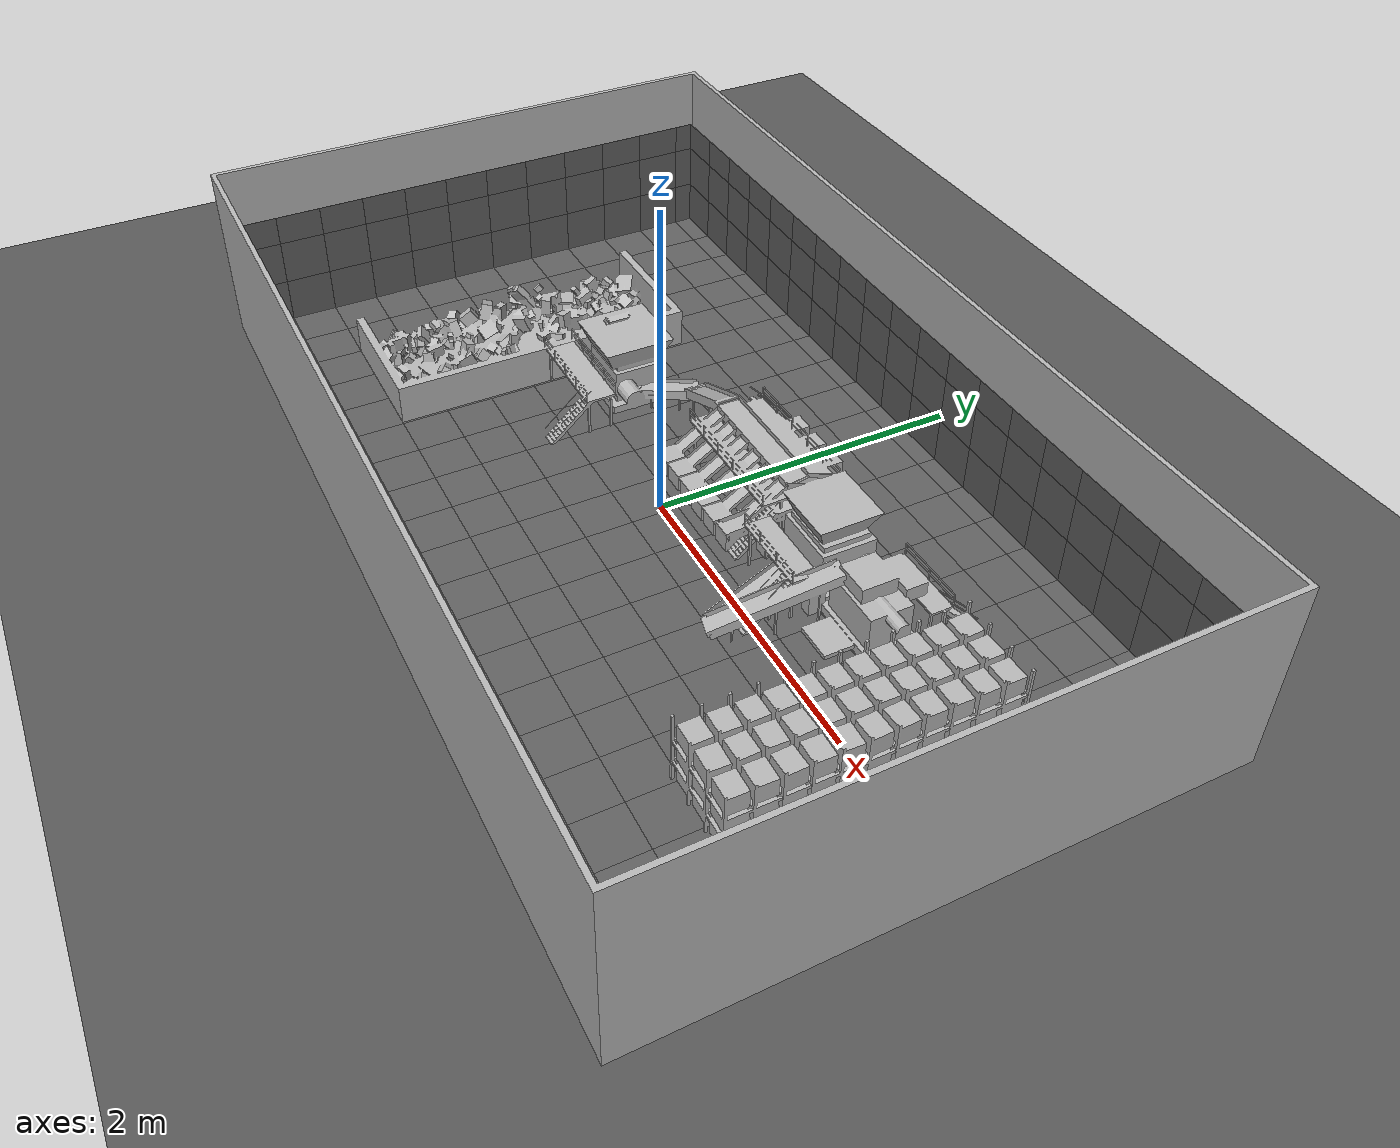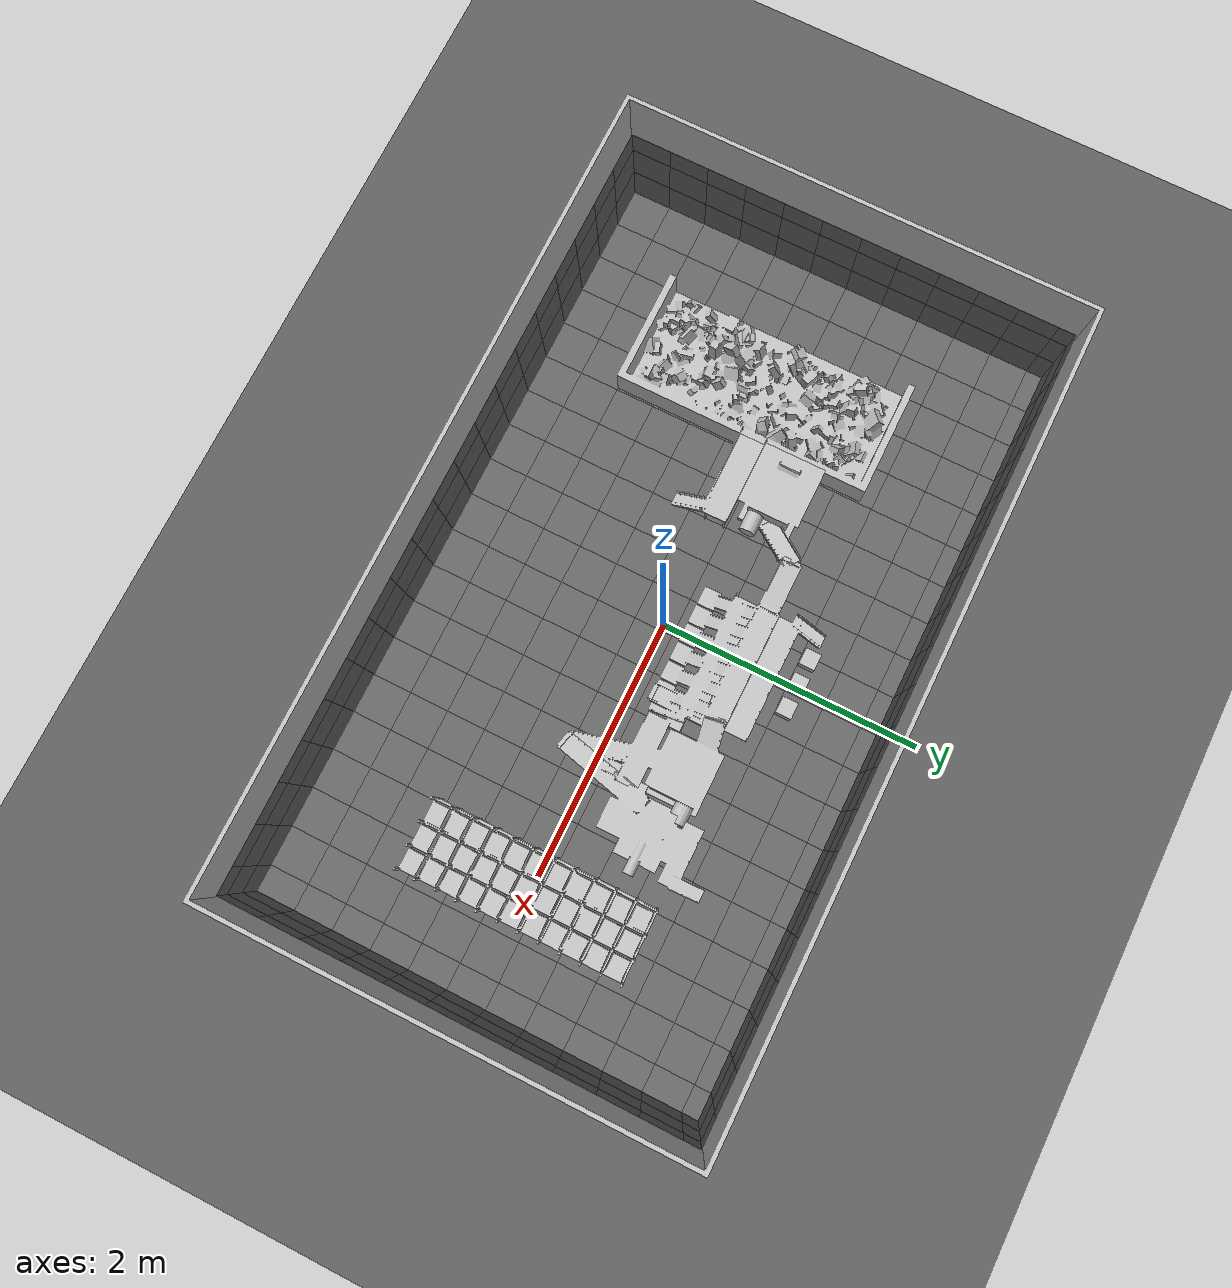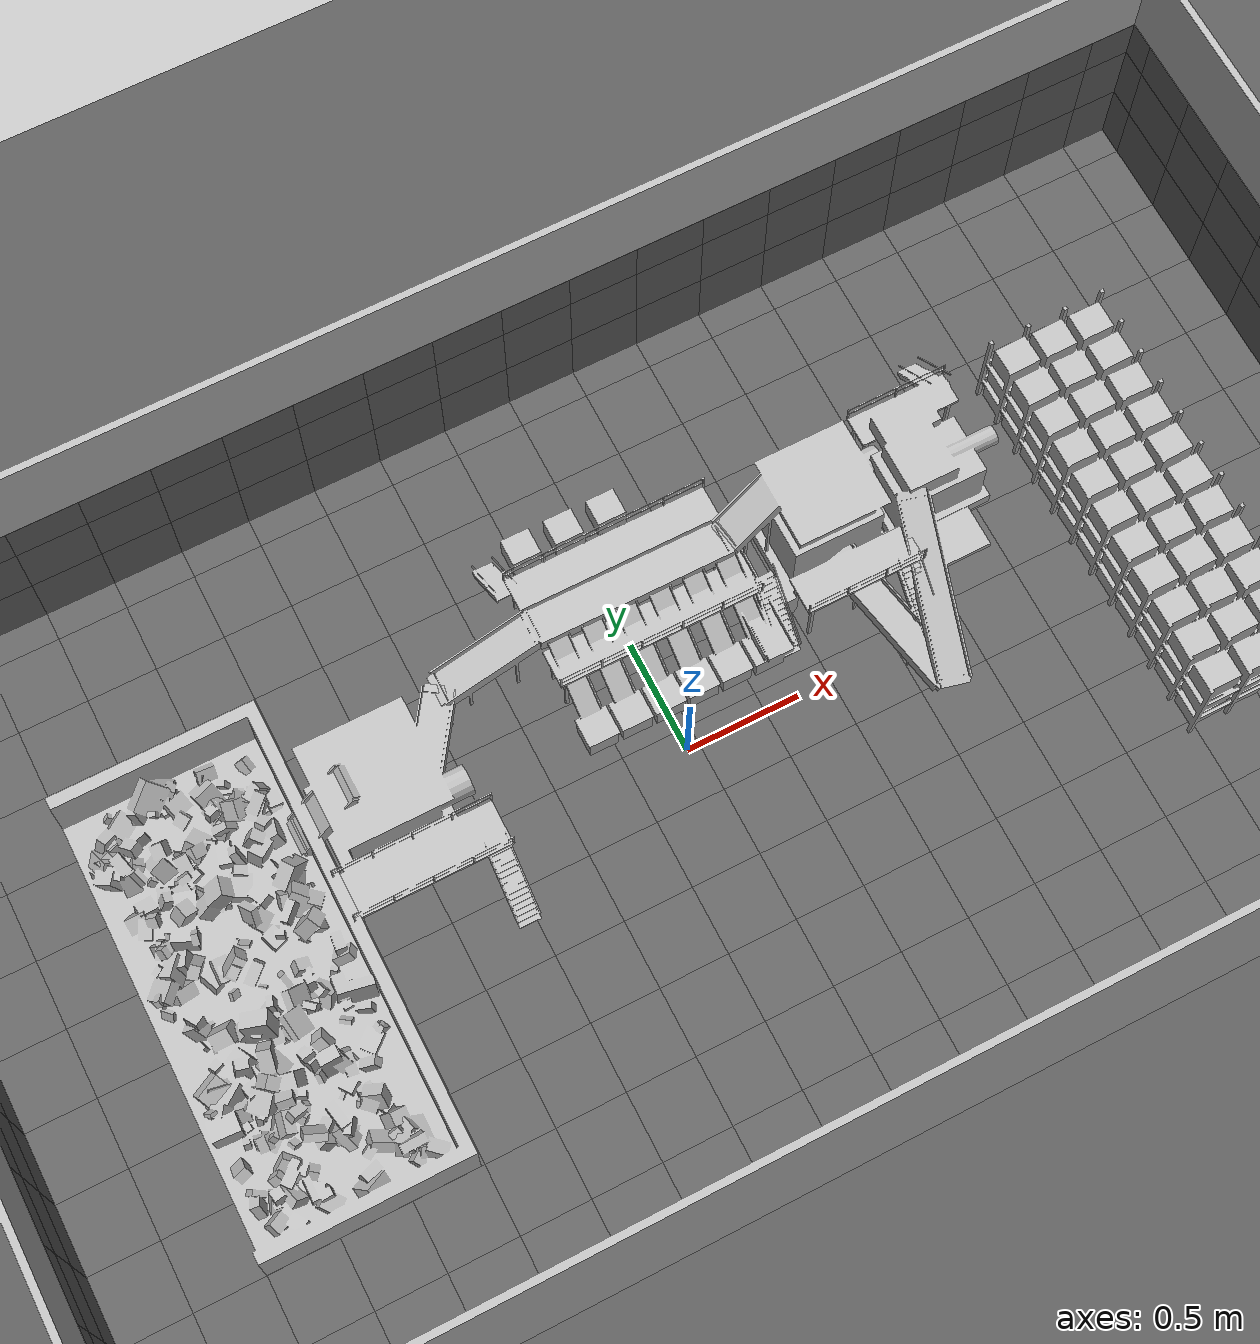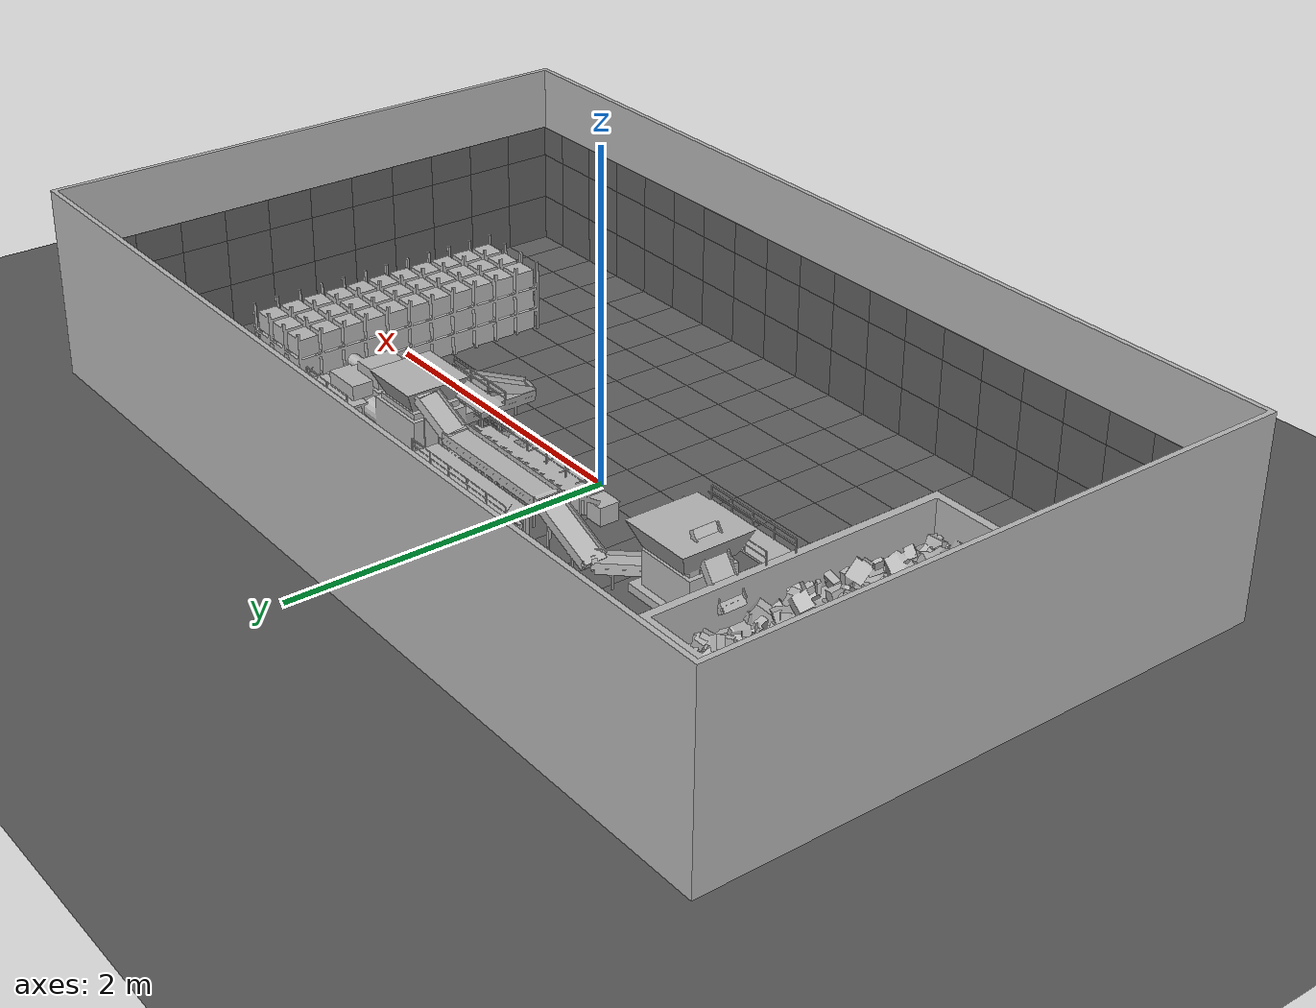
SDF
<?xml version='1.0' encoding='utf-8'?>
<sdf version="1.7">
  <world name="demo_facility_scaled">
    <plugin filename="ignition-gazebo-physics-system" name="ignition::gazebo::systems::Physics" />
    <plugin filename="ignition-gazebo-user-commands-system" name="ignition::gazebo::systems::UserCommands" />
    <plugin filename="ignition-gazebo-scene-broadcaster-system" name="ignition::gazebo::systems::SceneBroadcaster" />
    <plugin filename="ignition-gazebo-sensors-system" name="ignition::gazebo::systems::Sensors">
      <render_engine>ogre2</render_engine>
    </plugin>
    <plugin filename="ignition-gazebo-imu-system" name="ignition::gazebo::systems::Imu" />

    <physics name="1ms" type="ode">
      <max_step_size>0.001</max_step_size>
      <real_time_factor>1.0</real_time_factor>
      <real_time_update_rate>1000</real_time_update_rate>
      <ode>
        <solver><type>quick</type><iters>50</iters><sor>1.3</sor></solver>
        <constraints>
          <cfm>0.0</cfm><erp>0.2</erp>
          <contact_max_correcting_vel>100.0</contact_max_correcting_vel>
          <contact_surface_layer>0.001</contact_surface_layer>
        </constraints>
      </ode>
    </physics>
    <scene>
      <ambient>0.6 0.6 0.6 1</ambient>
      <background>0.72 0.78 0.84 1</background>
      <shadows>true</shadows>
    </scene>

    <light type="directional" name="sun">
      <cast_shadows>true</cast_shadows>
      <pose>0 0 6 0 0 0</pose>
      <diffuse>0.9 0.9 0.9 1</diffuse>
      <specular>0.2 0.2 0.2 1</specular>
      <direction>-0.4 0.3 -0.9</direction>
    </light>
    <light type="point" name="hall_fill_west">
      <pose>-1.485036 0 0.990024 0 0 0</pose>
      <diffuse>0.6 0.6 0.6 1</diffuse>
      <attenuation><range>4.0</range><linear>0.05</linear>
        <quadratic>0.02</quadratic></attenuation>
    </light>
    <light type="point" name="hall_fill_east">
      <pose>1.485036 0 0.990024 0 0 0</pose>
      <diffuse>0.6 0.6 0.6 1</diffuse>
      <attenuation><range>4.0</range><linear>0.05</linear>
        <quadratic>0.02</quadratic></attenuation>
    </light>

    <model name="ground_plane">
      <static>true</static>
      <link name="link">
        <collision name="collision">
          <geometry><plane><normal>0 0 1</normal>
            <size>12.0 10.0</size></plane></geometry>
        </collision>
        <visual name="visual">
          <geometry><plane><normal>0 0 1</normal>
            <size>12.0 10.0</size></plane></geometry>
          <material><ambient>0.3 0.3 0.3 1</ambient>
            <diffuse>0.35 0.35 0.35 1</diffuse></material>
        <plugin filename="ignition-gazebo-thermal-system" name="ignition::gazebo::systems::Thermal"><temperature>288.15</temperature></plugin>
        </visual>
      </link>
    </model>

    <model name="hall_shell">
      <static>true</static>
      <pose>0.000000 0.000000 0 0 0 0.000000</pose>
      <link name="link">
        <visual name="visual">
          <geometry><mesh><uri>model://hall_shell/meshes/hall_shell.obj</uri>
            <scale>0.0990099 0.0990099 0.0990099</scale></mesh></geometry>
        <plugin filename="ignition-gazebo-thermal-system" name="ignition::gazebo::systems::Thermal"><temperature>288.15</temperature></plugin>
        </visual>
        <collision name="collision">
          <geometry><mesh><uri>model://hall_shell/meshes/hall_shell.obj</uri>
            <scale>0.0990099 0.0990099 0.0990099</scale></mesh></geometry>
        </collision>
      </link>
    </model>
    <model name="bunker">
      <static>true</static>
      <pose>-0.145177 -0.038474 0 0 0 0.000000</pose>
      <link name="link">
        <visual name="visual">
          <geometry><mesh><uri>model://bunker/meshes/bunker.obj</uri>
            <scale>0.07474982 0.07474982 0.07474982</scale></mesh></geometry>
        <plugin filename="ignition-gazebo-thermal-system" name="ignition::gazebo::systems::Thermal"><temperature>323.65</temperature></plugin>
        </visual>
        <collision name="collision">
          <geometry><mesh><uri>model://bunker/meshes/bunker.obj</uri>
            <scale>0.07474982 0.07474982 0.07474982</scale></mesh></geometry>
        </collision>
      </link>
    </model>
    <model name="primary_shredder">
      <static>true</static>
      <pose>-0.145177 -0.038474 0 0 0 0.000000</pose>
      <link name="link">
        <visual name="visual">
          <geometry><mesh><uri>model://primary_shredder/meshes/primary_shredder.obj</uri>
            <scale>0.07474982 0.07474982 0.07474982</scale></mesh></geometry>
        <plugin filename="ignition-gazebo-thermal-system" name="ignition::gazebo::systems::Thermal"><temperature>326.25</temperature></plugin>
        </visual>
        <collision name="collision">
          <geometry><mesh><uri>model://primary_shredder/meshes/primary_shredder.obj</uri>
            <scale>0.07474982 0.07474982 0.07474982</scale></mesh></geometry>
        </collision>
      </link>
    </model>
    <model name="sorting_line">
      <static>true</static>
      <pose>-0.145177 -0.038474 0 0 0 0.000000</pose>
      <link name="link">
        <visual name="visual">
          <geometry><mesh><uri>model://sorting_line/meshes/sorting_line.obj</uri>
            <scale>0.07474982 0.07474982 0.07474982</scale></mesh></geometry>
        <plugin filename="ignition-gazebo-thermal-system" name="ignition::gazebo::systems::Thermal"><temperature>330.75</temperature></plugin>
        </visual>
        <collision name="collision">
          <geometry><mesh><uri>model://sorting_line/meshes/sorting_line.obj</uri>
            <scale>0.07474982 0.07474982 0.07474982</scale></mesh></geometry>
        </collision>
      </link>
    </model>
    <model name="secondary_processor">
      <static>true</static>
      <pose>-0.145177 -0.038474 0 0 0 0.000000</pose>
      <link name="link">
        <visual name="visual">
          <geometry><mesh><uri>model://secondary_processor/meshes/secondary_processor.obj</uri>
            <scale>0.07474982 0.07474982 0.07474982</scale></mesh></geometry>
        <plugin filename="ignition-gazebo-thermal-system" name="ignition::gazebo::systems::Thermal"><temperature>331.75</temperature></plugin>
        </visual>
        <collision name="collision">
          <geometry><mesh><uri>model://secondary_processor/meshes/secondary_processor.obj</uri>
            <scale>0.07474982 0.07474982 0.07474982</scale></mesh></geometry>
        </collision>
      </link>
    </model>
    <model name="baler">
      <static>true</static>
      <pose>-0.145177 -0.038474 0 0 0 0.000000</pose>
      <link name="link">
        <visual name="visual">
          <geometry><mesh><uri>model://baler/meshes/baler.obj</uri>
            <scale>0.07474982 0.07474982 0.07474982</scale></mesh></geometry>
        <plugin filename="ignition-gazebo-thermal-system" name="ignition::gazebo::systems::Thermal"><temperature>329.25</temperature></plugin>
        </visual>
        <collision name="collision">
          <geometry><mesh><uri>model://baler/meshes/baler.obj</uri>
            <scale>0.07474982 0.07474982 0.07474982</scale></mesh></geometry>
        </collision>
      </link>
    </model>
    <model name="bale_storage">
      <static>true</static>
      <pose>4.636175 0.471161 0 0 0 3.141592</pose>
      <link name="link">
        <visual name="visual">
          <geometry><mesh><uri>model://bale_storage/meshes/bale_storage.obj</uri>
            <scale>0.09919193 0.09919193 0.09919193</scale></mesh></geometry>
        <plugin filename="ignition-gazebo-thermal-system" name="ignition::gazebo::systems::Thermal"><temperature>327.35</temperature></plugin>
        </visual>
        <collision name="collision">
          <geometry><mesh><uri>model://bale_storage/meshes/bale_storage.obj</uri>
            <scale>0.09919193 0.09919193 0.09919193</scale></mesh></geometry>
        </collision>
      </link>
    </model>
  <model name="thermal_background">
    <static>true</static><link name="link">
      <visual name="floor_0">
        <pose>-2.800 -1.562 0.002 0 0 0</pose><geometry><box><size>0.300 0.300 0.001</size></box></geometry><material><ambient>0.35 0.35 0.35 1</ambient><diffuse>0.38 0.38 0.38 1</diffuse></material><cast_shadows>false</cast_shadows><plugin filename="ignition-gazebo-thermal-system" name="ignition::gazebo::systems::Thermal"><temperature>291.50</temperature></plugin>
        </visual>
      <visual name="floor_1">
        <pose>-2.800 -1.262 0.002 0 0 0</pose><geometry><box><size>0.300 0.300 0.001</size></box></geometry><material><ambient>0.35 0.35 0.35 1</ambient><diffuse>0.38 0.38 0.38 1</diffuse></material><cast_shadows>false</cast_shadows><plugin filename="ignition-gazebo-thermal-system" name="ignition::gazebo::systems::Thermal"><temperature>288.98</temperature></plugin>
        </visual>
      <visual name="floor_2">
        <pose>-2.800 -0.962 0.002 0 0 0</pose><geometry><box><size>0.300 0.300 0.001</size></box></geometry><material><ambient>0.35 0.35 0.35 1</ambient><diffuse>0.38 0.38 0.38 1</diffuse></material><cast_shadows>false</cast_shadows><plugin filename="ignition-gazebo-thermal-system" name="ignition::gazebo::systems::Thermal"><temperature>285.55</temperature></plugin>
        </visual>
      <visual name="floor_3">
        <pose>-2.800 -0.662 0.002 0 0 0</pose><geometry><box><size>0.300 0.300 0.001</size></box></geometry><material><ambient>0.35 0.35 0.35 1</ambient><diffuse>0.38 0.38 0.38 1</diffuse></material><cast_shadows>false</cast_shadows><plugin filename="ignition-gazebo-thermal-system" name="ignition::gazebo::systems::Thermal"><temperature>287.97</temperature></plugin>
        </visual>
      <visual name="floor_4">
        <pose>-2.800 -0.362 0.002 0 0 0</pose><geometry><box><size>0.300 0.300 0.001</size></box></geometry><material><ambient>0.35 0.35 0.35 1</ambient><diffuse>0.38 0.38 0.38 1</diffuse></material><cast_shadows>false</cast_shadows><plugin filename="ignition-gazebo-thermal-system" name="ignition::gazebo::systems::Thermal"><temperature>290.09</temperature></plugin>
        </visual>
      <visual name="floor_5">
        <pose>-2.800 -0.062 0.002 0 0 0</pose><geometry><box><size>0.300 0.300 0.001</size></box></geometry><material><ambient>0.35 0.35 0.35 1</ambient><diffuse>0.38 0.38 0.38 1</diffuse></material><cast_shadows>false</cast_shadows><plugin filename="ignition-gazebo-thermal-system" name="ignition::gazebo::systems::Thermal"><temperature>287.79</temperature></plugin>
        </visual>
      <visual name="floor_6">
        <pose>-2.800 0.238 0.002 0 0 0</pose><geometry><box><size>0.300 0.300 0.001</size></box></geometry><material><ambient>0.35 0.35 0.35 1</ambient><diffuse>0.38 0.38 0.38 1</diffuse></material><cast_shadows>false</cast_shadows><plugin filename="ignition-gazebo-thermal-system" name="ignition::gazebo::systems::Thermal"><temperature>286.73</temperature></plugin>
        </visual>
      <visual name="floor_7">
        <pose>-2.800 0.538 0.002 0 0 0</pose><geometry><box><size>0.300 0.300 0.001</size></box></geometry><material><ambient>0.35 0.35 0.35 1</ambient><diffuse>0.38 0.38 0.38 1</diffuse></material><cast_shadows>false</cast_shadows><plugin filename="ignition-gazebo-thermal-system" name="ignition::gazebo::systems::Thermal"><temperature>284.93</temperature></plugin>
        </visual>
      <visual name="floor_8">
        <pose>-2.800 0.838 0.002 0 0 0</pose><geometry><box><size>0.300 0.300 0.001</size></box></geometry><material><ambient>0.35 0.35 0.35 1</ambient><diffuse>0.38 0.38 0.38 1</diffuse></material><cast_shadows>false</cast_shadows><plugin filename="ignition-gazebo-thermal-system" name="ignition::gazebo::systems::Thermal"><temperature>285.17</temperature></plugin>
        </visual>
      <visual name="floor_9">
        <pose>-2.800 1.138 0.002 0 0 0</pose><geometry><box><size>0.300 0.300 0.001</size></box></geometry><material><ambient>0.35 0.35 0.35 1</ambient><diffuse>0.38 0.38 0.38 1</diffuse></material><cast_shadows>false</cast_shadows><plugin filename="ignition-gazebo-thermal-system" name="ignition::gazebo::systems::Thermal"><temperature>286.11</temperature></plugin>
        </visual>
      <visual name="floor_10">
        <pose>-2.800 1.438 0.002 0 0 0</pose><geometry><box><size>0.300 0.300 0.001</size></box></geometry><material><ambient>0.35 0.35 0.35 1</ambient><diffuse>0.38 0.38 0.38 1</diffuse></material><cast_shadows>false</cast_shadows><plugin filename="ignition-gazebo-thermal-system" name="ignition::gazebo::systems::Thermal"><temperature>290.24</temperature></plugin>
        </visual>
      <visual name="floor_11">
        <pose>-2.800 1.650 0.002 0 0 0</pose><geometry><box><size>0.300 0.125 0.001</size></box></geometry><material><ambient>0.35 0.35 0.35 1</ambient><diffuse>0.38 0.38 0.38 1</diffuse></material><cast_shadows>false</cast_shadows><plugin filename="ignition-gazebo-thermal-system" name="ignition::gazebo::systems::Thermal"><temperature>291.02</temperature></plugin>
        </visual>
      <visual name="floor_12">
        <pose>-2.500 -1.562 0.002 0 0 0</pose><geometry><box><size>0.300 0.300 0.001</size></box></geometry><material><ambient>0.35 0.35 0.35 1</ambient><diffuse>0.38 0.38 0.38 1</diffuse></material><cast_shadows>false</cast_shadows><plugin filename="ignition-gazebo-thermal-system" name="ignition::gazebo::systems::Thermal"><temperature>290.18</temperature></plugin>
        </visual>
      <visual name="floor_13">
        <pose>-2.500 -1.262 0.002 0 0 0</pose><geometry><box><size>0.300 0.300 0.001</size></box></geometry><material><ambient>0.35 0.35 0.35 1</ambient><diffuse>0.38 0.38 0.38 1</diffuse></material><cast_shadows>false</cast_shadows><plugin filename="ignition-gazebo-thermal-system" name="ignition::gazebo::systems::Thermal"><temperature>284.94</temperature></plugin>
        </visual>
      <visual name="floor_14">
        <pose>-2.500 -0.962 0.002 0 0 0</pose><geometry><box><size>0.300 0.300 0.001</size></box></geometry><material><ambient>0.35 0.35 0.35 1</ambient><diffuse>0.38 0.38 0.38 1</diffuse></material><cast_shadows>false</cast_shadows><plugin filename="ignition-gazebo-thermal-system" name="ignition::gazebo::systems::Thermal"><temperature>289.14</temperature></plugin>
        </visual>
      <visual name="floor_15">
        <pose>-2.500 -0.662 0.002 0 0 0</pose><geometry><box><size>0.300 0.300 0.001</size></box></geometry><material><ambient>0.35 0.35 0.35 1</ambient><diffuse>0.38 0.38 0.38 1</diffuse></material><cast_shadows>false</cast_shadows><plugin filename="ignition-gazebo-thermal-system" name="ignition::gazebo::systems::Thermal"><temperature>290.39</temperature></plugin>
        </visual>
      <visual name="floor_16">
        <pose>-2.500 -0.362 0.002 0 0 0</pose><geometry><box><size>0.300 0.300 0.001</size></box></geometry><material><ambient>0.35 0.35 0.35 1</ambient><diffuse>0.38 0.38 0.38 1</diffuse></material><cast_shadows>false</cast_shadows><plugin filename="ignition-gazebo-thermal-system" name="ignition::gazebo::systems::Thermal"><temperature>283.79</temperature></plugin>
        </visual>
      <visual name="floor_17">
        <pose>-2.500 -0.062 0.002 0 0 0</pose><geometry><box><size>0.300 0.300 0.001</size></box></geometry><material><ambient>0.35 0.35 0.35 1</ambient><diffuse>0.38 0.38 0.38 1</diffuse></material><cast_shadows>false</cast_shadows><plugin filename="ignition-gazebo-thermal-system" name="ignition::gazebo::systems::Thermal"><temperature>289.33</temperature></plugin>
        </visual>
      <visual name="floor_18">
        <pose>-2.500 0.238 0.002 0 0 0</pose><geometry><box><size>0.300 0.300 0.001</size></box></geometry><material><ambient>0.35 0.35 0.35 1</ambient><diffuse>0.38 0.38 0.38 1</diffuse></material><cast_shadows>false</cast_shadows><plugin filename="ignition-gazebo-thermal-system" name="ignition::gazebo::systems::Thermal"><temperature>286.56</temperature></plugin>
        </visual>
      <visual name="floor_19">
        <pose>-2.500 0.538 0.002 0 0 0</pose><geometry><box><size>0.300 0.300 0.001</size></box></geometry><material><ambient>0.35 0.35 0.35 1</ambient><diffuse>0.38 0.38 0.38 1</diffuse></material><cast_shadows>false</cast_shadows><plugin filename="ignition-gazebo-thermal-system" name="ignition::gazebo::systems::Thermal"><temperature>287.77</temperature></plugin>
        </visual>
      <visual name="floor_20">
        <pose>-2.500 0.838 0.002 0 0 0</pose><geometry><box><size>0.300 0.300 0.001</size></box></geometry><material><ambient>0.35 0.35 0.35 1</ambient><diffuse>0.38 0.38 0.38 1</diffuse></material><cast_shadows>false</cast_shadows><plugin filename="ignition-gazebo-thermal-system" name="ignition::gazebo::systems::Thermal"><temperature>289.09</temperature></plugin>
        </visual>
      <visual name="floor_21">
        <pose>-2.500 1.138 0.002 0 0 0</pose><geometry><box><size>0.300 0.300 0.001</size></box></geometry><material><ambient>0.35 0.35 0.35 1</ambient><diffuse>0.38 0.38 0.38 1</diffuse></material><cast_shadows>false</cast_shadows><plugin filename="ignition-gazebo-thermal-system" name="ignition::gazebo::systems::Thermal"><temperature>289.48</temperature></plugin>
        </visual>
      <visual name="floor_22">
        <pose>-2.500 1.438 0.002 0 0 0</pose><geometry><box><size>0.300 0.300 0.001</size></box></geometry><material><ambient>0.35 0.35 0.35 1</ambient><diffuse>0.38 0.38 0.38 1</diffuse></material><cast_shadows>false</cast_shadows><plugin filename="ignition-gazebo-thermal-system" name="ignition::gazebo::systems::Thermal"><temperature>286.46</temperature></plugin>
        </visual>
      <visual name="floor_23">
        <pose>-2.500 1.650 0.002 0 0 0</pose><geometry><box><size>0.300 0.125 0.001</size></box></geometry><material><ambient>0.35 0.35 0.35 1</ambient><diffuse>0.38 0.38 0.38 1</diffuse></material><cast_shadows>false</cast_shadows><plugin filename="ignition-gazebo-thermal-system" name="ignition::gazebo::systems::Thermal"><temperature>285.97</temperature></plugin>
        </visual>
      <visual name="floor_24">
        <pose>-2.200 -1.562 0.002 0 0 0</pose><geometry><box><size>0.300 0.300 0.001</size></box></geometry><material><ambient>0.35 0.35 0.35 1</ambient><diffuse>0.38 0.38 0.38 1</diffuse></material><cast_shadows>false</cast_shadows><plugin filename="ignition-gazebo-thermal-system" name="ignition::gazebo::systems::Thermal"><temperature>284.28</temperature></plugin>
        </visual>
      <visual name="floor_25">
        <pose>-2.200 -1.262 0.002 0 0 0</pose><geometry><box><size>0.300 0.300 0.001</size></box></geometry><material><ambient>0.35 0.35 0.35 1</ambient><diffuse>0.38 0.38 0.38 1</diffuse></material><cast_shadows>false</cast_shadows><plugin filename="ignition-gazebo-thermal-system" name="ignition::gazebo::systems::Thermal"><temperature>283.30</temperature></plugin>
        </visual>
      <visual name="floor_26">
        <pose>-2.200 -0.962 0.002 0 0 0</pose><geometry><box><size>0.300 0.300 0.001</size></box></geometry><material><ambient>0.35 0.35 0.35 1</ambient><diffuse>0.38 0.38 0.38 1</diffuse></material><cast_shadows>false</cast_shadows><plugin filename="ignition-gazebo-thermal-system" name="ignition::gazebo::systems::Thermal"><temperature>289.85</temperature></plugin>
        </visual>
      <visual name="floor_27">
        <pose>-2.200 -0.662 0.002 0 0 0</pose><geometry><box><size>0.300 0.300 0.001</size></box></geometry><material><ambient>0.35 0.35 0.35 1</ambient><diffuse>0.38 0.38 0.38 1</diffuse></material><cast_shadows>false</cast_shadows><plugin filename="ignition-gazebo-thermal-system" name="ignition::gazebo::systems::Thermal"><temperature>288.94</temperature></plugin>
        </visual>
      <visual name="floor_28">
        <pose>-2.200 -0.362 0.002 0 0 0</pose><geometry><box><size>0.300 0.300 0.001</size></box></geometry><material><ambient>0.35 0.35 0.35 1</ambient><diffuse>0.38 0.38 0.38 1</diffuse></material><cast_shadows>false</cast_shadows><plugin filename="ignition-gazebo-thermal-system" name="ignition::gazebo::systems::Thermal"><temperature>292.58</temperature></plugin>
        </visual>
      <visual name="floor_29">
        <pose>-2.200 -0.062 0.002 0 0 0</pose><geometry><box><size>0.300 0.300 0.001</size></box></geometry><material><ambient>0.35 0.35 0.35 1</ambient><diffuse>0.38 0.38 0.38 1</diffuse></material><cast_shadows>false</cast_shadows><plugin filename="ignition-gazebo-thermal-system" name="ignition::gazebo::systems::Thermal"><temperature>293.04</temperature></plugin>
        </visual>
      <visual name="floor_30">
        <pose>-2.200 0.238 0.002 0 0 0</pose><geometry><box><size>0.300 0.300 0.001</size></box></geometry><material><ambient>0.35 0.35 0.35 1</ambient><diffuse>0.38 0.38 0.38 1</diffuse></material><cast_shadows>false</cast_shadows><plugin filename="ignition-gazebo-thermal-system" name="ignition::gazebo::systems::Thermal"><temperature>284.99</temperature></plugin>
        </visual>
      <visual name="floor_31">
        <pose>-2.200 0.538 0.002 0 0 0</pose><geometry><box><size>0.300 0.300 0.001</size></box></geometry><material><ambient>0.35 0.35 0.35 1</ambient><diffuse>0.38 0.38 0.38 1</diffuse></material><cast_shadows>false</cast_shadows><plugin filename="ignition-gazebo-thermal-system" name="ignition::gazebo::systems::Thermal"><temperature>291.96</temperature></plugin>
        </visual>
      <visual name="floor_32">
        <pose>-2.200 0.838 0.002 0 0 0</pose><geometry><box><size>0.300 0.300 0.001</size></box></geometry><material><ambient>0.35 0.35 0.35 1</ambient><diffuse>0.38 0.38 0.38 1</diffuse></material><cast_shadows>false</cast_shadows><plugin filename="ignition-gazebo-thermal-system" name="ignition::gazebo::systems::Thermal"><temperature>287.76</temperature></plugin>
        </visual>
      <visual name="floor_33">
        <pose>-2.200 1.138 0.002 0 0 0</pose><geometry><box><size>0.300 0.300 0.001</size></box></geometry><material><ambient>0.35 0.35 0.35 1</ambient><diffuse>0.38 0.38 0.38 1</diffuse></material><cast_shadows>false</cast_shadows><plugin filename="ignition-gazebo-thermal-system" name="ignition::gazebo::systems::Thermal"><temperature>283.88</temperature></plugin>
        </visual>
      <visual name="floor_34">
        <pose>-2.200 1.438 0.002 0 0 0</pose><geometry><box><size>0.300 0.300 0.001</size></box></geometry><material><ambient>0.35 0.35 0.35 1</ambient><diffuse>0.38 0.38 0.38 1</diffuse></material><cast_shadows>false</cast_shadows><plugin filename="ignition-gazebo-thermal-system" name="ignition::gazebo::systems::Thermal"><temperature>287.68</temperature></plugin>
        </visual>
      <visual name="floor_35">
        <pose>-2.200 1.650 0.002 0 0 0</pose><geometry><box><size>0.300 0.125 0.001</size></box></geometry><material><ambient>0.35 0.35 0.35 1</ambient><diffuse>0.38 0.38 0.38 1</diffuse></material><cast_shadows>false</cast_shadows><plugin filename="ignition-gazebo-thermal-system" name="ignition::gazebo::systems::Thermal"><temperature>286.40</temperature></plugin>
        </visual>
      <visual name="floor_36">
        <pose>-1.900 -1.562 0.002 0 0 0</pose><geometry><box><size>0.300 0.300 0.001</size></box></geometry><material><ambient>0.35 0.35 0.35 1</ambient><diffuse>0.38 0.38 0.38 1</diffuse></material><cast_shadows>false</cast_shadows><plugin filename="ignition-gazebo-thermal-system" name="ignition::gazebo::systems::Thermal"><temperature>285.03</temperature></plugin>
        </visual>
      <visual name="floor_37">
        <pose>-1.900 -1.262 0.002 0 0 0</pose><geometry><box><size>0.300 0.300 0.001</size></box></geometry><material><ambient>0.35 0.35 0.35 1</ambient><diffuse>0.38 0.38 0.38 1</diffuse></material><cast_shadows>false</cast_shadows><plugin filename="ignition-gazebo-thermal-system" name="ignition::gazebo::systems::Thermal"><temperature>291.52</temperature></plugin>
        </visual>
      <visual name="floor_38">
        <pose>-1.900 -0.962 0.002 0 0 0</pose><geometry><box><size>0.300 0.300 0.001</size></box></geometry><material><ambient>0.35 0.35 0.35 1</ambient><diffuse>0.38 0.38 0.38 1</diffuse></material><cast_shadows>false</cast_shadows><plugin filename="ignition-gazebo-thermal-system" name="ignition::gazebo::systems::Thermal"><temperature>292.11</temperature></plugin>
        </visual>
      <visual name="floor_39">
        <pose>-1.900 -0.662 0.002 0 0 0</pose><geometry><box><size>0.300 0.300 0.001</size></box></geometry><material><ambient>0.35 0.35 0.35 1</ambient><diffuse>0.38 0.38 0.38 1</diffuse></material><cast_shadows>false</cast_shadows><plugin filename="ignition-gazebo-thermal-system" name="ignition::gazebo::systems::Thermal"><temperature>286.90</temperature></plugin>
        </visual>
      <visual name="floor_40">
        <pose>-1.900 -0.362 0.002 0 0 0</pose><geometry><box><size>0.300 0.300 0.001</size></box></geometry><material><ambient>0.35 0.35 0.35 1</ambient><diffuse>0.38 0.38 0.38 1</diffuse></material><cast_shadows>false</cast_shadows><plugin filename="ignition-gazebo-thermal-system" name="ignition::gazebo::systems::Thermal"><temperature>284.01</temperature></plugin>
        </visual>
      <visual name="floor_41">
        <pose>-1.900 -0.062 0.002 0 0 0</pose><geometry><box><size>0.300 0.300 0.001</size></box></geometry><material><ambient>0.35 0.35 0.35 1</ambient><diffuse>0.38 0.38 0.38 1</diffuse></material><cast_shadows>false</cast_shadows><plugin filename="ignition-gazebo-thermal-system" name="ignition::gazebo::systems::Thermal"><temperature>285.83</temperature></plugin>
        </visual>
      <visual name="floor_42">
        <pose>-1.900 0.238 0.002 0 0 0</pose><geometry><box><size>0.300 0.300 0.001</size></box></geometry><material><ambient>0.35 0.35 0.35 1</ambient><diffuse>0.38 0.38 0.38 1</diffuse></material><cast_shadows>false</cast_shadows><plugin filename="ignition-gazebo-thermal-system" name="ignition::gazebo::systems::Thermal"><temperature>288.40</temperature></plugin>
        </visual>
      <visual name="floor_43">
        <pose>-1.900 0.538 0.002 0 0 0</pose><geometry><box><size>0.300 0.300 0.001</size></box></geometry><material><ambient>0.35 0.35 0.35 1</ambient><diffuse>0.38 0.38 0.38 1</diffuse></material><cast_shadows>false</cast_shadows><plugin filename="ignition-gazebo-thermal-system" name="ignition::gazebo::systems::Thermal"><temperature>284.16</temperature></plugin>
        </visual>
      <visual name="floor_44">
        <pose>-1.900 0.838 0.002 0 0 0</pose><geometry><box><size>0.300 0.300 0.001</size></box></geometry><material><ambient>0.35 0.35 0.35 1</ambient><diffuse>0.38 0.38 0.38 1</diffuse></material><cast_shadows>false</cast_shadows><plugin filename="ignition-gazebo-thermal-system" name="ignition::gazebo::systems::Thermal"><temperature>286.93</temperature></plugin>
        </visual>
      <visual name="floor_45">
        <pose>-1.900 1.138 0.002 0 0 0</pose><geometry><box><size>0.300 0.300 0.001</size></box></geometry><material><ambient>0.35 0.35 0.35 1</ambient><diffuse>0.38 0.38 0.38 1</diffuse></material><cast_shadows>false</cast_shadows><plugin filename="ignition-gazebo-thermal-system" name="ignition::gazebo::systems::Thermal"><temperature>285.03</temperature></plugin>
        </visual>
      <visual name="floor_46">
        <pose>-1.900 1.438 0.002 0 0 0</pose><geometry><box><size>0.300 0.300 0.001</size></box></geometry><material><ambient>0.35 0.35 0.35 1</ambient><diffuse>0.38 0.38 0.38 1</diffuse></material><cast_shadows>false</cast_shadows><plugin filename="ignition-gazebo-thermal-system" name="ignition::gazebo::systems::Thermal"><temperature>286.75</temperature></plugin>
        </visual>
      <visual name="floor_47">
        <pose>-1.900 1.650 0.002 0 0 0</pose><geometry><box><size>0.300 0.125 0.001</size></box></geometry><material><ambient>0.35 0.35 0.35 1</ambient><diffuse>0.38 0.38 0.38 1</diffuse></material><cast_shadows>false</cast_shadows><plugin filename="ignition-gazebo-thermal-system" name="ignition::gazebo::systems::Thermal"><temperature>287.32</temperature></plugin>
        </visual>
      <visual name="floor_48">
        <pose>-1.600 -1.562 0.002 0 0 0</pose><geometry><box><size>0.300 0.300 0.001</size></box></geometry><material><ambient>0.35 0.35 0.35 1</ambient><diffuse>0.38 0.38 0.38 1</diffuse></material><cast_shadows>false</cast_shadows><plugin filename="ignition-gazebo-thermal-system" name="ignition::gazebo::systems::Thermal"><temperature>289.48</temperature></plugin>
        </visual>
      <visual name="floor_49">
        <pose>-1.600 -1.262 0.002 0 0 0</pose><geometry><box><size>0.300 0.300 0.001</size></box></geometry><material><ambient>0.35 0.35 0.35 1</ambient><diffuse>0.38 0.38 0.38 1</diffuse></material><cast_shadows>false</cast_shadows><plugin filename="ignition-gazebo-thermal-system" name="ignition::gazebo::systems::Thermal"><temperature>292.83</temperature></plugin>
        </visual>
      <visual name="floor_50">
        <pose>-1.600 -0.962 0.002 0 0 0</pose><geometry><box><size>0.300 0.300 0.001</size></box></geometry><material><ambient>0.35 0.35 0.35 1</ambient><diffuse>0.38 0.38 0.38 1</diffuse></material><cast_shadows>false</cast_shadows><plugin filename="ignition-gazebo-thermal-system" name="ignition::gazebo::systems::Thermal"><temperature>284.89</temperature></plugin>
        </visual>
      <visual name="floor_51">
        <pose>-1.600 -0.662 0.002 0 0 0</pose><geometry><box><size>0.300 0.300 0.001</size></box></geometry><material><ambient>0.35 0.35 0.35 1</ambient><diffuse>0.38 0.38 0.38 1</diffuse></material><cast_shadows>false</cast_shadows><plugin filename="ignition-gazebo-thermal-system" name="ignition::gazebo::systems::Thermal"><temperature>287.60</temperature></plugin>
        </visual>
      <visual name="floor_52">
        <pose>-1.600 -0.362 0.002 0 0 0</pose><geometry><box><size>0.300 0.300 0.001</size></box></geometry><material><ambient>0.35 0.35 0.35 1</ambient><diffuse>0.38 0.38 0.38 1</diffuse></material><cast_shadows>false</cast_shadows><plugin filename="ignition-gazebo-thermal-system" name="ignition::gazebo::systems::Thermal"><temperature>286.80</temperature></plugin>
        </visual>
      <visual name="floor_53">
        <pose>-1.600 -0.062 0.002 0 0 0</pose><geometry><box><size>0.300 0.300 0.001</size></box></geometry><material><ambient>0.35 0.35 0.35 1</ambient><diffuse>0.38 0.38 0.38 1</diffuse></material><cast_shadows>false</cast_shadows><plugin filename="ignition-gazebo-thermal-system" name="ignition::gazebo::systems::Thermal"><temperature>288.08</temperature></plugin>
        </visual>
      <visual name="floor_54">
        <pose>-1.600 0.238 0.002 0 0 0</pose><geometry><box><size>0.300 0.300 0.001</size></box></geometry><material><ambient>0.35 0.35 0.35 1</ambient><diffuse>0.38 0.38 0.38 1</diffuse></material><cast_shadows>false</cast_shadows><plugin filename="ignition-gazebo-thermal-system" name="ignition::gazebo::systems::Thermal"><temperature>284.16</temperature></plugin>
        </visual>
      <visual name="floor_55">
        <pose>-1.600 0.538 0.002 0 0 0</pose><geometry><box><size>0.300 0.300 0.001</size></box></geometry><material><ambient>0.35 0.35 0.35 1</ambient><diffuse>0.38 0.38 0.38 1</diffuse></material><cast_shadows>false</cast_shadows><plugin filename="ignition-gazebo-thermal-system" name="ignition::gazebo::systems::Thermal"><temperature>289.22</temperature></plugin>
        </visual>
      <visual name="floor_56">
        <pose>-1.600 0.838 0.002 0 0 0</pose><geometry><box><size>0.300 0.300 0.001</size></box></geometry><material><ambient>0.35 0.35 0.35 1</ambient><diffuse>0.38 0.38 0.38 1</diffuse></material><cast_shadows>false</cast_shadows><plugin filename="ignition-gazebo-thermal-system" name="ignition::gazebo::systems::Thermal"><temperature>286.65</temperature></plugin>
        </visual>
      <visual name="floor_57">
        <pose>-1.600 1.138 0.002 0 0 0</pose><geometry><box><size>0.300 0.300 0.001</size></box></geometry><material><ambient>0.35 0.35 0.35 1</ambient><diffuse>0.38 0.38 0.38 1</diffuse></material><cast_shadows>false</cast_shadows><plugin filename="ignition-gazebo-thermal-system" name="ignition::gazebo::systems::Thermal"><temperature>284.95</temperature></plugin>
        </visual>
      <visual name="floor_58">
        <pose>-1.600 1.438 0.002 0 0 0</pose><geometry><box><size>0.300 0.300 0.001</size></box></geometry><material><ambient>0.35 0.35 0.35 1</ambient><diffuse>0.38 0.38 0.38 1</diffuse></material><cast_shadows>false</cast_shadows><plugin filename="ignition-gazebo-thermal-system" name="ignition::gazebo::systems::Thermal"><temperature>287.87</temperature></plugin>
        </visual>
      <visual name="floor_59">
        <pose>-1.600 1.650 0.002 0 0 0</pose><geometry><box><size>0.300 0.125 0.001</size></box></geometry><material><ambient>0.35 0.35 0.35 1</ambient><diffuse>0.38 0.38 0.38 1</diffuse></material><cast_shadows>false</cast_shadows><plugin filename="ignition-gazebo-thermal-system" name="ignition::gazebo::systems::Thermal"><temperature>291.00</temperature></plugin>
        </visual>
      <visual name="floor_60">
        <pose>-1.300 -1.562 0.002 0 0 0</pose><geometry><box><size>0.300 0.300 0.001</size></box></geometry><material><ambient>0.35 0.35 0.35 1</ambient><diffuse>0.38 0.38 0.38 1</diffuse></material><cast_shadows>false</cast_shadows><plugin filename="ignition-gazebo-thermal-system" name="ignition::gazebo::systems::Thermal"><temperature>289.30</temperature></plugin>
        </visual>
      <visual name="floor_61">
        <pose>-1.300 -1.262 0.002 0 0 0</pose><geometry><box><size>0.300 0.300 0.001</size></box></geometry><material><ambient>0.35 0.35 0.35 1</ambient><diffuse>0.38 0.38 0.38 1</diffuse></material><cast_shadows>false</cast_shadows><plugin filename="ignition-gazebo-thermal-system" name="ignition::gazebo::systems::Thermal"><temperature>292.36</temperature></plugin>
        </visual>
      <visual name="floor_62">
        <pose>-1.300 -0.962 0.002 0 0 0</pose><geometry><box><size>0.300 0.300 0.001</size></box></geometry><material><ambient>0.35 0.35 0.35 1</ambient><diffuse>0.38 0.38 0.38 1</diffuse></material><cast_shadows>false</cast_shadows><plugin filename="ignition-gazebo-thermal-system" name="ignition::gazebo::systems::Thermal"><temperature>284.85</temperature></plugin>
        </visual>
      <visual name="floor_63">
        <pose>-1.300 -0.662 0.002 0 0 0</pose><geometry><box><size>0.300 0.300 0.001</size></box></geometry><material><ambient>0.35 0.35 0.35 1</ambient><diffuse>0.38 0.38 0.38 1</diffuse></material><cast_shadows>false</cast_shadows><plugin filename="ignition-gazebo-thermal-system" name="ignition::gazebo::systems::Thermal"><temperature>286.19</temperature></plugin>
        </visual>
      <visual name="floor_64">
        <pose>-1.300 -0.362 0.002 0 0 0</pose><geometry><box><size>0.300 0.300 0.001</size></box></geometry><material><ambient>0.35 0.35 0.35 1</ambient><diffuse>0.38 0.38 0.38 1</diffuse></material><cast_shadows>false</cast_shadows><plugin filename="ignition-gazebo-thermal-system" name="ignition::gazebo::systems::Thermal"><temperature>287.81</temperature></plugin>
        </visual>
      <visual name="floor_65">
        <pose>-1.300 -0.062 0.002 0 0 0</pose><geometry><box><size>0.300 0.300 0.001</size></box></geometry><material><ambient>0.35 0.35 0.35 1</ambient><diffuse>0.38 0.38 0.38 1</diffuse></material><cast_shadows>false</cast_shadows><plugin filename="ignition-gazebo-thermal-system" name="ignition::gazebo::systems::Thermal"><temperature>291.32</temperature></plugin>
        </visual>
      <visual name="floor_66">
        <pose>-1.300 0.238 0.002 0 0 0</pose><geometry><box><size>0.300 0.300 0.001</size></box></geometry><material><ambient>0.35 0.35 0.35 1</ambient><diffuse>0.38 0.38 0.38 1</diffuse></material><cast_shadows>false</cast_shadows><plugin filename="ignition-gazebo-thermal-system" name="ignition::gazebo::systems::Thermal"><temperature>290.81</temperature></plugin>
        </visual>
      <visual name="floor_67">
        <pose>-1.300 0.538 0.002 0 0 0</pose><geometry><box><size>0.300 0.300 0.001</size></box></geometry><material><ambient>0.35 0.35 0.35 1</ambient><diffuse>0.38 0.38 0.38 1</diffuse></material><cast_shadows>false</cast_shadows><plugin filename="ignition-gazebo-thermal-system" name="ignition::gazebo::systems::Thermal"><temperature>292.36</temperature></plugin>
        </visual>
      <visual name="floor_68">
        <pose>-1.300 0.838 0.002 0 0 0</pose><geometry><box><size>0.300 0.300 0.001</size></box></geometry><material><ambient>0.35 0.35 0.35 1</ambient><diffuse>0.38 0.38 0.38 1</diffuse></material><cast_shadows>false</cast_shadows><plugin filename="ignition-gazebo-thermal-system" name="ignition::gazebo::systems::Thermal"><temperature>285.79</temperature></plugin>
        </visual>
      <visual name="floor_69">
        <pose>-1.300 1.138 0.002 0 0 0</pose><geometry><box><size>0.300 0.300 0.001</size></box></geometry><material><ambient>0.35 0.35 0.35 1</ambient><diffuse>0.38 0.38 0.38 1</diffuse></material><cast_shadows>false</cast_shadows><plugin filename="ignition-gazebo-thermal-system" name="ignition::gazebo::systems::Thermal"><temperature>291.62</temperature></plugin>
        </visual>
      <visual name="floor_70">
        <pose>-1.300 1.438 0.002 0 0 0</pose><geometry><box><size>0.300 0.300 0.001</size></box></geometry><material><ambient>0.35 0.35 0.35 1</ambient><diffuse>0.38 0.38 0.38 1</diffuse></material><cast_shadows>false</cast_shadows><plugin filename="ignition-gazebo-thermal-system" name="ignition::gazebo::systems::Thermal"><temperature>285.42</temperature></plugin>
        </visual>
      <visual name="floor_71">
        <pose>-1.300 1.650 0.002 0 0 0</pose><geometry><box><size>0.300 0.125 0.001</size></box></geometry><material><ambient>0.35 0.35 0.35 1</ambient><diffuse>0.38 0.38 0.38 1</diffuse></material><cast_shadows>false</cast_shadows><plugin filename="ignition-gazebo-thermal-system" name="ignition::gazebo::systems::Thermal"><temperature>291.16</temperature></plugin>
        </visual>
      <visual name="floor_72">
        <pose>-1.000 -1.562 0.002 0 0 0</pose><geometry><box><size>0.300 0.300 0.001</size></box></geometry><material><ambient>0.35 0.35 0.35 1</ambient><diffuse>0.38 0.38 0.38 1</diffuse></material><cast_shadows>false</cast_shadows><plugin filename="ignition-gazebo-thermal-system" name="ignition::gazebo::systems::Thermal"><temperature>289.25</temperature></plugin>
        </visual>
      <visual name="floor_73">
        <pose>-1.000 -1.262 0.002 0 0 0</pose><geometry><box><size>0.300 0.300 0.001</size></box></geometry><material><ambient>0.35 0.35 0.35 1</ambient><diffuse>0.38 0.38 0.38 1</diffuse></material><cast_shadows>false</cast_shadows><plugin filename="ignition-gazebo-thermal-system" name="ignition::gazebo::systems::Thermal"><temperature>284.23</temperature></plugin>
        </visual>
      <visual name="floor_74">
        <pose>-1.000 -0.962 0.002 0 0 0</pose><geometry><box><size>0.300 0.300 0.001</size></box></geometry><material><ambient>0.35 0.35 0.35 1</ambient><diffuse>0.38 0.38 0.38 1</diffuse></material><cast_shadows>false</cast_shadows><plugin filename="ignition-gazebo-thermal-system" name="ignition::gazebo::systems::Thermal"><temperature>287.16</temperature></plugin>
        </visual>
      <visual name="floor_75">
        <pose>-1.000 -0.662 0.002 0 0 0</pose><geometry><box><size>0.300 0.300 0.001</size></box></geometry><material><ambient>0.35 0.35 0.35 1</ambient><diffuse>0.38 0.38 0.38 1</diffuse></material><cast_shadows>false</cast_shadows><plugin filename="ignition-gazebo-thermal-system" name="ignition::gazebo::systems::Thermal"><temperature>288.13</temperature></plugin>
        </visual>
      <visual name="floor_76">
        <pose>-1.000 -0.362 0.002 0 0 0</pose><geometry><box><size>0.300 0.300 0.001</size></box></geometry><material><ambient>0.35 0.35 0.35 1</ambient><diffuse>0.38 0.38 0.38 1</diffuse></material><cast_shadows>false</cast_shadows><plugin filename="ignition-gazebo-thermal-system" name="ignition::gazebo::systems::Thermal"><temperature>288.96</temperature></plugin>
        </visual>
      <visual name="floor_77">
        <pose>-1.000 -0.062 0.002 0 0 0</pose><geometry><box><size>0.300 0.300 0.001</size></box></geometry><material><ambient>0.35 0.35 0.35 1</ambient><diffuse>0.38 0.38 0.38 1</diffuse></material><cast_shadows>false</cast_shadows><plugin filename="ignition-gazebo-thermal-system" name="ignition::gazebo::systems::Thermal"><temperature>290.07</temperature></plugin>
        </visual>
      <visual name="floor_78">
        <pose>-1.000 0.238 0.002 0 0 0</pose><geometry><box><size>0.300 0.300 0.001</size></box></geometry><material><ambient>0.35 0.35 0.35 1</ambient><diffuse>0.38 0.38 0.38 1</diffuse></material><cast_shadows>false</cast_shadows><plugin filename="ignition-gazebo-thermal-system" name="ignition::gazebo::systems::Thermal"><temperature>283.87</temperature></plugin>
        </visual>
      <visual name="floor_79">
        <pose>-1.000 0.538 0.002 0 0 0</pose><geometry><box><size>0.300 0.300 0.001</size></box></geometry><material><ambient>0.35 0.35 0.35 1</ambient><diffuse>0.38 0.38 0.38 1</diffuse></material><cast_shadows>false</cast_shadows><plugin filename="ignition-gazebo-thermal-system" name="ignition::gazebo::systems::Thermal"><temperature>286.98</temperature></plugin>
        </visual>
      <visual name="floor_80">
        <pose>-1.000 0.838 0.002 0 0 0</pose><geometry><box><size>0.300 0.300 0.001</size></box></geometry><material><ambient>0.35 0.35 0.35 1</ambient><diffuse>0.38 0.38 0.38 1</diffuse></material><cast_shadows>false</cast_shadows><plugin filename="ignition-gazebo-thermal-system" name="ignition::gazebo::systems::Thermal"><temperature>283.75</temperature></plugin>
        </visual>
      <visual name="floor_81">
        <pose>-1.000 1.138 0.002 0 0 0</pose><geometry><box><size>0.300 0.300 0.001</size></box></geometry><material><ambient>0.35 0.35 0.35 1</ambient><diffuse>0.38 0.38 0.38 1</diffuse></material><cast_shadows>false</cast_shadows><plugin filename="ignition-gazebo-thermal-system" name="ignition::gazebo::systems::Thermal"><temperature>288.90</temperature></plugin>
        </visual>
      <visual name="floor_82">
        <pose>-1.000 1.438 0.002 0 0 0</pose><geometry><box><size>0.300 0.300 0.001</size></box></geometry><material><ambient>0.35 0.35 0.35 1</ambient><diffuse>0.38 0.38 0.38 1</diffuse></material><cast_shadows>false</cast_shadows><plugin filename="ignition-gazebo-thermal-system" name="ignition::gazebo::systems::Thermal"><temperature>283.63</temperature></plugin>
        </visual>
      <visual name="floor_83">
        <pose>-1.000 1.650 0.002 0 0 0</pose><geometry><box><size>0.300 0.125 0.001</size></box></geometry><material><ambient>0.35 0.35 0.35 1</ambient><diffuse>0.38 0.38 0.38 1</diffuse></material><cast_shadows>false</cast_shadows><plugin filename="ignition-gazebo-thermal-system" name="ignition::gazebo::systems::Thermal"><temperature>291.41</temperature></plugin>
        </visual>
      <visual name="floor_84">
        <pose>-0.700 -1.562 0.002 0 0 0</pose><geometry><box><size>0.300 0.300 0.001</size></box></geometry><material><ambient>0.35 0.35 0.35 1</ambient><diffuse>0.38 0.38 0.38 1</diffuse></material><cast_shadows>false</cast_shadows><plugin filename="ignition-gazebo-thermal-system" name="ignition::gazebo::systems::Thermal"><temperature>292.27</temperature></plugin>
        </visual>
      <visual name="floor_85">
        <pose>-0.700 -1.262 0.002 0 0 0</pose><geometry><box><size>0.300 0.300 0.001</size></box></geometry><material><ambient>0.35 0.35 0.35 1</ambient><diffuse>0.38 0.38 0.38 1</diffuse></material><cast_shadows>false</cast_shadows><plugin filename="ignition-gazebo-thermal-system" name="ignition::gazebo::systems::Thermal"><temperature>291.96</temperature></plugin>
        </visual>
      <visual name="floor_86">
        <pose>-0.700 -0.962 0.002 0 0 0</pose><geometry><box><size>0.300 0.300 0.001</size></box></geometry><material><ambient>0.35 0.35 0.35 1</ambient><diffuse>0.38 0.38 0.38 1</diffuse></material><cast_shadows>false</cast_shadows><plugin filename="ignition-gazebo-thermal-system" name="ignition::gazebo::systems::Thermal"><temperature>288.45</temperature></plugin>
        </visual>
      <visual name="floor_87">
        <pose>-0.700 -0.662 0.002 0 0 0</pose><geometry><box><size>0.300 0.300 0.001</size></box></geometry><material><ambient>0.35 0.35 0.35 1</ambient><diffuse>0.38 0.38 0.38 1</diffuse></material><cast_shadows>false</cast_shadows><plugin filename="ignition-gazebo-thermal-system" name="ignition::gazebo::systems::Thermal"><temperature>292.56</temperature></plugin>
        </visual>
      <visual name="floor_88">
        <pose>-0.700 -0.362 0.002 0 0 0</pose><geometry><box><size>0.300 0.300 0.001</size></box></geometry><material><ambient>0.35 0.35 0.35 1</ambient><diffuse>0.38 0.38 0.38 1</diffuse></material><cast_shadows>false</cast_shadows><plugin filename="ignition-gazebo-thermal-system" name="ignition::gazebo::systems::Thermal"><temperature>289.78</temperature></plugin>
        </visual>
      <visual name="floor_89">
        <pose>-0.700 -0.062 0.002 0 0 0</pose><geometry><box><size>0.300 0.300 0.001</size></box></geometry><material><ambient>0.35 0.35 0.35 1</ambient><diffuse>0.38 0.38 0.38 1</diffuse></material><cast_shadows>false</cast_shadows><plugin filename="ignition-gazebo-thermal-system" name="ignition::gazebo::systems::Thermal"><temperature>290.27</temperature></plugin>
        </visual>
      <visual name="floor_90">
        <pose>-0.700 0.238 0.002 0 0 0</pose><geometry><box><size>0.300 0.300 0.001</size></box></geometry><material><ambient>0.35 0.35 0.35 1</ambient><diffuse>0.38 0.38 0.38 1</diffuse></material><cast_shadows>false</cast_shadows><plugin filename="ignition-gazebo-thermal-system" name="ignition::gazebo::systems::Thermal"><temperature>293.13</temperature></plugin>
        </visual>
      <visual name="floor_91">
        <pose>-0.700 0.538 0.002 0 0 0</pose><geometry><box><size>0.300 0.300 0.001</size></box></geometry><material><ambient>0.35 0.35 0.35 1</ambient><diffuse>0.38 0.38 0.38 1</diffuse></material><cast_shadows>false</cast_shadows><plugin filename="ignition-gazebo-thermal-system" name="ignition::gazebo::systems::Thermal"><temperature>286.61</temperature></plugin>
        </visual>
      <visual name="floor_92">
        <pose>-0.700 0.838 0.002 0 0 0</pose><geometry><box><size>0.300 0.300 0.001</size></box></geometry><material><ambient>0.35 0.35 0.35 1</ambient><diffuse>0.38 0.38 0.38 1</diffuse></material><cast_shadows>false</cast_shadows><plugin filename="ignition-gazebo-thermal-system" name="ignition::gazebo::systems::Thermal"><temperature>292.78</temperature></plugin>
        </visual>
      <visual name="floor_93">
        <pose>-0.700 1.138 0.002 0 0 0</pose><geometry><box><size>0.300 0.300 0.001</size></box></geometry><material><ambient>0.35 0.35 0.35 1</ambient><diffuse>0.38 0.38 0.38 1</diffuse></material><cast_shadows>false</cast_shadows><plugin filename="ignition-gazebo-thermal-system" name="ignition::gazebo::systems::Thermal"><temperature>287.70</temperature></plugin>
        </visual>
      <visual name="floor_94">
        <pose>-0.700 1.438 0.002 0 0 0</pose><geometry><box><size>0.300 0.300 0.001</size></box></geometry><material><ambient>0.35 0.35 0.35 1</ambient><diffuse>0.38 0.38 0.38 1</diffuse></material><cast_shadows>false</cast_shadows><plugin filename="ignition-gazebo-thermal-system" name="ignition::gazebo::systems::Thermal"><temperature>289.82</temperature></plugin>
        </visual>
      <visual name="floor_95">
        <pose>-0.700 1.650 0.002 0 0 0</pose><geometry><box><size>0.300 0.125 0.001</size></box></geometry><material><ambient>0.35 0.35 0.35 1</ambient><diffuse>0.38 0.38 0.38 1</diffuse></material><cast_shadows>false</cast_shadows><plugin filename="ignition-gazebo-thermal-system" name="ignition::gazebo::systems::Thermal"><temperature>288.58</temperature></plugin>
        </visual>
      <visual name="floor_96">
        <pose>-0.400 -1.562 0.002 0 0 0</pose><geometry><box><size>0.300 0.300 0.001</size></box></geometry><material><ambient>0.35 0.35 0.35 1</ambient><diffuse>0.38 0.38 0.38 1</diffuse></material><cast_shadows>false</cast_shadows><plugin filename="ignition-gazebo-thermal-system" name="ignition::gazebo::systems::Thermal"><temperature>290.01</temperature></plugin>
        </visual>
      <visual name="floor_97">
        <pose>-0.400 -1.262 0.002 0 0 0</pose><geometry><box><size>0.300 0.300 0.001</size></box></geometry><material><ambient>0.35 0.35 0.35 1</ambient><diffuse>0.38 0.38 0.38 1</diffuse></material><cast_shadows>false</cast_shadows><plugin filename="ignition-gazebo-thermal-system" name="ignition::gazebo::systems::Thermal"><temperature>291.03</temperature></plugin>
        </visual>
      <visual name="floor_98">
        <pose>-0.400 -0.962 0.002 0 0 0</pose><geometry><box><size>0.300 0.300 0.001</size></box></geometry><material><ambient>0.35 0.35 0.35 1</ambient><diffuse>0.38 0.38 0.38 1</diffuse></material><cast_shadows>false</cast_shadows><plugin filename="ignition-gazebo-thermal-system" name="ignition::gazebo::systems::Thermal"><temperature>291.81</temperature></plugin>
        </visual>
      <visual name="floor_99">
        <pose>-0.400 -0.662 0.002 0 0 0</pose><geometry><box><size>0.300 0.300 0.001</size></box></geometry><material><ambient>0.35 0.35 0.35 1</ambient><diffuse>0.38 0.38 0.38 1</diffuse></material><cast_shadows>false</cast_shadows><plugin filename="ignition-gazebo-thermal-system" name="ignition::gazebo::systems::Thermal"><temperature>286.08</temperature></plugin>
        </visual>
      <visual name="floor_100">
        <pose>-0.400 -0.362 0.002 0 0 0</pose><geometry><box><size>0.300 0.300 0.001</size></box></geometry><material><ambient>0.35 0.35 0.35 1</ambient><diffuse>0.38 0.38 0.38 1</diffuse></material><cast_shadows>false</cast_shadows><plugin filename="ignition-gazebo-thermal-system" name="ignition::gazebo::systems::Thermal"><temperature>287.11</temperature></plugin>
        </visual>
      <visual name="floor_101">
        <pose>-0.400 -0.062 0.002 0 0 0</pose><geometry><box><size>0.300 0.300 0.001</size></box></geometry><material><ambient>0.35 0.35 0.35 1</ambient><diffuse>0.38 0.38 0.38 1</diffuse></material><cast_shadows>false</cast_shadows><plugin filename="ignition-gazebo-thermal-system" name="ignition::gazebo::systems::Thermal"><temperature>291.28</temperature></plugin>
        </visual>
      <visual name="floor_102">
        <pose>-0.400 0.238 0.002 0 0 0</pose><geometry><box><size>0.300 0.300 0.001</size></box></geometry><material><ambient>0.35 0.35 0.35 1</ambient><diffuse>0.38 0.38 0.38 1</diffuse></material><cast_shadows>false</cast_shadows><plugin filename="ignition-gazebo-thermal-system" name="ignition::gazebo::systems::Thermal"><temperature>286.90</temperature></plugin>
        </visual>
      <visual name="floor_103">
        <pose>-0.400 0.538 0.002 0 0 0</pose><geometry><box><size>0.300 0.300 0.001</size></box></geometry><material><ambient>0.35 0.35 0.35 1</ambient><diffuse>0.38 0.38 0.38 1</diffuse></material><cast_shadows>false</cast_shadows><plugin filename="ignition-gazebo-thermal-system" name="ignition::gazebo::systems::Thermal"><temperature>287.73</temperature></plugin>
        </visual>
      <visual name="floor_104">
        <pose>-0.400 0.838 0.002 0 0 0</pose><geometry><box><size>0.300 0.300 0.001</size></box></geometry><material><ambient>0.35 0.35 0.35 1</ambient><diffuse>0.38 0.38 0.38 1</diffuse></material><cast_shadows>false</cast_shadows><plugin filename="ignition-gazebo-thermal-system" name="ignition::gazebo::systems::Thermal"><temperature>287.36</temperature></plugin>
        </visual>
      <visual name="floor_105">
        <pose>-0.400 1.138 0.002 0 0 0</pose><geometry><box><size>0.300 0.300 0.001</size></box></geometry><material><ambient>0.35 0.35 0.35 1</ambient><diffuse>0.38 0.38 0.38 1</diffuse></material><cast_shadows>false</cast_shadows><plugin filename="ignition-gazebo-thermal-system" name="ignition::gazebo::systems::Thermal"><temperature>291.96</temperature></plugin>
        </visual>
      <visual name="floor_106">
        <pose>-0.400 1.438 0.002 0 0 0</pose><geometry><box><size>0.300 0.300 0.001</size></box></geometry><material><ambient>0.35 0.35 0.35 1</ambient><diffuse>0.38 0.38 0.38 1</diffuse></material><cast_shadows>false</cast_shadows><plugin filename="ignition-gazebo-thermal-system" name="ignition::gazebo::systems::Thermal"><temperature>284.02</temperature></plugin>
        </visual>
      <visual name="floor_107">
        <pose>-0.400 1.650 0.002 0 0 0</pose><geometry><box><size>0.300 0.125 0.001</size></box></geometry><material><ambient>0.35 0.35 0.35 1</ambient><diffuse>0.38 0.38 0.38 1</diffuse></material><cast_shadows>false</cast_shadows><plugin filename="ignition-gazebo-thermal-system" name="ignition::gazebo::systems::Thermal"><temperature>283.93</temperature></plugin>
        </visual>
      <visual name="floor_108">
        <pose>-0.100 -1.562 0.002 0 0 0</pose><geometry><box><size>0.300 0.300 0.001</size></box></geometry><material><ambient>0.35 0.35 0.35 1</ambient><diffuse>0.38 0.38 0.38 1</diffuse></material><cast_shadows>false</cast_shadows><plugin filename="ignition-gazebo-thermal-system" name="ignition::gazebo::systems::Thermal"><temperature>289.37</temperature></plugin>
        </visual>
      <visual name="floor_109">
        <pose>-0.100 -1.262 0.002 0 0 0</pose><geometry><box><size>0.300 0.300 0.001</size></box></geometry><material><ambient>0.35 0.35 0.35 1</ambient><diffuse>0.38 0.38 0.38 1</diffuse></material><cast_shadows>false</cast_shadows><plugin filename="ignition-gazebo-thermal-system" name="ignition::gazebo::systems::Thermal"><temperature>289.02</temperature></plugin>
        </visual>
      <visual name="floor_110">
        <pose>-0.100 -0.962 0.002 0 0 0</pose><geometry><box><size>0.300 0.300 0.001</size></box></geometry><material><ambient>0.35 0.35 0.35 1</ambient><diffuse>0.38 0.38 0.38 1</diffuse></material><cast_shadows>false</cast_shadows><plugin filename="ignition-gazebo-thermal-system" name="ignition::gazebo::systems::Thermal"><temperature>293.03</temperature></plugin>
        </visual>
      <visual name="floor_111">
        <pose>-0.100 -0.662 0.002 0 0 0</pose><geometry><box><size>0.300 0.300 0.001</size></box></geometry><material><ambient>0.35 0.35 0.35 1</ambient><diffuse>0.38 0.38 0.38 1</diffuse></material><cast_shadows>false</cast_shadows><plugin filename="ignition-gazebo-thermal-system" name="ignition::gazebo::systems::Thermal"><temperature>290.74</temperature></plugin>
        </visual>
      <visual name="floor_112">
        <pose>-0.100 -0.362 0.002 0 0 0</pose><geometry><box><size>0.300 0.300 0.001</size></box></geometry><material><ambient>0.35 0.35 0.35 1</ambient><diffuse>0.38 0.38 0.38 1</diffuse></material><cast_shadows>false</cast_shadows><plugin filename="ignition-gazebo-thermal-system" name="ignition::gazebo::systems::Thermal"><temperature>290.85</temperature></plugin>
        </visual>
      <visual name="floor_113">
        <pose>-0.100 -0.062 0.002 0 0 0</pose><geometry><box><size>0.300 0.300 0.001</size></box></geometry><material><ambient>0.35 0.35 0.35 1</ambient><diffuse>0.38 0.38 0.38 1</diffuse></material><cast_shadows>false</cast_shadows><plugin filename="ignition-gazebo-thermal-system" name="ignition::gazebo::systems::Thermal"><temperature>291.79</temperature></plugin>
        </visual>
      <visual name="floor_114">
        <pose>-0.100 0.238 0.002 0 0 0</pose><geometry><box><size>0.300 0.300 0.001</size></box></geometry><material><ambient>0.35 0.35 0.35 1</ambient><diffuse>0.38 0.38 0.38 1</diffuse></material><cast_shadows>false</cast_shadows><plugin filename="ignition-gazebo-thermal-system" name="ignition::gazebo::systems::Thermal"><temperature>288.42</temperature></plugin>
        </visual>
      <visual name="floor_115">
        <pose>-0.100 0.538 0.002 0 0 0</pose><geometry><box><size>0.300 0.300 0.001</size></box></geometry><material><ambient>0.35 0.35 0.35 1</ambient><diffuse>0.38 0.38 0.38 1</diffuse></material><cast_shadows>false</cast_shadows><plugin filename="ignition-gazebo-thermal-system" name="ignition::gazebo::systems::Thermal"><temperature>285.73</temperature></plugin>
        </visual>
      <visual name="floor_116">
        <pose>-0.100 0.838 0.002 0 0 0</pose><geometry><box><size>0.300 0.300 0.001</size></box></geometry><material><ambient>0.35 0.35 0.35 1</ambient><diffuse>0.38 0.38 0.38 1</diffuse></material><cast_shadows>false</cast_shadows><plugin filename="ignition-gazebo-thermal-system" name="ignition::gazebo::systems::Thermal"><temperature>290.31</temperature></plugin>
        </visual>
      <visual name="floor_117">
        <pose>-0.100 1.138 0.002 0 0 0</pose><geometry><box><size>0.300 0.300 0.001</size></box></geometry><material><ambient>0.35 0.35 0.35 1</ambient><diffuse>0.38 0.38 0.38 1</diffuse></material><cast_shadows>false</cast_shadows><plugin filename="ignition-gazebo-thermal-system" name="ignition::gazebo::systems::Thermal"><temperature>286.31</temperature></plugin>
        </visual>
      <visual name="floor_118">
        <pose>-0.100 1.438 0.002 0 0 0</pose><geometry><box><size>0.300 0.300 0.001</size></box></geometry><material><ambient>0.35 0.35 0.35 1</ambient><diffuse>0.38 0.38 0.38 1</diffuse></material><cast_shadows>false</cast_shadows><plugin filename="ignition-gazebo-thermal-system" name="ignition::gazebo::systems::Thermal"><temperature>286.59</temperature></plugin>
        </visual>
      <visual name="floor_119">
        <pose>-0.100 1.650 0.002 0 0 0</pose><geometry><box><size>0.300 0.125 0.001</size></box></geometry><material><ambient>0.35 0.35 0.35 1</ambient><diffuse>0.38 0.38 0.38 1</diffuse></material><cast_shadows>false</cast_shadows><plugin filename="ignition-gazebo-thermal-system" name="ignition::gazebo::systems::Thermal"><temperature>286.51</temperature></plugin>
        </visual>
      <visual name="floor_120">
        <pose>0.200 -1.562 0.002 0 0 0</pose><geometry><box><size>0.300 0.300 0.001</size></box></geometry><material><ambient>0.35 0.35 0.35 1</ambient><diffuse>0.38 0.38 0.38 1</diffuse></material><cast_shadows>false</cast_shadows><plugin filename="ignition-gazebo-thermal-system" name="ignition::gazebo::systems::Thermal"><temperature>289.00</temperature></plugin>
        </visual>
      <visual name="floor_121">
        <pose>0.200 -1.262 0.002 0 0 0</pose><geometry><box><size>0.300 0.300 0.001</size></box></geometry><material><ambient>0.35 0.35 0.35 1</ambient><diffuse>0.38 0.38 0.38 1</diffuse></material><cast_shadows>false</cast_shadows><plugin filename="ignition-gazebo-thermal-system" name="ignition::gazebo::systems::Thermal"><temperature>290.29</temperature></plugin>
        </visual>
      <visual name="floor_122">
        <pose>0.200 -0.962 0.002 0 0 0</pose><geometry><box><size>0.300 0.300 0.001</size></box></geometry><material><ambient>0.35 0.35 0.35 1</ambient><diffuse>0.38 0.38 0.38 1</diffuse></material><cast_shadows>false</cast_shadows><plugin filename="ignition-gazebo-thermal-system" name="ignition::gazebo::systems::Thermal"><temperature>290.66</temperature></plugin>
        </visual>
      <visual name="floor_123">
        <pose>0.200 -0.662 0.002 0 0 0</pose><geometry><box><size>0.300 0.300 0.001</size></box></geometry><material><ambient>0.35 0.35 0.35 1</ambient><diffuse>0.38 0.38 0.38 1</diffuse></material><cast_shadows>false</cast_shadows><plugin filename="ignition-gazebo-thermal-system" name="ignition::gazebo::systems::Thermal"><temperature>289.09</temperature></plugin>
        </visual>
      <visual name="floor_124">
        <pose>0.200 -0.362 0.002 0 0 0</pose><geometry><box><size>0.300 0.300 0.001</size></box></geometry><material><ambient>0.35 0.35 0.35 1</ambient><diffuse>0.38 0.38 0.38 1</diffuse></material><cast_shadows>false</cast_shadows><plugin filename="ignition-gazebo-thermal-system" name="ignition::gazebo::systems::Thermal"><temperature>289.53</temperature></plugin>
        </visual>
      <visual name="floor_125">
        <pose>0.200 -0.062 0.002 0 0 0</pose><geometry><box><size>0.300 0.300 0.001</size></box></geometry><material><ambient>0.35 0.35 0.35 1</ambient><diffuse>0.38 0.38 0.38 1</diffuse></material><cast_shadows>false</cast_shadows><plugin filename="ignition-gazebo-thermal-system" name="ignition::gazebo::systems::Thermal"><temperature>283.45</temperature></plugin>
        </visual>
      <visual name="floor_126">
        <pose>0.200 0.238 0.002 0 0 0</pose><geometry><box><size>0.300 0.300 0.001</size></box></geometry><material><ambient>0.35 0.35 0.35 1</ambient><diffuse>0.38 0.38 0.38 1</diffuse></material><cast_shadows>false</cast_shadows><plugin filename="ignition-gazebo-thermal-system" name="ignition::gazebo::systems::Thermal"><temperature>292.06</temperature></plugin>
        </visual>
      <visual name="floor_127">
        <pose>0.200 0.538 0.002 0 0 0</pose><geometry><box><size>0.300 0.300 0.001</size></box></geometry><material><ambient>0.35 0.35 0.35 1</ambient><diffuse>0.38 0.38 0.38 1</diffuse></material><cast_shadows>false</cast_shadows><plugin filename="ignition-gazebo-thermal-system" name="ignition::gazebo::systems::Thermal"><temperature>284.21</temperature></plugin>
        </visual>
      <visual name="floor_128">
        <pose>0.200 0.838 0.002 0 0 0</pose><geometry><box><size>0.300 0.300 0.001</size></box></geometry><material><ambient>0.35 0.35 0.35 1</ambient><diffuse>0.38 0.38 0.38 1</diffuse></material><cast_shadows>false</cast_shadows><plugin filename="ignition-gazebo-thermal-system" name="ignition::gazebo::systems::Thermal"><temperature>292.73</temperature></plugin>
        </visual>
      <visual name="floor_129">
        <pose>0.200 1.138 0.002 0 0 0</pose><geometry><box><size>0.300 0.300 0.001</size></box></geometry><material><ambient>0.35 0.35 0.35 1</ambient><diffuse>0.38 0.38 0.38 1</diffuse></material><cast_shadows>false</cast_shadows><plugin filename="ignition-gazebo-thermal-system" name="ignition::gazebo::systems::Thermal"><temperature>286.13</temperature></plugin>
        </visual>
      <visual name="floor_130">
        <pose>0.200 1.438 0.002 0 0 0</pose><geometry><box><size>0.300 0.300 0.001</size></box></geometry><material><ambient>0.35 0.35 0.35 1</ambient><diffuse>0.38 0.38 0.38 1</diffuse></material><cast_shadows>false</cast_shadows><plugin filename="ignition-gazebo-thermal-system" name="ignition::gazebo::systems::Thermal"><temperature>286.42</temperature></plugin>
        </visual>
      <visual name="floor_131">
        <pose>0.200 1.650 0.002 0 0 0</pose><geometry><box><size>0.300 0.125 0.001</size></box></geometry><material><ambient>0.35 0.35 0.35 1</ambient><diffuse>0.38 0.38 0.38 1</diffuse></material><cast_shadows>false</cast_shadows><plugin filename="ignition-gazebo-thermal-system" name="ignition::gazebo::systems::Thermal"><temperature>288.90</temperature></plugin>
        </visual>
      <visual name="floor_132">
        <pose>0.500 -1.562 0.002 0 0 0</pose><geometry><box><size>0.300 0.300 0.001</size></box></geometry><material><ambient>0.35 0.35 0.35 1</ambient><diffuse>0.38 0.38 0.38 1</diffuse></material><cast_shadows>false</cast_shadows><plugin filename="ignition-gazebo-thermal-system" name="ignition::gazebo::systems::Thermal"><temperature>292.35</temperature></plugin>
        </visual>
      <visual name="floor_133">
        <pose>0.500 -1.262 0.002 0 0 0</pose><geometry><box><size>0.300 0.300 0.001</size></box></geometry><material><ambient>0.35 0.35 0.35 1</ambient><diffuse>0.38 0.38 0.38 1</diffuse></material><cast_shadows>false</cast_shadows><plugin filename="ignition-gazebo-thermal-system" name="ignition::gazebo::systems::Thermal"><temperature>284.57</temperature></plugin>
        </visual>
      <visual name="floor_134">
        <pose>0.500 -0.962 0.002 0 0 0</pose><geometry><box><size>0.300 0.300 0.001</size></box></geometry><material><ambient>0.35 0.35 0.35 1</ambient><diffuse>0.38 0.38 0.38 1</diffuse></material><cast_shadows>false</cast_shadows><plugin filename="ignition-gazebo-thermal-system" name="ignition::gazebo::systems::Thermal"><temperature>290.78</temperature></plugin>
        </visual>
      <visual name="floor_135">
        <pose>0.500 -0.662 0.002 0 0 0</pose><geometry><box><size>0.300 0.300 0.001</size></box></geometry><material><ambient>0.35 0.35 0.35 1</ambient><diffuse>0.38 0.38 0.38 1</diffuse></material><cast_shadows>false</cast_shadows><plugin filename="ignition-gazebo-thermal-system" name="ignition::gazebo::systems::Thermal"><temperature>286.24</temperature></plugin>
        </visual>
      <visual name="floor_136">
        <pose>0.500 -0.362 0.002 0 0 0</pose><geometry><box><size>0.300 0.300 0.001</size></box></geometry><material><ambient>0.35 0.35 0.35 1</ambient><diffuse>0.38 0.38 0.38 1</diffuse></material><cast_shadows>false</cast_shadows><plugin filename="ignition-gazebo-thermal-system" name="ignition::gazebo::systems::Thermal"><temperature>290.35</temperature></plugin>
        </visual>
      <visual name="floor_137">
        <pose>0.500 -0.062 0.002 0 0 0</pose><geometry><box><size>0.300 0.300 0.001</size></box></geometry><material><ambient>0.35 0.35 0.35 1</ambient><diffuse>0.38 0.38 0.38 1</diffuse></material><cast_shadows>false</cast_shadows><plugin filename="ignition-gazebo-thermal-system" name="ignition::gazebo::systems::Thermal"><temperature>287.81</temperature></plugin>
        </visual>
      <visual name="floor_138">
        <pose>0.500 0.238 0.002 0 0 0</pose><geometry><box><size>0.300 0.300 0.001</size></box></geometry><material><ambient>0.35 0.35 0.35 1</ambient><diffuse>0.38 0.38 0.38 1</diffuse></material><cast_shadows>false</cast_shadows><plugin filename="ignition-gazebo-thermal-system" name="ignition::gazebo::systems::Thermal"><temperature>285.98</temperature></plugin>
        </visual>
      <visual name="floor_139">
        <pose>0.500 0.538 0.002 0 0 0</pose><geometry><box><size>0.300 0.300 0.001</size></box></geometry><material><ambient>0.35 0.35 0.35 1</ambient><diffuse>0.38 0.38 0.38 1</diffuse></material><cast_shadows>false</cast_shadows><plugin filename="ignition-gazebo-thermal-system" name="ignition::gazebo::systems::Thermal"><temperature>287.00</temperature></plugin>
        </visual>
      <visual name="floor_140">
        <pose>0.500 0.838 0.002 0 0 0</pose><geometry><box><size>0.300 0.300 0.001</size></box></geometry><material><ambient>0.35 0.35 0.35 1</ambient><diffuse>0.38 0.38 0.38 1</diffuse></material><cast_shadows>false</cast_shadows><plugin filename="ignition-gazebo-thermal-system" name="ignition::gazebo::systems::Thermal"><temperature>290.03</temperature></plugin>
        </visual>
      <visual name="floor_141">
        <pose>0.500 1.138 0.002 0 0 0</pose><geometry><box><size>0.300 0.300 0.001</size></box></geometry><material><ambient>0.35 0.35 0.35 1</ambient><diffuse>0.38 0.38 0.38 1</diffuse></material><cast_shadows>false</cast_shadows><plugin filename="ignition-gazebo-thermal-system" name="ignition::gazebo::systems::Thermal"><temperature>292.68</temperature></plugin>
        </visual>
      <visual name="floor_142">
        <pose>0.500 1.438 0.002 0 0 0</pose><geometry><box><size>0.300 0.300 0.001</size></box></geometry><material><ambient>0.35 0.35 0.35 1</ambient><diffuse>0.38 0.38 0.38 1</diffuse></material><cast_shadows>false</cast_shadows><plugin filename="ignition-gazebo-thermal-system" name="ignition::gazebo::systems::Thermal"><temperature>289.93</temperature></plugin>
        </visual>
      <visual name="floor_143">
        <pose>0.500 1.650 0.002 0 0 0</pose><geometry><box><size>0.300 0.125 0.001</size></box></geometry><material><ambient>0.35 0.35 0.35 1</ambient><diffuse>0.38 0.38 0.38 1</diffuse></material><cast_shadows>false</cast_shadows><plugin filename="ignition-gazebo-thermal-system" name="ignition::gazebo::systems::Thermal"><temperature>285.48</temperature></plugin>
        </visual>
      <visual name="floor_144">
        <pose>0.800 -1.562 0.002 0 0 0</pose><geometry><box><size>0.300 0.300 0.001</size></box></geometry><material><ambient>0.35 0.35 0.35 1</ambient><diffuse>0.38 0.38 0.38 1</diffuse></material><cast_shadows>false</cast_shadows><plugin filename="ignition-gazebo-thermal-system" name="ignition::gazebo::systems::Thermal"><temperature>284.51</temperature></plugin>
        </visual>
      <visual name="floor_145">
        <pose>0.800 -1.262 0.002 0 0 0</pose><geometry><box><size>0.300 0.300 0.001</size></box></geometry><material><ambient>0.35 0.35 0.35 1</ambient><diffuse>0.38 0.38 0.38 1</diffuse></material><cast_shadows>false</cast_shadows><plugin filename="ignition-gazebo-thermal-system" name="ignition::gazebo::systems::Thermal"><temperature>289.19</temperature></plugin>
        </visual>
      <visual name="floor_146">
        <pose>0.800 -0.962 0.002 0 0 0</pose><geometry><box><size>0.300 0.300 0.001</size></box></geometry><material><ambient>0.35 0.35 0.35 1</ambient><diffuse>0.38 0.38 0.38 1</diffuse></material><cast_shadows>false</cast_shadows><plugin filename="ignition-gazebo-thermal-system" name="ignition::gazebo::systems::Thermal"><temperature>289.97</temperature></plugin>
        </visual>
      <visual name="floor_147">
        <pose>0.800 -0.662 0.002 0 0 0</pose><geometry><box><size>0.300 0.300 0.001</size></box></geometry><material><ambient>0.35 0.35 0.35 1</ambient><diffuse>0.38 0.38 0.38 1</diffuse></material><cast_shadows>false</cast_shadows><plugin filename="ignition-gazebo-thermal-system" name="ignition::gazebo::systems::Thermal"><temperature>287.59</temperature></plugin>
        </visual>
      <visual name="floor_148">
        <pose>0.800 -0.362 0.002 0 0 0</pose><geometry><box><size>0.300 0.300 0.001</size></box></geometry><material><ambient>0.35 0.35 0.35 1</ambient><diffuse>0.38 0.38 0.38 1</diffuse></material><cast_shadows>false</cast_shadows><plugin filename="ignition-gazebo-thermal-system" name="ignition::gazebo::systems::Thermal"><temperature>286.81</temperature></plugin>
        </visual>
      <visual name="floor_149">
        <pose>0.800 -0.062 0.002 0 0 0</pose><geometry><box><size>0.300 0.300 0.001</size></box></geometry><material><ambient>0.35 0.35 0.35 1</ambient><diffuse>0.38 0.38 0.38 1</diffuse></material><cast_shadows>false</cast_shadows><plugin filename="ignition-gazebo-thermal-system" name="ignition::gazebo::systems::Thermal"><temperature>292.42</temperature></plugin>
        </visual>
      <visual name="floor_150">
        <pose>0.800 0.238 0.002 0 0 0</pose><geometry><box><size>0.300 0.300 0.001</size></box></geometry><material><ambient>0.35 0.35 0.35 1</ambient><diffuse>0.38 0.38 0.38 1</diffuse></material><cast_shadows>false</cast_shadows><plugin filename="ignition-gazebo-thermal-system" name="ignition::gazebo::systems::Thermal"><temperature>285.71</temperature></plugin>
        </visual>
      <visual name="floor_151">
        <pose>0.800 0.538 0.002 0 0 0</pose><geometry><box><size>0.300 0.300 0.001</size></box></geometry><material><ambient>0.35 0.35 0.35 1</ambient><diffuse>0.38 0.38 0.38 1</diffuse></material><cast_shadows>false</cast_shadows><plugin filename="ignition-gazebo-thermal-system" name="ignition::gazebo::systems::Thermal"><temperature>291.33</temperature></plugin>
        </visual>
      <visual name="floor_152">
        <pose>0.800 0.838 0.002 0 0 0</pose><geometry><box><size>0.300 0.300 0.001</size></box></geometry><material><ambient>0.35 0.35 0.35 1</ambient><diffuse>0.38 0.38 0.38 1</diffuse></material><cast_shadows>false</cast_shadows><plugin filename="ignition-gazebo-thermal-system" name="ignition::gazebo::systems::Thermal"><temperature>290.00</temperature></plugin>
        </visual>
      <visual name="floor_153">
        <pose>0.800 1.138 0.002 0 0 0</pose><geometry><box><size>0.300 0.300 0.001</size></box></geometry><material><ambient>0.35 0.35 0.35 1</ambient><diffuse>0.38 0.38 0.38 1</diffuse></material><cast_shadows>false</cast_shadows><plugin filename="ignition-gazebo-thermal-system" name="ignition::gazebo::systems::Thermal"><temperature>288.13</temperature></plugin>
        </visual>
      <visual name="floor_154">
        <pose>0.800 1.438 0.002 0 0 0</pose><geometry><box><size>0.300 0.300 0.001</size></box></geometry><material><ambient>0.35 0.35 0.35 1</ambient><diffuse>0.38 0.38 0.38 1</diffuse></material><cast_shadows>false</cast_shadows><plugin filename="ignition-gazebo-thermal-system" name="ignition::gazebo::systems::Thermal"><temperature>284.70</temperature></plugin>
        </visual>
      <visual name="floor_155">
        <pose>0.800 1.650 0.002 0 0 0</pose><geometry><box><size>0.300 0.125 0.001</size></box></geometry><material><ambient>0.35 0.35 0.35 1</ambient><diffuse>0.38 0.38 0.38 1</diffuse></material><cast_shadows>false</cast_shadows><plugin filename="ignition-gazebo-thermal-system" name="ignition::gazebo::systems::Thermal"><temperature>286.84</temperature></plugin>
        </visual>
      <visual name="floor_156">
        <pose>1.100 -1.562 0.002 0 0 0</pose><geometry><box><size>0.300 0.300 0.001</size></box></geometry><material><ambient>0.35 0.35 0.35 1</ambient><diffuse>0.38 0.38 0.38 1</diffuse></material><cast_shadows>false</cast_shadows><plugin filename="ignition-gazebo-thermal-system" name="ignition::gazebo::systems::Thermal"><temperature>288.24</temperature></plugin>
        </visual>
      <visual name="floor_157">
        <pose>1.100 -1.262 0.002 0 0 0</pose><geometry><box><size>0.300 0.300 0.001</size></box></geometry><material><ambient>0.35 0.35 0.35 1</ambient><diffuse>0.38 0.38 0.38 1</diffuse></material><cast_shadows>false</cast_shadows><plugin filename="ignition-gazebo-thermal-system" name="ignition::gazebo::systems::Thermal"><temperature>290.08</temperature></plugin>
        </visual>
      <visual name="floor_158">
        <pose>1.100 -0.962 0.002 0 0 0</pose><geometry><box><size>0.300 0.300 0.001</size></box></geometry><material><ambient>0.35 0.35 0.35 1</ambient><diffuse>0.38 0.38 0.38 1</diffuse></material><cast_shadows>false</cast_shadows><plugin filename="ignition-gazebo-thermal-system" name="ignition::gazebo::systems::Thermal"><temperature>289.98</temperature></plugin>
        </visual>
      <visual name="floor_159">
        <pose>1.100 -0.662 0.002 0 0 0</pose><geometry><box><size>0.300 0.300 0.001</size></box></geometry><material><ambient>0.35 0.35 0.35 1</ambient><diffuse>0.38 0.38 0.38 1</diffuse></material><cast_shadows>false</cast_shadows><plugin filename="ignition-gazebo-thermal-system" name="ignition::gazebo::systems::Thermal"><temperature>286.20</temperature></plugin>
        </visual>
      <visual name="floor_160">
        <pose>1.100 -0.362 0.002 0 0 0</pose><geometry><box><size>0.300 0.300 0.001</size></box></geometry><material><ambient>0.35 0.35 0.35 1</ambient><diffuse>0.38 0.38 0.38 1</diffuse></material><cast_shadows>false</cast_shadows><plugin filename="ignition-gazebo-thermal-system" name="ignition::gazebo::systems::Thermal"><temperature>289.04</temperature></plugin>
        </visual>
      <visual name="floor_161">
        <pose>1.100 -0.062 0.002 0 0 0</pose><geometry><box><size>0.300 0.300 0.001</size></box></geometry><material><ambient>0.35 0.35 0.35 1</ambient><diffuse>0.38 0.38 0.38 1</diffuse></material><cast_shadows>false</cast_shadows><plugin filename="ignition-gazebo-thermal-system" name="ignition::gazebo::systems::Thermal"><temperature>291.40</temperature></plugin>
        </visual>
      <visual name="floor_162">
        <pose>1.100 0.238 0.002 0 0 0</pose><geometry><box><size>0.300 0.300 0.001</size></box></geometry><material><ambient>0.35 0.35 0.35 1</ambient><diffuse>0.38 0.38 0.38 1</diffuse></material><cast_shadows>false</cast_shadows><plugin filename="ignition-gazebo-thermal-system" name="ignition::gazebo::systems::Thermal"><temperature>284.10</temperature></plugin>
        </visual>
      <visual name="floor_163">
        <pose>1.100 0.538 0.002 0 0 0</pose><geometry><box><size>0.300 0.300 0.001</size></box></geometry><material><ambient>0.35 0.35 0.35 1</ambient><diffuse>0.38 0.38 0.38 1</diffuse></material><cast_shadows>false</cast_shadows><plugin filename="ignition-gazebo-thermal-system" name="ignition::gazebo::systems::Thermal"><temperature>291.47</temperature></plugin>
        </visual>
      <visual name="floor_164">
        <pose>1.100 0.838 0.002 0 0 0</pose><geometry><box><size>0.300 0.300 0.001</size></box></geometry><material><ambient>0.35 0.35 0.35 1</ambient><diffuse>0.38 0.38 0.38 1</diffuse></material><cast_shadows>false</cast_shadows><plugin filename="ignition-gazebo-thermal-system" name="ignition::gazebo::systems::Thermal"><temperature>291.47</temperature></plugin>
        </visual>
      <visual name="floor_165">
        <pose>1.100 1.138 0.002 0 0 0</pose><geometry><box><size>0.300 0.300 0.001</size></box></geometry><material><ambient>0.35 0.35 0.35 1</ambient><diffuse>0.38 0.38 0.38 1</diffuse></material><cast_shadows>false</cast_shadows><plugin filename="ignition-gazebo-thermal-system" name="ignition::gazebo::systems::Thermal"><temperature>291.21</temperature></plugin>
        </visual>
      <visual name="floor_166">
        <pose>1.100 1.438 0.002 0 0 0</pose><geometry><box><size>0.300 0.300 0.001</size></box></geometry><material><ambient>0.35 0.35 0.35 1</ambient><diffuse>0.38 0.38 0.38 1</diffuse></material><cast_shadows>false</cast_shadows><plugin filename="ignition-gazebo-thermal-system" name="ignition::gazebo::systems::Thermal"><temperature>290.10</temperature></plugin>
        </visual>
      <visual name="floor_167">
        <pose>1.100 1.650 0.002 0 0 0</pose><geometry><box><size>0.300 0.125 0.001</size></box></geometry><material><ambient>0.35 0.35 0.35 1</ambient><diffuse>0.38 0.38 0.38 1</diffuse></material><cast_shadows>false</cast_shadows><plugin filename="ignition-gazebo-thermal-system" name="ignition::gazebo::systems::Thermal"><temperature>283.89</temperature></plugin>
        </visual>
      <visual name="floor_168">
        <pose>1.400 -1.562 0.002 0 0 0</pose><geometry><box><size>0.300 0.300 0.001</size></box></geometry><material><ambient>0.35 0.35 0.35 1</ambient><diffuse>0.38 0.38 0.38 1</diffuse></material><cast_shadows>false</cast_shadows><plugin filename="ignition-gazebo-thermal-system" name="ignition::gazebo::systems::Thermal"><temperature>283.61</temperature></plugin>
        </visual>
      <visual name="floor_169">
        <pose>1.400 -1.262 0.002 0 0 0</pose><geometry><box><size>0.300 0.300 0.001</size></box></geometry><material><ambient>0.35 0.35 0.35 1</ambient><diffuse>0.38 0.38 0.38 1</diffuse></material><cast_shadows>false</cast_shadows><plugin filename="ignition-gazebo-thermal-system" name="ignition::gazebo::systems::Thermal"><temperature>283.59</temperature></plugin>
        </visual>
      <visual name="floor_170">
        <pose>1.400 -0.962 0.002 0 0 0</pose><geometry><box><size>0.300 0.300 0.001</size></box></geometry><material><ambient>0.35 0.35 0.35 1</ambient><diffuse>0.38 0.38 0.38 1</diffuse></material><cast_shadows>false</cast_shadows><plugin filename="ignition-gazebo-thermal-system" name="ignition::gazebo::systems::Thermal"><temperature>283.75</temperature></plugin>
        </visual>
      <visual name="floor_171">
        <pose>1.400 -0.662 0.002 0 0 0</pose><geometry><box><size>0.300 0.300 0.001</size></box></geometry><material><ambient>0.35 0.35 0.35 1</ambient><diffuse>0.38 0.38 0.38 1</diffuse></material><cast_shadows>false</cast_shadows><plugin filename="ignition-gazebo-thermal-system" name="ignition::gazebo::systems::Thermal"><temperature>284.52</temperature></plugin>
        </visual>
      <visual name="floor_172">
        <pose>1.400 -0.362 0.002 0 0 0</pose><geometry><box><size>0.300 0.300 0.001</size></box></geometry><material><ambient>0.35 0.35 0.35 1</ambient><diffuse>0.38 0.38 0.38 1</diffuse></material><cast_shadows>false</cast_shadows><plugin filename="ignition-gazebo-thermal-system" name="ignition::gazebo::systems::Thermal"><temperature>292.79</temperature></plugin>
        </visual>
      <visual name="floor_173">
        <pose>1.400 -0.062 0.002 0 0 0</pose><geometry><box><size>0.300 0.300 0.001</size></box></geometry><material><ambient>0.35 0.35 0.35 1</ambient><diffuse>0.38 0.38 0.38 1</diffuse></material><cast_shadows>false</cast_shadows><plugin filename="ignition-gazebo-thermal-system" name="ignition::gazebo::systems::Thermal"><temperature>291.85</temperature></plugin>
        </visual>
      <visual name="floor_174">
        <pose>1.400 0.238 0.002 0 0 0</pose><geometry><box><size>0.300 0.300 0.001</size></box></geometry><material><ambient>0.35 0.35 0.35 1</ambient><diffuse>0.38 0.38 0.38 1</diffuse></material><cast_shadows>false</cast_shadows><plugin filename="ignition-gazebo-thermal-system" name="ignition::gazebo::systems::Thermal"><temperature>283.48</temperature></plugin>
        </visual>
      <visual name="floor_175">
        <pose>1.400 0.538 0.002 0 0 0</pose><geometry><box><size>0.300 0.300 0.001</size></box></geometry><material><ambient>0.35 0.35 0.35 1</ambient><diffuse>0.38 0.38 0.38 1</diffuse></material><cast_shadows>false</cast_shadows><plugin filename="ignition-gazebo-thermal-system" name="ignition::gazebo::systems::Thermal"><temperature>290.85</temperature></plugin>
        </visual>
      <visual name="floor_176">
        <pose>1.400 0.838 0.002 0 0 0</pose><geometry><box><size>0.300 0.300 0.001</size></box></geometry><material><ambient>0.35 0.35 0.35 1</ambient><diffuse>0.38 0.38 0.38 1</diffuse></material><cast_shadows>false</cast_shadows><plugin filename="ignition-gazebo-thermal-system" name="ignition::gazebo::systems::Thermal"><temperature>285.72</temperature></plugin>
        </visual>
      <visual name="floor_177">
        <pose>1.400 1.138 0.002 0 0 0</pose><geometry><box><size>0.300 0.300 0.001</size></box></geometry><material><ambient>0.35 0.35 0.35 1</ambient><diffuse>0.38 0.38 0.38 1</diffuse></material><cast_shadows>false</cast_shadows><plugin filename="ignition-gazebo-thermal-system" name="ignition::gazebo::systems::Thermal"><temperature>288.04</temperature></plugin>
        </visual>
      <visual name="floor_178">
        <pose>1.400 1.438 0.002 0 0 0</pose><geometry><box><size>0.300 0.300 0.001</size></box></geometry><material><ambient>0.35 0.35 0.35 1</ambient><diffuse>0.38 0.38 0.38 1</diffuse></material><cast_shadows>false</cast_shadows><plugin filename="ignition-gazebo-thermal-system" name="ignition::gazebo::systems::Thermal"><temperature>287.72</temperature></plugin>
        </visual>
      <visual name="floor_179">
        <pose>1.400 1.650 0.002 0 0 0</pose><geometry><box><size>0.300 0.125 0.001</size></box></geometry><material><ambient>0.35 0.35 0.35 1</ambient><diffuse>0.38 0.38 0.38 1</diffuse></material><cast_shadows>false</cast_shadows><plugin filename="ignition-gazebo-thermal-system" name="ignition::gazebo::systems::Thermal"><temperature>292.48</temperature></plugin>
        </visual>
      <visual name="floor_180">
        <pose>1.700 -1.562 0.002 0 0 0</pose><geometry><box><size>0.300 0.300 0.001</size></box></geometry><material><ambient>0.35 0.35 0.35 1</ambient><diffuse>0.38 0.38 0.38 1</diffuse></material><cast_shadows>false</cast_shadows><plugin filename="ignition-gazebo-thermal-system" name="ignition::gazebo::systems::Thermal"><temperature>293.13</temperature></plugin>
        </visual>
      <visual name="floor_181">
        <pose>1.700 -1.262 0.002 0 0 0</pose><geometry><box><size>0.300 0.300 0.001</size></box></geometry><material><ambient>0.35 0.35 0.35 1</ambient><diffuse>0.38 0.38 0.38 1</diffuse></material><cast_shadows>false</cast_shadows><plugin filename="ignition-gazebo-thermal-system" name="ignition::gazebo::systems::Thermal"><temperature>292.67</temperature></plugin>
        </visual>
      <visual name="floor_182">
        <pose>1.700 -0.962 0.002 0 0 0</pose><geometry><box><size>0.300 0.300 0.001</size></box></geometry><material><ambient>0.35 0.35 0.35 1</ambient><diffuse>0.38 0.38 0.38 1</diffuse></material><cast_shadows>false</cast_shadows><plugin filename="ignition-gazebo-thermal-system" name="ignition::gazebo::systems::Thermal"><temperature>290.63</temperature></plugin>
        </visual>
      <visual name="floor_183">
        <pose>1.700 -0.662 0.002 0 0 0</pose><geometry><box><size>0.300 0.300 0.001</size></box></geometry><material><ambient>0.35 0.35 0.35 1</ambient><diffuse>0.38 0.38 0.38 1</diffuse></material><cast_shadows>false</cast_shadows><plugin filename="ignition-gazebo-thermal-system" name="ignition::gazebo::systems::Thermal"><temperature>291.19</temperature></plugin>
        </visual>
      <visual name="floor_184">
        <pose>1.700 -0.362 0.002 0 0 0</pose><geometry><box><size>0.300 0.300 0.001</size></box></geometry><material><ambient>0.35 0.35 0.35 1</ambient><diffuse>0.38 0.38 0.38 1</diffuse></material><cast_shadows>false</cast_shadows><plugin filename="ignition-gazebo-thermal-system" name="ignition::gazebo::systems::Thermal"><temperature>289.19</temperature></plugin>
        </visual>
      <visual name="floor_185">
        <pose>1.700 -0.062 0.002 0 0 0</pose><geometry><box><size>0.300 0.300 0.001</size></box></geometry><material><ambient>0.35 0.35 0.35 1</ambient><diffuse>0.38 0.38 0.38 1</diffuse></material><cast_shadows>false</cast_shadows><plugin filename="ignition-gazebo-thermal-system" name="ignition::gazebo::systems::Thermal"><temperature>284.38</temperature></plugin>
        </visual>
      <visual name="floor_186">
        <pose>1.700 0.238 0.002 0 0 0</pose><geometry><box><size>0.300 0.300 0.001</size></box></geometry><material><ambient>0.35 0.35 0.35 1</ambient><diffuse>0.38 0.38 0.38 1</diffuse></material><cast_shadows>false</cast_shadows><plugin filename="ignition-gazebo-thermal-system" name="ignition::gazebo::systems::Thermal"><temperature>289.16</temperature></plugin>
        </visual>
      <visual name="floor_187">
        <pose>1.700 0.538 0.002 0 0 0</pose><geometry><box><size>0.300 0.300 0.001</size></box></geometry><material><ambient>0.35 0.35 0.35 1</ambient><diffuse>0.38 0.38 0.38 1</diffuse></material><cast_shadows>false</cast_shadows><plugin filename="ignition-gazebo-thermal-system" name="ignition::gazebo::systems::Thermal"><temperature>283.16</temperature></plugin>
        </visual>
      <visual name="floor_188">
        <pose>1.700 0.838 0.002 0 0 0</pose><geometry><box><size>0.300 0.300 0.001</size></box></geometry><material><ambient>0.35 0.35 0.35 1</ambient><diffuse>0.38 0.38 0.38 1</diffuse></material><cast_shadows>false</cast_shadows><plugin filename="ignition-gazebo-thermal-system" name="ignition::gazebo::systems::Thermal"><temperature>289.98</temperature></plugin>
        </visual>
      <visual name="floor_189">
        <pose>1.700 1.138 0.002 0 0 0</pose><geometry><box><size>0.300 0.300 0.001</size></box></geometry><material><ambient>0.35 0.35 0.35 1</ambient><diffuse>0.38 0.38 0.38 1</diffuse></material><cast_shadows>false</cast_shadows><plugin filename="ignition-gazebo-thermal-system" name="ignition::gazebo::systems::Thermal"><temperature>288.10</temperature></plugin>
        </visual>
      <visual name="floor_190">
        <pose>1.700 1.438 0.002 0 0 0</pose><geometry><box><size>0.300 0.300 0.001</size></box></geometry><material><ambient>0.35 0.35 0.35 1</ambient><diffuse>0.38 0.38 0.38 1</diffuse></material><cast_shadows>false</cast_shadows><plugin filename="ignition-gazebo-thermal-system" name="ignition::gazebo::systems::Thermal"><temperature>289.87</temperature></plugin>
        </visual>
      <visual name="floor_191">
        <pose>1.700 1.650 0.002 0 0 0</pose><geometry><box><size>0.300 0.125 0.001</size></box></geometry><material><ambient>0.35 0.35 0.35 1</ambient><diffuse>0.38 0.38 0.38 1</diffuse></material><cast_shadows>false</cast_shadows><plugin filename="ignition-gazebo-thermal-system" name="ignition::gazebo::systems::Thermal"><temperature>288.45</temperature></plugin>
        </visual>
      <visual name="floor_192">
        <pose>2.000 -1.562 0.002 0 0 0</pose><geometry><box><size>0.300 0.300 0.001</size></box></geometry><material><ambient>0.35 0.35 0.35 1</ambient><diffuse>0.38 0.38 0.38 1</diffuse></material><cast_shadows>false</cast_shadows><plugin filename="ignition-gazebo-thermal-system" name="ignition::gazebo::systems::Thermal"><temperature>292.70</temperature></plugin>
        </visual>
      <visual name="floor_193">
        <pose>2.000 -1.262 0.002 0 0 0</pose><geometry><box><size>0.300 0.300 0.001</size></box></geometry><material><ambient>0.35 0.35 0.35 1</ambient><diffuse>0.38 0.38 0.38 1</diffuse></material><cast_shadows>false</cast_shadows><plugin filename="ignition-gazebo-thermal-system" name="ignition::gazebo::systems::Thermal"><temperature>289.42</temperature></plugin>
        </visual>
      <visual name="floor_194">
        <pose>2.000 -0.962 0.002 0 0 0</pose><geometry><box><size>0.300 0.300 0.001</size></box></geometry><material><ambient>0.35 0.35 0.35 1</ambient><diffuse>0.38 0.38 0.38 1</diffuse></material><cast_shadows>false</cast_shadows><plugin filename="ignition-gazebo-thermal-system" name="ignition::gazebo::systems::Thermal"><temperature>286.82</temperature></plugin>
        </visual>
      <visual name="floor_195">
        <pose>2.000 -0.662 0.002 0 0 0</pose><geometry><box><size>0.300 0.300 0.001</size></box></geometry><material><ambient>0.35 0.35 0.35 1</ambient><diffuse>0.38 0.38 0.38 1</diffuse></material><cast_shadows>false</cast_shadows><plugin filename="ignition-gazebo-thermal-system" name="ignition::gazebo::systems::Thermal"><temperature>285.22</temperature></plugin>
        </visual>
      <visual name="floor_196">
        <pose>2.000 -0.362 0.002 0 0 0</pose><geometry><box><size>0.300 0.300 0.001</size></box></geometry><material><ambient>0.35 0.35 0.35 1</ambient><diffuse>0.38 0.38 0.38 1</diffuse></material><cast_shadows>false</cast_shadows><plugin filename="ignition-gazebo-thermal-system" name="ignition::gazebo::systems::Thermal"><temperature>288.31</temperature></plugin>
        </visual>
      <visual name="floor_197">
        <pose>2.000 -0.062 0.002 0 0 0</pose><geometry><box><size>0.300 0.300 0.001</size></box></geometry><material><ambient>0.35 0.35 0.35 1</ambient><diffuse>0.38 0.38 0.38 1</diffuse></material><cast_shadows>false</cast_shadows><plugin filename="ignition-gazebo-thermal-system" name="ignition::gazebo::systems::Thermal"><temperature>289.12</temperature></plugin>
        </visual>
      <visual name="floor_198">
        <pose>2.000 0.238 0.002 0 0 0</pose><geometry><box><size>0.300 0.300 0.001</size></box></geometry><material><ambient>0.35 0.35 0.35 1</ambient><diffuse>0.38 0.38 0.38 1</diffuse></material><cast_shadows>false</cast_shadows><plugin filename="ignition-gazebo-thermal-system" name="ignition::gazebo::systems::Thermal"><temperature>288.28</temperature></plugin>
        </visual>
      <visual name="floor_199">
        <pose>2.000 0.538 0.002 0 0 0</pose><geometry><box><size>0.300 0.300 0.001</size></box></geometry><material><ambient>0.35 0.35 0.35 1</ambient><diffuse>0.38 0.38 0.38 1</diffuse></material><cast_shadows>false</cast_shadows><plugin filename="ignition-gazebo-thermal-system" name="ignition::gazebo::systems::Thermal"><temperature>286.07</temperature></plugin>
        </visual>
      <visual name="floor_200">
        <pose>2.000 0.838 0.002 0 0 0</pose><geometry><box><size>0.300 0.300 0.001</size></box></geometry><material><ambient>0.35 0.35 0.35 1</ambient><diffuse>0.38 0.38 0.38 1</diffuse></material><cast_shadows>false</cast_shadows><plugin filename="ignition-gazebo-thermal-system" name="ignition::gazebo::systems::Thermal"><temperature>288.81</temperature></plugin>
        </visual>
      <visual name="floor_201">
        <pose>2.000 1.138 0.002 0 0 0</pose><geometry><box><size>0.300 0.300 0.001</size></box></geometry><material><ambient>0.35 0.35 0.35 1</ambient><diffuse>0.38 0.38 0.38 1</diffuse></material><cast_shadows>false</cast_shadows><plugin filename="ignition-gazebo-thermal-system" name="ignition::gazebo::systems::Thermal"><temperature>289.35</temperature></plugin>
        </visual>
      <visual name="floor_202">
        <pose>2.000 1.438 0.002 0 0 0</pose><geometry><box><size>0.300 0.300 0.001</size></box></geometry><material><ambient>0.35 0.35 0.35 1</ambient><diffuse>0.38 0.38 0.38 1</diffuse></material><cast_shadows>false</cast_shadows><plugin filename="ignition-gazebo-thermal-system" name="ignition::gazebo::systems::Thermal"><temperature>288.49</temperature></plugin>
        </visual>
      <visual name="floor_203">
        <pose>2.000 1.650 0.002 0 0 0</pose><geometry><box><size>0.300 0.125 0.001</size></box></geometry><material><ambient>0.35 0.35 0.35 1</ambient><diffuse>0.38 0.38 0.38 1</diffuse></material><cast_shadows>false</cast_shadows><plugin filename="ignition-gazebo-thermal-system" name="ignition::gazebo::systems::Thermal"><temperature>292.68</temperature></plugin>
        </visual>
      <visual name="floor_204">
        <pose>2.300 -1.562 0.002 0 0 0</pose><geometry><box><size>0.300 0.300 0.001</size></box></geometry><material><ambient>0.35 0.35 0.35 1</ambient><diffuse>0.38 0.38 0.38 1</diffuse></material><cast_shadows>false</cast_shadows><plugin filename="ignition-gazebo-thermal-system" name="ignition::gazebo::systems::Thermal"><temperature>288.38</temperature></plugin>
        </visual>
      <visual name="floor_205">
        <pose>2.300 -1.262 0.002 0 0 0</pose><geometry><box><size>0.300 0.300 0.001</size></box></geometry><material><ambient>0.35 0.35 0.35 1</ambient><diffuse>0.38 0.38 0.38 1</diffuse></material><cast_shadows>false</cast_shadows><plugin filename="ignition-gazebo-thermal-system" name="ignition::gazebo::systems::Thermal"><temperature>291.22</temperature></plugin>
        </visual>
      <visual name="floor_206">
        <pose>2.300 -0.962 0.002 0 0 0</pose><geometry><box><size>0.300 0.300 0.001</size></box></geometry><material><ambient>0.35 0.35 0.35 1</ambient><diffuse>0.38 0.38 0.38 1</diffuse></material><cast_shadows>false</cast_shadows><plugin filename="ignition-gazebo-thermal-system" name="ignition::gazebo::systems::Thermal"><temperature>286.96</temperature></plugin>
        </visual>
      <visual name="floor_207">
        <pose>2.300 -0.662 0.002 0 0 0</pose><geometry><box><size>0.300 0.300 0.001</size></box></geometry><material><ambient>0.35 0.35 0.35 1</ambient><diffuse>0.38 0.38 0.38 1</diffuse></material><cast_shadows>false</cast_shadows><plugin filename="ignition-gazebo-thermal-system" name="ignition::gazebo::systems::Thermal"><temperature>290.14</temperature></plugin>
        </visual>
      <visual name="floor_208">
        <pose>2.300 -0.362 0.002 0 0 0</pose><geometry><box><size>0.300 0.300 0.001</size></box></geometry><material><ambient>0.35 0.35 0.35 1</ambient><diffuse>0.38 0.38 0.38 1</diffuse></material><cast_shadows>false</cast_shadows><plugin filename="ignition-gazebo-thermal-system" name="ignition::gazebo::systems::Thermal"><temperature>290.51</temperature></plugin>
        </visual>
      <visual name="floor_209">
        <pose>2.300 -0.062 0.002 0 0 0</pose><geometry><box><size>0.300 0.300 0.001</size></box></geometry><material><ambient>0.35 0.35 0.35 1</ambient><diffuse>0.38 0.38 0.38 1</diffuse></material><cast_shadows>false</cast_shadows><plugin filename="ignition-gazebo-thermal-system" name="ignition::gazebo::systems::Thermal"><temperature>291.15</temperature></plugin>
        </visual>
      <visual name="floor_210">
        <pose>2.300 0.238 0.002 0 0 0</pose><geometry><box><size>0.300 0.300 0.001</size></box></geometry><material><ambient>0.35 0.35 0.35 1</ambient><diffuse>0.38 0.38 0.38 1</diffuse></material><cast_shadows>false</cast_shadows><plugin filename="ignition-gazebo-thermal-system" name="ignition::gazebo::systems::Thermal"><temperature>290.33</temperature></plugin>
        </visual>
      <visual name="floor_211">
        <pose>2.300 0.538 0.002 0 0 0</pose><geometry><box><size>0.300 0.300 0.001</size></box></geometry><material><ambient>0.35 0.35 0.35 1</ambient><diffuse>0.38 0.38 0.38 1</diffuse></material><cast_shadows>false</cast_shadows><plugin filename="ignition-gazebo-thermal-system" name="ignition::gazebo::systems::Thermal"><temperature>288.06</temperature></plugin>
        </visual>
      <visual name="floor_212">
        <pose>2.300 0.838 0.002 0 0 0</pose><geometry><box><size>0.300 0.300 0.001</size></box></geometry><material><ambient>0.35 0.35 0.35 1</ambient><diffuse>0.38 0.38 0.38 1</diffuse></material><cast_shadows>false</cast_shadows><plugin filename="ignition-gazebo-thermal-system" name="ignition::gazebo::systems::Thermal"><temperature>292.41</temperature></plugin>
        </visual>
      <visual name="floor_213">
        <pose>2.300 1.138 0.002 0 0 0</pose><geometry><box><size>0.300 0.300 0.001</size></box></geometry><material><ambient>0.35 0.35 0.35 1</ambient><diffuse>0.38 0.38 0.38 1</diffuse></material><cast_shadows>false</cast_shadows><plugin filename="ignition-gazebo-thermal-system" name="ignition::gazebo::systems::Thermal"><temperature>283.34</temperature></plugin>
        </visual>
      <visual name="floor_214">
        <pose>2.300 1.438 0.002 0 0 0</pose><geometry><box><size>0.300 0.300 0.001</size></box></geometry><material><ambient>0.35 0.35 0.35 1</ambient><diffuse>0.38 0.38 0.38 1</diffuse></material><cast_shadows>false</cast_shadows><plugin filename="ignition-gazebo-thermal-system" name="ignition::gazebo::systems::Thermal"><temperature>292.50</temperature></plugin>
        </visual>
      <visual name="floor_215">
        <pose>2.300 1.650 0.002 0 0 0</pose><geometry><box><size>0.300 0.125 0.001</size></box></geometry><material><ambient>0.35 0.35 0.35 1</ambient><diffuse>0.38 0.38 0.38 1</diffuse></material><cast_shadows>false</cast_shadows><plugin filename="ignition-gazebo-thermal-system" name="ignition::gazebo::systems::Thermal"><temperature>283.36</temperature></plugin>
        </visual>
      <visual name="floor_216">
        <pose>2.600 -1.562 0.002 0 0 0</pose><geometry><box><size>0.300 0.300 0.001</size></box></geometry><material><ambient>0.35 0.35 0.35 1</ambient><diffuse>0.38 0.38 0.38 1</diffuse></material><cast_shadows>false</cast_shadows><plugin filename="ignition-gazebo-thermal-system" name="ignition::gazebo::systems::Thermal"><temperature>286.79</temperature></plugin>
        </visual>
      <visual name="floor_217">
        <pose>2.600 -1.262 0.002 0 0 0</pose><geometry><box><size>0.300 0.300 0.001</size></box></geometry><material><ambient>0.35 0.35 0.35 1</ambient><diffuse>0.38 0.38 0.38 1</diffuse></material><cast_shadows>false</cast_shadows><plugin filename="ignition-gazebo-thermal-system" name="ignition::gazebo::systems::Thermal"><temperature>290.51</temperature></plugin>
        </visual>
      <visual name="floor_218">
        <pose>2.600 -0.962 0.002 0 0 0</pose><geometry><box><size>0.300 0.300 0.001</size></box></geometry><material><ambient>0.35 0.35 0.35 1</ambient><diffuse>0.38 0.38 0.38 1</diffuse></material><cast_shadows>false</cast_shadows><plugin filename="ignition-gazebo-thermal-system" name="ignition::gazebo::systems::Thermal"><temperature>286.78</temperature></plugin>
        </visual>
      <visual name="floor_219">
        <pose>2.600 -0.662 0.002 0 0 0</pose><geometry><box><size>0.300 0.300 0.001</size></box></geometry><material><ambient>0.35 0.35 0.35 1</ambient><diffuse>0.38 0.38 0.38 1</diffuse></material><cast_shadows>false</cast_shadows><plugin filename="ignition-gazebo-thermal-system" name="ignition::gazebo::systems::Thermal"><temperature>288.34</temperature></plugin>
        </visual>
      <visual name="floor_220">
        <pose>2.600 -0.362 0.002 0 0 0</pose><geometry><box><size>0.300 0.300 0.001</size></box></geometry><material><ambient>0.35 0.35 0.35 1</ambient><diffuse>0.38 0.38 0.38 1</diffuse></material><cast_shadows>false</cast_shadows><plugin filename="ignition-gazebo-thermal-system" name="ignition::gazebo::systems::Thermal"><temperature>287.98</temperature></plugin>
        </visual>
      <visual name="floor_221">
        <pose>2.600 -0.062 0.002 0 0 0</pose><geometry><box><size>0.300 0.300 0.001</size></box></geometry><material><ambient>0.35 0.35 0.35 1</ambient><diffuse>0.38 0.38 0.38 1</diffuse></material><cast_shadows>false</cast_shadows><plugin filename="ignition-gazebo-thermal-system" name="ignition::gazebo::systems::Thermal"><temperature>287.38</temperature></plugin>
        </visual>
      <visual name="floor_222">
        <pose>2.600 0.238 0.002 0 0 0</pose><geometry><box><size>0.300 0.300 0.001</size></box></geometry><material><ambient>0.35 0.35 0.35 1</ambient><diffuse>0.38 0.38 0.38 1</diffuse></material><cast_shadows>false</cast_shadows><plugin filename="ignition-gazebo-thermal-system" name="ignition::gazebo::systems::Thermal"><temperature>289.27</temperature></plugin>
        </visual>
      <visual name="floor_223">
        <pose>2.600 0.538 0.002 0 0 0</pose><geometry><box><size>0.300 0.300 0.001</size></box></geometry><material><ambient>0.35 0.35 0.35 1</ambient><diffuse>0.38 0.38 0.38 1</diffuse></material><cast_shadows>false</cast_shadows><plugin filename="ignition-gazebo-thermal-system" name="ignition::gazebo::systems::Thermal"><temperature>292.29</temperature></plugin>
        </visual>
      <visual name="floor_224">
        <pose>2.600 0.838 0.002 0 0 0</pose><geometry><box><size>0.300 0.300 0.001</size></box></geometry><material><ambient>0.35 0.35 0.35 1</ambient><diffuse>0.38 0.38 0.38 1</diffuse></material><cast_shadows>false</cast_shadows><plugin filename="ignition-gazebo-thermal-system" name="ignition::gazebo::systems::Thermal"><temperature>292.96</temperature></plugin>
        </visual>
      <visual name="floor_225">
        <pose>2.600 1.138 0.002 0 0 0</pose><geometry><box><size>0.300 0.300 0.001</size></box></geometry><material><ambient>0.35 0.35 0.35 1</ambient><diffuse>0.38 0.38 0.38 1</diffuse></material><cast_shadows>false</cast_shadows><plugin filename="ignition-gazebo-thermal-system" name="ignition::gazebo::systems::Thermal"><temperature>290.81</temperature></plugin>
        </visual>
      <visual name="floor_226">
        <pose>2.600 1.438 0.002 0 0 0</pose><geometry><box><size>0.300 0.300 0.001</size></box></geometry><material><ambient>0.35 0.35 0.35 1</ambient><diffuse>0.38 0.38 0.38 1</diffuse></material><cast_shadows>false</cast_shadows><plugin filename="ignition-gazebo-thermal-system" name="ignition::gazebo::systems::Thermal"><temperature>286.67</temperature></plugin>
        </visual>
      <visual name="floor_227">
        <pose>2.600 1.650 0.002 0 0 0</pose><geometry><box><size>0.300 0.125 0.001</size></box></geometry><material><ambient>0.35 0.35 0.35 1</ambient><diffuse>0.38 0.38 0.38 1</diffuse></material><cast_shadows>false</cast_shadows><plugin filename="ignition-gazebo-thermal-system" name="ignition::gazebo::systems::Thermal"><temperature>284.00</temperature></plugin>
        </visual>
      <visual name="floor_228">
        <pose>2.850 -1.562 0.002 0 0 0</pose><geometry><box><size>0.200 0.300 0.001</size></box></geometry><material><ambient>0.35 0.35 0.35 1</ambient><diffuse>0.38 0.38 0.38 1</diffuse></material><cast_shadows>false</cast_shadows><plugin filename="ignition-gazebo-thermal-system" name="ignition::gazebo::systems::Thermal"><temperature>283.41</temperature></plugin>
        </visual>
      <visual name="floor_229">
        <pose>2.850 -1.262 0.002 0 0 0</pose><geometry><box><size>0.200 0.300 0.001</size></box></geometry><material><ambient>0.35 0.35 0.35 1</ambient><diffuse>0.38 0.38 0.38 1</diffuse></material><cast_shadows>false</cast_shadows><plugin filename="ignition-gazebo-thermal-system" name="ignition::gazebo::systems::Thermal"><temperature>284.65</temperature></plugin>
        </visual>
      <visual name="floor_230">
        <pose>2.850 -0.962 0.002 0 0 0</pose><geometry><box><size>0.200 0.300 0.001</size></box></geometry><material><ambient>0.35 0.35 0.35 1</ambient><diffuse>0.38 0.38 0.38 1</diffuse></material><cast_shadows>false</cast_shadows><plugin filename="ignition-gazebo-thermal-system" name="ignition::gazebo::systems::Thermal"><temperature>287.07</temperature></plugin>
        </visual>
      <visual name="floor_231">
        <pose>2.850 -0.662 0.002 0 0 0</pose><geometry><box><size>0.200 0.300 0.001</size></box></geometry><material><ambient>0.35 0.35 0.35 1</ambient><diffuse>0.38 0.38 0.38 1</diffuse></material><cast_shadows>false</cast_shadows><plugin filename="ignition-gazebo-thermal-system" name="ignition::gazebo::systems::Thermal"><temperature>287.57</temperature></plugin>
        </visual>
      <visual name="floor_232">
        <pose>2.850 -0.362 0.002 0 0 0</pose><geometry><box><size>0.200 0.300 0.001</size></box></geometry><material><ambient>0.35 0.35 0.35 1</ambient><diffuse>0.38 0.38 0.38 1</diffuse></material><cast_shadows>false</cast_shadows><plugin filename="ignition-gazebo-thermal-system" name="ignition::gazebo::systems::Thermal"><temperature>286.12</temperature></plugin>
        </visual>
      <visual name="floor_233">
        <pose>2.850 -0.062 0.002 0 0 0</pose><geometry><box><size>0.200 0.300 0.001</size></box></geometry><material><ambient>0.35 0.35 0.35 1</ambient><diffuse>0.38 0.38 0.38 1</diffuse></material><cast_shadows>false</cast_shadows><plugin filename="ignition-gazebo-thermal-system" name="ignition::gazebo::systems::Thermal"><temperature>284.89</temperature></plugin>
        </visual>
      <visual name="floor_234">
        <pose>2.850 0.238 0.002 0 0 0</pose><geometry><box><size>0.200 0.300 0.001</size></box></geometry><material><ambient>0.35 0.35 0.35 1</ambient><diffuse>0.38 0.38 0.38 1</diffuse></material><cast_shadows>false</cast_shadows><plugin filename="ignition-gazebo-thermal-system" name="ignition::gazebo::systems::Thermal"><temperature>286.88</temperature></plugin>
        </visual>
      <visual name="floor_235">
        <pose>2.850 0.538 0.002 0 0 0</pose><geometry><box><size>0.200 0.300 0.001</size></box></geometry><material><ambient>0.35 0.35 0.35 1</ambient><diffuse>0.38 0.38 0.38 1</diffuse></material><cast_shadows>false</cast_shadows><plugin filename="ignition-gazebo-thermal-system" name="ignition::gazebo::systems::Thermal"><temperature>289.53</temperature></plugin>
        </visual>
      <visual name="floor_236">
        <pose>2.850 0.838 0.002 0 0 0</pose><geometry><box><size>0.200 0.300 0.001</size></box></geometry><material><ambient>0.35 0.35 0.35 1</ambient><diffuse>0.38 0.38 0.38 1</diffuse></material><cast_shadows>false</cast_shadows><plugin filename="ignition-gazebo-thermal-system" name="ignition::gazebo::systems::Thermal"><temperature>292.48</temperature></plugin>
        </visual>
      <visual name="floor_237">
        <pose>2.850 1.138 0.002 0 0 0</pose><geometry><box><size>0.200 0.300 0.001</size></box></geometry><material><ambient>0.35 0.35 0.35 1</ambient><diffuse>0.38 0.38 0.38 1</diffuse></material><cast_shadows>false</cast_shadows><plugin filename="ignition-gazebo-thermal-system" name="ignition::gazebo::systems::Thermal"><temperature>288.25</temperature></plugin>
        </visual>
      <visual name="floor_238">
        <pose>2.850 1.438 0.002 0 0 0</pose><geometry><box><size>0.200 0.300 0.001</size></box></geometry><material><ambient>0.35 0.35 0.35 1</ambient><diffuse>0.38 0.38 0.38 1</diffuse></material><cast_shadows>false</cast_shadows><plugin filename="ignition-gazebo-thermal-system" name="ignition::gazebo::systems::Thermal"><temperature>288.58</temperature></plugin>
        </visual>
      <visual name="floor_239">
        <pose>2.850 1.650 0.002 0 0 0</pose><geometry><box><size>0.200 0.125 0.001</size></box></geometry><material><ambient>0.35 0.35 0.35 1</ambient><diffuse>0.38 0.38 0.38 1</diffuse></material><cast_shadows>false</cast_shadows><plugin filename="ignition-gazebo-thermal-system" name="ignition::gazebo::systems::Thermal"><temperature>284.06</temperature></plugin>
        </visual>
      <visual name="wall_240">
        <pose>-2.800 -1.712 0.152 0 0 0</pose><geometry><box><size>0.300 0.001 0.300</size></box></geometry><material><ambient>0.35 0.35 0.35 1</ambient><diffuse>0.38 0.38 0.38 1</diffuse></material><cast_shadows>false</cast_shadows><plugin filename="ignition-gazebo-thermal-system" name="ignition::gazebo::systems::Thermal"><temperature>285.83</temperature></plugin>
        </visual>
      <visual name="wall_241">
        <pose>-2.800 1.712 0.152 0 0 0</pose><geometry><box><size>0.300 0.001 0.300</size></box></geometry><material><ambient>0.35 0.35 0.35 1</ambient><diffuse>0.38 0.38 0.38 1</diffuse></material><cast_shadows>false</cast_shadows><plugin filename="ignition-gazebo-thermal-system" name="ignition::gazebo::systems::Thermal"><temperature>288.37</temperature></plugin>
        </visual>
      <visual name="wall_242">
        <pose>-2.500 -1.712 0.152 0 0 0</pose><geometry><box><size>0.300 0.001 0.300</size></box></geometry><material><ambient>0.35 0.35 0.35 1</ambient><diffuse>0.38 0.38 0.38 1</diffuse></material><cast_shadows>false</cast_shadows><plugin filename="ignition-gazebo-thermal-system" name="ignition::gazebo::systems::Thermal"><temperature>293.05</temperature></plugin>
        </visual>
      <visual name="wall_243">
        <pose>-2.500 1.712 0.152 0 0 0</pose><geometry><box><size>0.300 0.001 0.300</size></box></geometry><material><ambient>0.35 0.35 0.35 1</ambient><diffuse>0.38 0.38 0.38 1</diffuse></material><cast_shadows>false</cast_shadows><plugin filename="ignition-gazebo-thermal-system" name="ignition::gazebo::systems::Thermal"><temperature>286.11</temperature></plugin>
        </visual>
      <visual name="wall_244">
        <pose>-2.200 -1.712 0.152 0 0 0</pose><geometry><box><size>0.300 0.001 0.300</size></box></geometry><material><ambient>0.35 0.35 0.35 1</ambient><diffuse>0.38 0.38 0.38 1</diffuse></material><cast_shadows>false</cast_shadows><plugin filename="ignition-gazebo-thermal-system" name="ignition::gazebo::systems::Thermal"><temperature>286.02</temperature></plugin>
        </visual>
      <visual name="wall_245">
        <pose>-2.200 1.712 0.152 0 0 0</pose><geometry><box><size>0.300 0.001 0.300</size></box></geometry><material><ambient>0.35 0.35 0.35 1</ambient><diffuse>0.38 0.38 0.38 1</diffuse></material><cast_shadows>false</cast_shadows><plugin filename="ignition-gazebo-thermal-system" name="ignition::gazebo::systems::Thermal"><temperature>285.55</temperature></plugin>
        </visual>
      <visual name="wall_246">
        <pose>-1.900 -1.712 0.152 0 0 0</pose><geometry><box><size>0.300 0.001 0.300</size></box></geometry><material><ambient>0.35 0.35 0.35 1</ambient><diffuse>0.38 0.38 0.38 1</diffuse></material><cast_shadows>false</cast_shadows><plugin filename="ignition-gazebo-thermal-system" name="ignition::gazebo::systems::Thermal"><temperature>287.71</temperature></plugin>
        </visual>
      <visual name="wall_247">
        <pose>-1.900 1.712 0.152 0 0 0</pose><geometry><box><size>0.300 0.001 0.300</size></box></geometry><material><ambient>0.35 0.35 0.35 1</ambient><diffuse>0.38 0.38 0.38 1</diffuse></material><cast_shadows>false</cast_shadows><plugin filename="ignition-gazebo-thermal-system" name="ignition::gazebo::systems::Thermal"><temperature>286.81</temperature></plugin>
        </visual>
      <visual name="wall_248">
        <pose>-1.600 -1.712 0.152 0 0 0</pose><geometry><box><size>0.300 0.001 0.300</size></box></geometry><material><ambient>0.35 0.35 0.35 1</ambient><diffuse>0.38 0.38 0.38 1</diffuse></material><cast_shadows>false</cast_shadows><plugin filename="ignition-gazebo-thermal-system" name="ignition::gazebo::systems::Thermal"><temperature>284.25</temperature></plugin>
        </visual>
      <visual name="wall_249">
        <pose>-1.600 1.712 0.152 0 0 0</pose><geometry><box><size>0.300 0.001 0.300</size></box></geometry><material><ambient>0.35 0.35 0.35 1</ambient><diffuse>0.38 0.38 0.38 1</diffuse></material><cast_shadows>false</cast_shadows><plugin filename="ignition-gazebo-thermal-system" name="ignition::gazebo::systems::Thermal"><temperature>292.38</temperature></plugin>
        </visual>
      <visual name="wall_250">
        <pose>-1.300 -1.712 0.152 0 0 0</pose><geometry><box><size>0.300 0.001 0.300</size></box></geometry><material><ambient>0.35 0.35 0.35 1</ambient><diffuse>0.38 0.38 0.38 1</diffuse></material><cast_shadows>false</cast_shadows><plugin filename="ignition-gazebo-thermal-system" name="ignition::gazebo::systems::Thermal"><temperature>290.91</temperature></plugin>
        </visual>
      <visual name="wall_251">
        <pose>-1.300 1.712 0.152 0 0 0</pose><geometry><box><size>0.300 0.001 0.300</size></box></geometry><material><ambient>0.35 0.35 0.35 1</ambient><diffuse>0.38 0.38 0.38 1</diffuse></material><cast_shadows>false</cast_shadows><plugin filename="ignition-gazebo-thermal-system" name="ignition::gazebo::systems::Thermal"><temperature>284.36</temperature></plugin>
        </visual>
      <visual name="wall_252">
        <pose>-1.000 -1.712 0.152 0 0 0</pose><geometry><box><size>0.300 0.001 0.300</size></box></geometry><material><ambient>0.35 0.35 0.35 1</ambient><diffuse>0.38 0.38 0.38 1</diffuse></material><cast_shadows>false</cast_shadows><plugin filename="ignition-gazebo-thermal-system" name="ignition::gazebo::systems::Thermal"><temperature>287.54</temperature></plugin>
        </visual>
      <visual name="wall_253">
        <pose>-1.000 1.712 0.152 0 0 0</pose><geometry><box><size>0.300 0.001 0.300</size></box></geometry><material><ambient>0.35 0.35 0.35 1</ambient><diffuse>0.38 0.38 0.38 1</diffuse></material><cast_shadows>false</cast_shadows><plugin filename="ignition-gazebo-thermal-system" name="ignition::gazebo::systems::Thermal"><temperature>284.57</temperature></plugin>
        </visual>
      <visual name="wall_254">
        <pose>-0.700 -1.712 0.152 0 0 0</pose><geometry><box><size>0.300 0.001 0.300</size></box></geometry><material><ambient>0.35 0.35 0.35 1</ambient><diffuse>0.38 0.38 0.38 1</diffuse></material><cast_shadows>false</cast_shadows><plugin filename="ignition-gazebo-thermal-system" name="ignition::gazebo::systems::Thermal"><temperature>286.67</temperature></plugin>
        </visual>
      <visual name="wall_255">
        <pose>-0.700 1.712 0.152 0 0 0</pose><geometry><box><size>0.300 0.001 0.300</size></box></geometry><material><ambient>0.35 0.35 0.35 1</ambient><diffuse>0.38 0.38 0.38 1</diffuse></material><cast_shadows>false</cast_shadows><plugin filename="ignition-gazebo-thermal-system" name="ignition::gazebo::systems::Thermal"><temperature>284.17</temperature></plugin>
        </visual>
      <visual name="wall_256">
        <pose>-0.400 -1.712 0.152 0 0 0</pose><geometry><box><size>0.300 0.001 0.300</size></box></geometry><material><ambient>0.35 0.35 0.35 1</ambient><diffuse>0.38 0.38 0.38 1</diffuse></material><cast_shadows>false</cast_shadows><plugin filename="ignition-gazebo-thermal-system" name="ignition::gazebo::systems::Thermal"><temperature>289.38</temperature></plugin>
        </visual>
      <visual name="wall_257">
        <pose>-0.400 1.712 0.152 0 0 0</pose><geometry><box><size>0.300 0.001 0.300</size></box></geometry><material><ambient>0.35 0.35 0.35 1</ambient><diffuse>0.38 0.38 0.38 1</diffuse></material><cast_shadows>false</cast_shadows><plugin filename="ignition-gazebo-thermal-system" name="ignition::gazebo::systems::Thermal"><temperature>289.50</temperature></plugin>
        </visual>
      <visual name="wall_258">
        <pose>-0.100 -1.712 0.152 0 0 0</pose><geometry><box><size>0.300 0.001 0.300</size></box></geometry><material><ambient>0.35 0.35 0.35 1</ambient><diffuse>0.38 0.38 0.38 1</diffuse></material><cast_shadows>false</cast_shadows><plugin filename="ignition-gazebo-thermal-system" name="ignition::gazebo::systems::Thermal"><temperature>292.33</temperature></plugin>
        </visual>
      <visual name="wall_259">
        <pose>-0.100 1.712 0.152 0 0 0</pose><geometry><box><size>0.300 0.001 0.300</size></box></geometry><material><ambient>0.35 0.35 0.35 1</ambient><diffuse>0.38 0.38 0.38 1</diffuse></material><cast_shadows>false</cast_shadows><plugin filename="ignition-gazebo-thermal-system" name="ignition::gazebo::systems::Thermal"><temperature>288.02</temperature></plugin>
        </visual>
      <visual name="wall_260">
        <pose>0.200 -1.712 0.152 0 0 0</pose><geometry><box><size>0.300 0.001 0.300</size></box></geometry><material><ambient>0.35 0.35 0.35 1</ambient><diffuse>0.38 0.38 0.38 1</diffuse></material><cast_shadows>false</cast_shadows><plugin filename="ignition-gazebo-thermal-system" name="ignition::gazebo::systems::Thermal"><temperature>288.33</temperature></plugin>
        </visual>
      <visual name="wall_261">
        <pose>0.200 1.712 0.152 0 0 0</pose><geometry><box><size>0.300 0.001 0.300</size></box></geometry><material><ambient>0.35 0.35 0.35 1</ambient><diffuse>0.38 0.38 0.38 1</diffuse></material><cast_shadows>false</cast_shadows><plugin filename="ignition-gazebo-thermal-system" name="ignition::gazebo::systems::Thermal"><temperature>290.85</temperature></plugin>
        </visual>
      <visual name="wall_262">
        <pose>0.500 -1.712 0.152 0 0 0</pose><geometry><box><size>0.300 0.001 0.300</size></box></geometry><material><ambient>0.35 0.35 0.35 1</ambient><diffuse>0.38 0.38 0.38 1</diffuse></material><cast_shadows>false</cast_shadows><plugin filename="ignition-gazebo-thermal-system" name="ignition::gazebo::systems::Thermal"><temperature>286.69</temperature></plugin>
        </visual>
      <visual name="wall_263">
        <pose>0.500 1.712 0.152 0 0 0</pose><geometry><box><size>0.300 0.001 0.300</size></box></geometry><material><ambient>0.35 0.35 0.35 1</ambient><diffuse>0.38 0.38 0.38 1</diffuse></material><cast_shadows>false</cast_shadows><plugin filename="ignition-gazebo-thermal-system" name="ignition::gazebo::systems::Thermal"><temperature>289.88</temperature></plugin>
        </visual>
      <visual name="wall_264">
        <pose>0.800 -1.712 0.152 0 0 0</pose><geometry><box><size>0.300 0.001 0.300</size></box></geometry><material><ambient>0.35 0.35 0.35 1</ambient><diffuse>0.38 0.38 0.38 1</diffuse></material><cast_shadows>false</cast_shadows><plugin filename="ignition-gazebo-thermal-system" name="ignition::gazebo::systems::Thermal"><temperature>292.97</temperature></plugin>
        </visual>
      <visual name="wall_265">
        <pose>0.800 1.712 0.152 0 0 0</pose><geometry><box><size>0.300 0.001 0.300</size></box></geometry><material><ambient>0.35 0.35 0.35 1</ambient><diffuse>0.38 0.38 0.38 1</diffuse></material><cast_shadows>false</cast_shadows><plugin filename="ignition-gazebo-thermal-system" name="ignition::gazebo::systems::Thermal"><temperature>284.45</temperature></plugin>
        </visual>
      <visual name="wall_266">
        <pose>1.100 -1.712 0.152 0 0 0</pose><geometry><box><size>0.300 0.001 0.300</size></box></geometry><material><ambient>0.35 0.35 0.35 1</ambient><diffuse>0.38 0.38 0.38 1</diffuse></material><cast_shadows>false</cast_shadows><plugin filename="ignition-gazebo-thermal-system" name="ignition::gazebo::systems::Thermal"><temperature>284.23</temperature></plugin>
        </visual>
      <visual name="wall_267">
        <pose>1.100 1.712 0.152 0 0 0</pose><geometry><box><size>0.300 0.001 0.300</size></box></geometry><material><ambient>0.35 0.35 0.35 1</ambient><diffuse>0.38 0.38 0.38 1</diffuse></material><cast_shadows>false</cast_shadows><plugin filename="ignition-gazebo-thermal-system" name="ignition::gazebo::systems::Thermal"><temperature>288.60</temperature></plugin>
        </visual>
      <visual name="wall_268">
        <pose>1.400 -1.712 0.152 0 0 0</pose><geometry><box><size>0.300 0.001 0.300</size></box></geometry><material><ambient>0.35 0.35 0.35 1</ambient><diffuse>0.38 0.38 0.38 1</diffuse></material><cast_shadows>false</cast_shadows><plugin filename="ignition-gazebo-thermal-system" name="ignition::gazebo::systems::Thermal"><temperature>289.69</temperature></plugin>
        </visual>
      <visual name="wall_269">
        <pose>1.400 1.712 0.152 0 0 0</pose><geometry><box><size>0.300 0.001 0.300</size></box></geometry><material><ambient>0.35 0.35 0.35 1</ambient><diffuse>0.38 0.38 0.38 1</diffuse></material><cast_shadows>false</cast_shadows><plugin filename="ignition-gazebo-thermal-system" name="ignition::gazebo::systems::Thermal"><temperature>292.94</temperature></plugin>
        </visual>
      <visual name="wall_270">
        <pose>1.700 -1.712 0.152 0 0 0</pose><geometry><box><size>0.300 0.001 0.300</size></box></geometry><material><ambient>0.35 0.35 0.35 1</ambient><diffuse>0.38 0.38 0.38 1</diffuse></material><cast_shadows>false</cast_shadows><plugin filename="ignition-gazebo-thermal-system" name="ignition::gazebo::systems::Thermal"><temperature>288.41</temperature></plugin>
        </visual>
      <visual name="wall_271">
        <pose>1.700 1.712 0.152 0 0 0</pose><geometry><box><size>0.300 0.001 0.300</size></box></geometry><material><ambient>0.35 0.35 0.35 1</ambient><diffuse>0.38 0.38 0.38 1</diffuse></material><cast_shadows>false</cast_shadows><plugin filename="ignition-gazebo-thermal-system" name="ignition::gazebo::systems::Thermal"><temperature>287.10</temperature></plugin>
        </visual>
      <visual name="wall_272">
        <pose>2.000 -1.712 0.152 0 0 0</pose><geometry><box><size>0.300 0.001 0.300</size></box></geometry><material><ambient>0.35 0.35 0.35 1</ambient><diffuse>0.38 0.38 0.38 1</diffuse></material><cast_shadows>false</cast_shadows><plugin filename="ignition-gazebo-thermal-system" name="ignition::gazebo::systems::Thermal"><temperature>290.99</temperature></plugin>
        </visual>
      <visual name="wall_273">
        <pose>2.000 1.712 0.152 0 0 0</pose><geometry><box><size>0.300 0.001 0.300</size></box></geometry><material><ambient>0.35 0.35 0.35 1</ambient><diffuse>0.38 0.38 0.38 1</diffuse></material><cast_shadows>false</cast_shadows><plugin filename="ignition-gazebo-thermal-system" name="ignition::gazebo::systems::Thermal"><temperature>289.26</temperature></plugin>
        </visual>
      <visual name="wall_274">
        <pose>2.300 -1.712 0.152 0 0 0</pose><geometry><box><size>0.300 0.001 0.300</size></box></geometry><material><ambient>0.35 0.35 0.35 1</ambient><diffuse>0.38 0.38 0.38 1</diffuse></material><cast_shadows>false</cast_shadows><plugin filename="ignition-gazebo-thermal-system" name="ignition::gazebo::systems::Thermal"><temperature>285.83</temperature></plugin>
        </visual>
      <visual name="wall_275">
        <pose>2.300 1.712 0.152 0 0 0</pose><geometry><box><size>0.300 0.001 0.300</size></box></geometry><material><ambient>0.35 0.35 0.35 1</ambient><diffuse>0.38 0.38 0.38 1</diffuse></material><cast_shadows>false</cast_shadows><plugin filename="ignition-gazebo-thermal-system" name="ignition::gazebo::systems::Thermal"><temperature>291.23</temperature></plugin>
        </visual>
      <visual name="wall_276">
        <pose>2.600 -1.712 0.152 0 0 0</pose><geometry><box><size>0.300 0.001 0.300</size></box></geometry><material><ambient>0.35 0.35 0.35 1</ambient><diffuse>0.38 0.38 0.38 1</diffuse></material><cast_shadows>false</cast_shadows><plugin filename="ignition-gazebo-thermal-system" name="ignition::gazebo::systems::Thermal"><temperature>284.22</temperature></plugin>
        </visual>
      <visual name="wall_277">
        <pose>2.600 1.712 0.152 0 0 0</pose><geometry><box><size>0.300 0.001 0.300</size></box></geometry><material><ambient>0.35 0.35 0.35 1</ambient><diffuse>0.38 0.38 0.38 1</diffuse></material><cast_shadows>false</cast_shadows><plugin filename="ignition-gazebo-thermal-system" name="ignition::gazebo::systems::Thermal"><temperature>283.56</temperature></plugin>
        </visual>
      <visual name="wall_278">
        <pose>2.850 -1.712 0.152 0 0 0</pose><geometry><box><size>0.200 0.001 0.300</size></box></geometry><material><ambient>0.35 0.35 0.35 1</ambient><diffuse>0.38 0.38 0.38 1</diffuse></material><cast_shadows>false</cast_shadows><plugin filename="ignition-gazebo-thermal-system" name="ignition::gazebo::systems::Thermal"><temperature>291.02</temperature></plugin>
        </visual>
      <visual name="wall_279">
        <pose>2.850 1.712 0.152 0 0 0</pose><geometry><box><size>0.200 0.001 0.300</size></box></geometry><material><ambient>0.35 0.35 0.35 1</ambient><diffuse>0.38 0.38 0.38 1</diffuse></material><cast_shadows>false</cast_shadows><plugin filename="ignition-gazebo-thermal-system" name="ignition::gazebo::systems::Thermal"><temperature>287.63</temperature></plugin>
        </visual>
      <visual name="wall_280">
        <pose>-2.950 -1.562 0.152 0 0 0</pose><geometry><box><size>0.001 0.300 0.300</size></box></geometry><material><ambient>0.35 0.35 0.35 1</ambient><diffuse>0.38 0.38 0.38 1</diffuse></material><cast_shadows>false</cast_shadows><plugin filename="ignition-gazebo-thermal-system" name="ignition::gazebo::systems::Thermal"><temperature>291.48</temperature></plugin>
        </visual>
      <visual name="wall_281">
        <pose>2.950 -1.562 0.152 0 0 0</pose><geometry><box><size>0.001 0.300 0.300</size></box></geometry><material><ambient>0.35 0.35 0.35 1</ambient><diffuse>0.38 0.38 0.38 1</diffuse></material><cast_shadows>false</cast_shadows><plugin filename="ignition-gazebo-thermal-system" name="ignition::gazebo::systems::Thermal"><temperature>286.92</temperature></plugin>
        </visual>
      <visual name="wall_282">
        <pose>-2.950 -1.262 0.152 0 0 0</pose><geometry><box><size>0.001 0.300 0.300</size></box></geometry><material><ambient>0.35 0.35 0.35 1</ambient><diffuse>0.38 0.38 0.38 1</diffuse></material><cast_shadows>false</cast_shadows><plugin filename="ignition-gazebo-thermal-system" name="ignition::gazebo::systems::Thermal"><temperature>290.76</temperature></plugin>
        </visual>
      <visual name="wall_283">
        <pose>2.950 -1.262 0.152 0 0 0</pose><geometry><box><size>0.001 0.300 0.300</size></box></geometry><material><ambient>0.35 0.35 0.35 1</ambient><diffuse>0.38 0.38 0.38 1</diffuse></material><cast_shadows>false</cast_shadows><plugin filename="ignition-gazebo-thermal-system" name="ignition::gazebo::systems::Thermal"><temperature>284.14</temperature></plugin>
        </visual>
      <visual name="wall_284">
        <pose>-2.950 -0.962 0.152 0 0 0</pose><geometry><box><size>0.001 0.300 0.300</size></box></geometry><material><ambient>0.35 0.35 0.35 1</ambient><diffuse>0.38 0.38 0.38 1</diffuse></material><cast_shadows>false</cast_shadows><plugin filename="ignition-gazebo-thermal-system" name="ignition::gazebo::systems::Thermal"><temperature>285.90</temperature></plugin>
        </visual>
      <visual name="wall_285">
        <pose>2.950 -0.962 0.152 0 0 0</pose><geometry><box><size>0.001 0.300 0.300</size></box></geometry><material><ambient>0.35 0.35 0.35 1</ambient><diffuse>0.38 0.38 0.38 1</diffuse></material><cast_shadows>false</cast_shadows><plugin filename="ignition-gazebo-thermal-system" name="ignition::gazebo::systems::Thermal"><temperature>285.50</temperature></plugin>
        </visual>
      <visual name="wall_286">
        <pose>-2.950 -0.662 0.152 0 0 0</pose><geometry><box><size>0.001 0.300 0.300</size></box></geometry><material><ambient>0.35 0.35 0.35 1</ambient><diffuse>0.38 0.38 0.38 1</diffuse></material><cast_shadows>false</cast_shadows><plugin filename="ignition-gazebo-thermal-system" name="ignition::gazebo::systems::Thermal"><temperature>283.49</temperature></plugin>
        </visual>
      <visual name="wall_287">
        <pose>2.950 -0.662 0.152 0 0 0</pose><geometry><box><size>0.001 0.300 0.300</size></box></geometry><material><ambient>0.35 0.35 0.35 1</ambient><diffuse>0.38 0.38 0.38 1</diffuse></material><cast_shadows>false</cast_shadows><plugin filename="ignition-gazebo-thermal-system" name="ignition::gazebo::systems::Thermal"><temperature>285.70</temperature></plugin>
        </visual>
      <visual name="wall_288">
        <pose>-2.950 -0.362 0.152 0 0 0</pose><geometry><box><size>0.001 0.300 0.300</size></box></geometry><material><ambient>0.35 0.35 0.35 1</ambient><diffuse>0.38 0.38 0.38 1</diffuse></material><cast_shadows>false</cast_shadows><plugin filename="ignition-gazebo-thermal-system" name="ignition::gazebo::systems::Thermal"><temperature>284.01</temperature></plugin>
        </visual>
      <visual name="wall_289">
        <pose>2.950 -0.362 0.152 0 0 0</pose><geometry><box><size>0.001 0.300 0.300</size></box></geometry><material><ambient>0.35 0.35 0.35 1</ambient><diffuse>0.38 0.38 0.38 1</diffuse></material><cast_shadows>false</cast_shadows><plugin filename="ignition-gazebo-thermal-system" name="ignition::gazebo::systems::Thermal"><temperature>284.52</temperature></plugin>
        </visual>
      <visual name="wall_290">
        <pose>-2.950 -0.062 0.152 0 0 0</pose><geometry><box><size>0.001 0.300 0.300</size></box></geometry><material><ambient>0.35 0.35 0.35 1</ambient><diffuse>0.38 0.38 0.38 1</diffuse></material><cast_shadows>false</cast_shadows><plugin filename="ignition-gazebo-thermal-system" name="ignition::gazebo::systems::Thermal"><temperature>290.02</temperature></plugin>
        </visual>
      <visual name="wall_291">
        <pose>2.950 -0.062 0.152 0 0 0</pose><geometry><box><size>0.001 0.300 0.300</size></box></geometry><material><ambient>0.35 0.35 0.35 1</ambient><diffuse>0.38 0.38 0.38 1</diffuse></material><cast_shadows>false</cast_shadows><plugin filename="ignition-gazebo-thermal-system" name="ignition::gazebo::systems::Thermal"><temperature>289.39</temperature></plugin>
        </visual>
      <visual name="wall_292">
        <pose>-2.950 0.238 0.152 0 0 0</pose><geometry><box><size>0.001 0.300 0.300</size></box></geometry><material><ambient>0.35 0.35 0.35 1</ambient><diffuse>0.38 0.38 0.38 1</diffuse></material><cast_shadows>false</cast_shadows><plugin filename="ignition-gazebo-thermal-system" name="ignition::gazebo::systems::Thermal"><temperature>291.76</temperature></plugin>
        </visual>
      <visual name="wall_293">
        <pose>2.950 0.238 0.152 0 0 0</pose><geometry><box><size>0.001 0.300 0.300</size></box></geometry><material><ambient>0.35 0.35 0.35 1</ambient><diffuse>0.38 0.38 0.38 1</diffuse></material><cast_shadows>false</cast_shadows><plugin filename="ignition-gazebo-thermal-system" name="ignition::gazebo::systems::Thermal"><temperature>283.70</temperature></plugin>
        </visual>
      <visual name="wall_294">
        <pose>-2.950 0.538 0.152 0 0 0</pose><geometry><box><size>0.001 0.300 0.300</size></box></geometry><material><ambient>0.35 0.35 0.35 1</ambient><diffuse>0.38 0.38 0.38 1</diffuse></material><cast_shadows>false</cast_shadows><plugin filename="ignition-gazebo-thermal-system" name="ignition::gazebo::systems::Thermal"><temperature>284.81</temperature></plugin>
        </visual>
      <visual name="wall_295">
        <pose>2.950 0.538 0.152 0 0 0</pose><geometry><box><size>0.001 0.300 0.300</size></box></geometry><material><ambient>0.35 0.35 0.35 1</ambient><diffuse>0.38 0.38 0.38 1</diffuse></material><cast_shadows>false</cast_shadows><plugin filename="ignition-gazebo-thermal-system" name="ignition::gazebo::systems::Thermal"><temperature>289.97</temperature></plugin>
        </visual>
      <visual name="wall_296">
        <pose>-2.950 0.838 0.152 0 0 0</pose><geometry><box><size>0.001 0.300 0.300</size></box></geometry><material><ambient>0.35 0.35 0.35 1</ambient><diffuse>0.38 0.38 0.38 1</diffuse></material><cast_shadows>false</cast_shadows><plugin filename="ignition-gazebo-thermal-system" name="ignition::gazebo::systems::Thermal"><temperature>288.13</temperature></plugin>
        </visual>
      <visual name="wall_297">
        <pose>2.950 0.838 0.152 0 0 0</pose><geometry><box><size>0.001 0.300 0.300</size></box></geometry><material><ambient>0.35 0.35 0.35 1</ambient><diffuse>0.38 0.38 0.38 1</diffuse></material><cast_shadows>false</cast_shadows><plugin filename="ignition-gazebo-thermal-system" name="ignition::gazebo::systems::Thermal"><temperature>291.72</temperature></plugin>
        </visual>
      <visual name="wall_298">
        <pose>-2.950 1.138 0.152 0 0 0</pose><geometry><box><size>0.001 0.300 0.300</size></box></geometry><material><ambient>0.35 0.35 0.35 1</ambient><diffuse>0.38 0.38 0.38 1</diffuse></material><cast_shadows>false</cast_shadows><plugin filename="ignition-gazebo-thermal-system" name="ignition::gazebo::systems::Thermal"><temperature>287.46</temperature></plugin>
        </visual>
      <visual name="wall_299">
        <pose>2.950 1.138 0.152 0 0 0</pose><geometry><box><size>0.001 0.300 0.300</size></box></geometry><material><ambient>0.35 0.35 0.35 1</ambient><diffuse>0.38 0.38 0.38 1</diffuse></material><cast_shadows>false</cast_shadows><plugin filename="ignition-gazebo-thermal-system" name="ignition::gazebo::systems::Thermal"><temperature>284.57</temperature></plugin>
        </visual>
      <visual name="wall_300">
        <pose>-2.950 1.438 0.152 0 0 0</pose><geometry><box><size>0.001 0.300 0.300</size></box></geometry><material><ambient>0.35 0.35 0.35 1</ambient><diffuse>0.38 0.38 0.38 1</diffuse></material><cast_shadows>false</cast_shadows><plugin filename="ignition-gazebo-thermal-system" name="ignition::gazebo::systems::Thermal"><temperature>287.02</temperature></plugin>
        </visual>
      <visual name="wall_301">
        <pose>2.950 1.438 0.152 0 0 0</pose><geometry><box><size>0.001 0.300 0.300</size></box></geometry><material><ambient>0.35 0.35 0.35 1</ambient><diffuse>0.38 0.38 0.38 1</diffuse></material><cast_shadows>false</cast_shadows><plugin filename="ignition-gazebo-thermal-system" name="ignition::gazebo::systems::Thermal"><temperature>286.00</temperature></plugin>
        </visual>
      <visual name="wall_302">
        <pose>-2.950 1.650 0.152 0 0 0</pose><geometry><box><size>0.001 0.125 0.300</size></box></geometry><material><ambient>0.35 0.35 0.35 1</ambient><diffuse>0.38 0.38 0.38 1</diffuse></material><cast_shadows>false</cast_shadows><plugin filename="ignition-gazebo-thermal-system" name="ignition::gazebo::systems::Thermal"><temperature>286.03</temperature></plugin>
        </visual>
      <visual name="wall_303">
        <pose>2.950 1.650 0.152 0 0 0</pose><geometry><box><size>0.001 0.125 0.300</size></box></geometry><material><ambient>0.35 0.35 0.35 1</ambient><diffuse>0.38 0.38 0.38 1</diffuse></material><cast_shadows>false</cast_shadows><plugin filename="ignition-gazebo-thermal-system" name="ignition::gazebo::systems::Thermal"><temperature>292.90</temperature></plugin>
        </visual>
      <visual name="wall_304">
        <pose>-2.800 -1.712 0.452 0 0 0</pose><geometry><box><size>0.300 0.001 0.300</size></box></geometry><material><ambient>0.35 0.35 0.35 1</ambient><diffuse>0.38 0.38 0.38 1</diffuse></material><cast_shadows>false</cast_shadows><plugin filename="ignition-gazebo-thermal-system" name="ignition::gazebo::systems::Thermal"><temperature>291.15</temperature></plugin>
        </visual>
      <visual name="wall_305">
        <pose>-2.800 1.712 0.452 0 0 0</pose><geometry><box><size>0.300 0.001 0.300</size></box></geometry><material><ambient>0.35 0.35 0.35 1</ambient><diffuse>0.38 0.38 0.38 1</diffuse></material><cast_shadows>false</cast_shadows><plugin filename="ignition-gazebo-thermal-system" name="ignition::gazebo::systems::Thermal"><temperature>289.52</temperature></plugin>
        </visual>
      <visual name="wall_306">
        <pose>-2.500 -1.712 0.452 0 0 0</pose><geometry><box><size>0.300 0.001 0.300</size></box></geometry><material><ambient>0.35 0.35 0.35 1</ambient><diffuse>0.38 0.38 0.38 1</diffuse></material><cast_shadows>false</cast_shadows><plugin filename="ignition-gazebo-thermal-system" name="ignition::gazebo::systems::Thermal"><temperature>284.00</temperature></plugin>
        </visual>
      <visual name="wall_307">
        <pose>-2.500 1.712 0.452 0 0 0</pose><geometry><box><size>0.300 0.001 0.300</size></box></geometry><material><ambient>0.35 0.35 0.35 1</ambient><diffuse>0.38 0.38 0.38 1</diffuse></material><cast_shadows>false</cast_shadows><plugin filename="ignition-gazebo-thermal-system" name="ignition::gazebo::systems::Thermal"><temperature>287.43</temperature></plugin>
        </visual>
      <visual name="wall_308">
        <pose>-2.200 -1.712 0.452 0 0 0</pose><geometry><box><size>0.300 0.001 0.300</size></box></geometry><material><ambient>0.35 0.35 0.35 1</ambient><diffuse>0.38 0.38 0.38 1</diffuse></material><cast_shadows>false</cast_shadows><plugin filename="ignition-gazebo-thermal-system" name="ignition::gazebo::systems::Thermal"><temperature>283.40</temperature></plugin>
        </visual>
      <visual name="wall_309">
        <pose>-2.200 1.712 0.452 0 0 0</pose><geometry><box><size>0.300 0.001 0.300</size></box></geometry><material><ambient>0.35 0.35 0.35 1</ambient><diffuse>0.38 0.38 0.38 1</diffuse></material><cast_shadows>false</cast_shadows><plugin filename="ignition-gazebo-thermal-system" name="ignition::gazebo::systems::Thermal"><temperature>293.06</temperature></plugin>
        </visual>
      <visual name="wall_310">
        <pose>-1.900 -1.712 0.452 0 0 0</pose><geometry><box><size>0.300 0.001 0.300</size></box></geometry><material><ambient>0.35 0.35 0.35 1</ambient><diffuse>0.38 0.38 0.38 1</diffuse></material><cast_shadows>false</cast_shadows><plugin filename="ignition-gazebo-thermal-system" name="ignition::gazebo::systems::Thermal"><temperature>287.05</temperature></plugin>
        </visual>
      <visual name="wall_311">
        <pose>-1.900 1.712 0.452 0 0 0</pose><geometry><box><size>0.300 0.001 0.300</size></box></geometry><material><ambient>0.35 0.35 0.35 1</ambient><diffuse>0.38 0.38 0.38 1</diffuse></material><cast_shadows>false</cast_shadows><plugin filename="ignition-gazebo-thermal-system" name="ignition::gazebo::systems::Thermal"><temperature>288.64</temperature></plugin>
        </visual>
      <visual name="wall_312">
        <pose>-1.600 -1.712 0.452 0 0 0</pose><geometry><box><size>0.300 0.001 0.300</size></box></geometry><material><ambient>0.35 0.35 0.35 1</ambient><diffuse>0.38 0.38 0.38 1</diffuse></material><cast_shadows>false</cast_shadows><plugin filename="ignition-gazebo-thermal-system" name="ignition::gazebo::systems::Thermal"><temperature>285.56</temperature></plugin>
        </visual>
      <visual name="wall_313">
        <pose>-1.600 1.712 0.452 0 0 0</pose><geometry><box><size>0.300 0.001 0.300</size></box></geometry><material><ambient>0.35 0.35 0.35 1</ambient><diffuse>0.38 0.38 0.38 1</diffuse></material><cast_shadows>false</cast_shadows><plugin filename="ignition-gazebo-thermal-system" name="ignition::gazebo::systems::Thermal"><temperature>284.99</temperature></plugin>
        </visual>
      <visual name="wall_314">
        <pose>-1.300 -1.712 0.452 0 0 0</pose><geometry><box><size>0.300 0.001 0.300</size></box></geometry><material><ambient>0.35 0.35 0.35 1</ambient><diffuse>0.38 0.38 0.38 1</diffuse></material><cast_shadows>false</cast_shadows><plugin filename="ignition-gazebo-thermal-system" name="ignition::gazebo::systems::Thermal"><temperature>288.33</temperature></plugin>
        </visual>
      <visual name="wall_315">
        <pose>-1.300 1.712 0.452 0 0 0</pose><geometry><box><size>0.300 0.001 0.300</size></box></geometry><material><ambient>0.35 0.35 0.35 1</ambient><diffuse>0.38 0.38 0.38 1</diffuse></material><cast_shadows>false</cast_shadows><plugin filename="ignition-gazebo-thermal-system" name="ignition::gazebo::systems::Thermal"><temperature>291.34</temperature></plugin>
        </visual>
      <visual name="wall_316">
        <pose>-1.000 -1.712 0.452 0 0 0</pose><geometry><box><size>0.300 0.001 0.300</size></box></geometry><material><ambient>0.35 0.35 0.35 1</ambient><diffuse>0.38 0.38 0.38 1</diffuse></material><cast_shadows>false</cast_shadows><plugin filename="ignition-gazebo-thermal-system" name="ignition::gazebo::systems::Thermal"><temperature>289.17</temperature></plugin>
        </visual>
      <visual name="wall_317">
        <pose>-1.000 1.712 0.452 0 0 0</pose><geometry><box><size>0.300 0.001 0.300</size></box></geometry><material><ambient>0.35 0.35 0.35 1</ambient><diffuse>0.38 0.38 0.38 1</diffuse></material><cast_shadows>false</cast_shadows><plugin filename="ignition-gazebo-thermal-system" name="ignition::gazebo::systems::Thermal"><temperature>287.16</temperature></plugin>
        </visual>
      <visual name="wall_318">
        <pose>-0.700 -1.712 0.452 0 0 0</pose><geometry><box><size>0.300 0.001 0.300</size></box></geometry><material><ambient>0.35 0.35 0.35 1</ambient><diffuse>0.38 0.38 0.38 1</diffuse></material><cast_shadows>false</cast_shadows><plugin filename="ignition-gazebo-thermal-system" name="ignition::gazebo::systems::Thermal"><temperature>284.88</temperature></plugin>
        </visual>
      <visual name="wall_319">
        <pose>-0.700 1.712 0.452 0 0 0</pose><geometry><box><size>0.300 0.001 0.300</size></box></geometry><material><ambient>0.35 0.35 0.35 1</ambient><diffuse>0.38 0.38 0.38 1</diffuse></material><cast_shadows>false</cast_shadows><plugin filename="ignition-gazebo-thermal-system" name="ignition::gazebo::systems::Thermal"><temperature>285.86</temperature></plugin>
        </visual>
      <visual name="wall_320">
        <pose>-0.400 -1.712 0.452 0 0 0</pose><geometry><box><size>0.300 0.001 0.300</size></box></geometry><material><ambient>0.35 0.35 0.35 1</ambient><diffuse>0.38 0.38 0.38 1</diffuse></material><cast_shadows>false</cast_shadows><plugin filename="ignition-gazebo-thermal-system" name="ignition::gazebo::systems::Thermal"><temperature>292.55</temperature></plugin>
        </visual>
      <visual name="wall_321">
        <pose>-0.400 1.712 0.452 0 0 0</pose><geometry><box><size>0.300 0.001 0.300</size></box></geometry><material><ambient>0.35 0.35 0.35 1</ambient><diffuse>0.38 0.38 0.38 1</diffuse></material><cast_shadows>false</cast_shadows><plugin filename="ignition-gazebo-thermal-system" name="ignition::gazebo::systems::Thermal"><temperature>287.60</temperature></plugin>
        </visual>
      <visual name="wall_322">
        <pose>-0.100 -1.712 0.452 0 0 0</pose><geometry><box><size>0.300 0.001 0.300</size></box></geometry><material><ambient>0.35 0.35 0.35 1</ambient><diffuse>0.38 0.38 0.38 1</diffuse></material><cast_shadows>false</cast_shadows><plugin filename="ignition-gazebo-thermal-system" name="ignition::gazebo::systems::Thermal"><temperature>286.22</temperature></plugin>
        </visual>
      <visual name="wall_323">
        <pose>-0.100 1.712 0.452 0 0 0</pose><geometry><box><size>0.300 0.001 0.300</size></box></geometry><material><ambient>0.35 0.35 0.35 1</ambient><diffuse>0.38 0.38 0.38 1</diffuse></material><cast_shadows>false</cast_shadows><plugin filename="ignition-gazebo-thermal-system" name="ignition::gazebo::systems::Thermal"><temperature>292.59</temperature></plugin>
        </visual>
      <visual name="wall_324">
        <pose>0.200 -1.712 0.452 0 0 0</pose><geometry><box><size>0.300 0.001 0.300</size></box></geometry><material><ambient>0.35 0.35 0.35 1</ambient><diffuse>0.38 0.38 0.38 1</diffuse></material><cast_shadows>false</cast_shadows><plugin filename="ignition-gazebo-thermal-system" name="ignition::gazebo::systems::Thermal"><temperature>290.78</temperature></plugin>
        </visual>
      <visual name="wall_325">
        <pose>0.200 1.712 0.452 0 0 0</pose><geometry><box><size>0.300 0.001 0.300</size></box></geometry><material><ambient>0.35 0.35 0.35 1</ambient><diffuse>0.38 0.38 0.38 1</diffuse></material><cast_shadows>false</cast_shadows><plugin filename="ignition-gazebo-thermal-system" name="ignition::gazebo::systems::Thermal"><temperature>283.71</temperature></plugin>
        </visual>
      <visual name="wall_326">
        <pose>0.500 -1.712 0.452 0 0 0</pose><geometry><box><size>0.300 0.001 0.300</size></box></geometry><material><ambient>0.35 0.35 0.35 1</ambient><diffuse>0.38 0.38 0.38 1</diffuse></material><cast_shadows>false</cast_shadows><plugin filename="ignition-gazebo-thermal-system" name="ignition::gazebo::systems::Thermal"><temperature>287.82</temperature></plugin>
        </visual>
      <visual name="wall_327">
        <pose>0.500 1.712 0.452 0 0 0</pose><geometry><box><size>0.300 0.001 0.300</size></box></geometry><material><ambient>0.35 0.35 0.35 1</ambient><diffuse>0.38 0.38 0.38 1</diffuse></material><cast_shadows>false</cast_shadows><plugin filename="ignition-gazebo-thermal-system" name="ignition::gazebo::systems::Thermal"><temperature>289.51</temperature></plugin>
        </visual>
      <visual name="wall_328">
        <pose>0.800 -1.712 0.452 0 0 0</pose><geometry><box><size>0.300 0.001 0.300</size></box></geometry><material><ambient>0.35 0.35 0.35 1</ambient><diffuse>0.38 0.38 0.38 1</diffuse></material><cast_shadows>false</cast_shadows><plugin filename="ignition-gazebo-thermal-system" name="ignition::gazebo::systems::Thermal"><temperature>292.10</temperature></plugin>
        </visual>
      <visual name="wall_329">
        <pose>0.800 1.712 0.452 0 0 0</pose><geometry><box><size>0.300 0.001 0.300</size></box></geometry><material><ambient>0.35 0.35 0.35 1</ambient><diffuse>0.38 0.38 0.38 1</diffuse></material><cast_shadows>false</cast_shadows><plugin filename="ignition-gazebo-thermal-system" name="ignition::gazebo::systems::Thermal"><temperature>284.22</temperature></plugin>
        </visual>
      <visual name="wall_330">
        <pose>1.100 -1.712 0.452 0 0 0</pose><geometry><box><size>0.300 0.001 0.300</size></box></geometry><material><ambient>0.35 0.35 0.35 1</ambient><diffuse>0.38 0.38 0.38 1</diffuse></material><cast_shadows>false</cast_shadows><plugin filename="ignition-gazebo-thermal-system" name="ignition::gazebo::systems::Thermal"><temperature>288.24</temperature></plugin>
        </visual>
      <visual name="wall_331">
        <pose>1.100 1.712 0.452 0 0 0</pose><geometry><box><size>0.300 0.001 0.300</size></box></geometry><material><ambient>0.35 0.35 0.35 1</ambient><diffuse>0.38 0.38 0.38 1</diffuse></material><cast_shadows>false</cast_shadows><plugin filename="ignition-gazebo-thermal-system" name="ignition::gazebo::systems::Thermal"><temperature>292.38</temperature></plugin>
        </visual>
      <visual name="wall_332">
        <pose>1.400 -1.712 0.452 0 0 0</pose><geometry><box><size>0.300 0.001 0.300</size></box></geometry><material><ambient>0.35 0.35 0.35 1</ambient><diffuse>0.38 0.38 0.38 1</diffuse></material><cast_shadows>false</cast_shadows><plugin filename="ignition-gazebo-thermal-system" name="ignition::gazebo::systems::Thermal"><temperature>285.27</temperature></plugin>
        </visual>
      <visual name="wall_333">
        <pose>1.400 1.712 0.452 0 0 0</pose><geometry><box><size>0.300 0.001 0.300</size></box></geometry><material><ambient>0.35 0.35 0.35 1</ambient><diffuse>0.38 0.38 0.38 1</diffuse></material><cast_shadows>false</cast_shadows><plugin filename="ignition-gazebo-thermal-system" name="ignition::gazebo::systems::Thermal"><temperature>285.94</temperature></plugin>
        </visual>
      <visual name="wall_334">
        <pose>1.700 -1.712 0.452 0 0 0</pose><geometry><box><size>0.300 0.001 0.300</size></box></geometry><material><ambient>0.35 0.35 0.35 1</ambient><diffuse>0.38 0.38 0.38 1</diffuse></material><cast_shadows>false</cast_shadows><plugin filename="ignition-gazebo-thermal-system" name="ignition::gazebo::systems::Thermal"><temperature>286.15</temperature></plugin>
        </visual>
      <visual name="wall_335">
        <pose>1.700 1.712 0.452 0 0 0</pose><geometry><box><size>0.300 0.001 0.300</size></box></geometry><material><ambient>0.35 0.35 0.35 1</ambient><diffuse>0.38 0.38 0.38 1</diffuse></material><cast_shadows>false</cast_shadows><plugin filename="ignition-gazebo-thermal-system" name="ignition::gazebo::systems::Thermal"><temperature>284.49</temperature></plugin>
        </visual>
      <visual name="wall_336">
        <pose>2.000 -1.712 0.452 0 0 0</pose><geometry><box><size>0.300 0.001 0.300</size></box></geometry><material><ambient>0.35 0.35 0.35 1</ambient><diffuse>0.38 0.38 0.38 1</diffuse></material><cast_shadows>false</cast_shadows><plugin filename="ignition-gazebo-thermal-system" name="ignition::gazebo::systems::Thermal"><temperature>286.08</temperature></plugin>
        </visual>
      <visual name="wall_337">
        <pose>2.000 1.712 0.452 0 0 0</pose><geometry><box><size>0.300 0.001 0.300</size></box></geometry><material><ambient>0.35 0.35 0.35 1</ambient><diffuse>0.38 0.38 0.38 1</diffuse></material><cast_shadows>false</cast_shadows><plugin filename="ignition-gazebo-thermal-system" name="ignition::gazebo::systems::Thermal"><temperature>291.20</temperature></plugin>
        </visual>
      <visual name="wall_338">
        <pose>2.300 -1.712 0.452 0 0 0</pose><geometry><box><size>0.300 0.001 0.300</size></box></geometry><material><ambient>0.35 0.35 0.35 1</ambient><diffuse>0.38 0.38 0.38 1</diffuse></material><cast_shadows>false</cast_shadows><plugin filename="ignition-gazebo-thermal-system" name="ignition::gazebo::systems::Thermal"><temperature>292.37</temperature></plugin>
        </visual>
      <visual name="wall_339">
        <pose>2.300 1.712 0.452 0 0 0</pose><geometry><box><size>0.300 0.001 0.300</size></box></geometry><material><ambient>0.35 0.35 0.35 1</ambient><diffuse>0.38 0.38 0.38 1</diffuse></material><cast_shadows>false</cast_shadows><plugin filename="ignition-gazebo-thermal-system" name="ignition::gazebo::systems::Thermal"><temperature>283.85</temperature></plugin>
        </visual>
      <visual name="wall_340">
        <pose>2.600 -1.712 0.452 0 0 0</pose><geometry><box><size>0.300 0.001 0.300</size></box></geometry><material><ambient>0.35 0.35 0.35 1</ambient><diffuse>0.38 0.38 0.38 1</diffuse></material><cast_shadows>false</cast_shadows><plugin filename="ignition-gazebo-thermal-system" name="ignition::gazebo::systems::Thermal"><temperature>284.52</temperature></plugin>
        </visual>
      <visual name="wall_341">
        <pose>2.600 1.712 0.452 0 0 0</pose><geometry><box><size>0.300 0.001 0.300</size></box></geometry><material><ambient>0.35 0.35 0.35 1</ambient><diffuse>0.38 0.38 0.38 1</diffuse></material><cast_shadows>false</cast_shadows><plugin filename="ignition-gazebo-thermal-system" name="ignition::gazebo::systems::Thermal"><temperature>285.17</temperature></plugin>
        </visual>
      <visual name="wall_342">
        <pose>2.850 -1.712 0.452 0 0 0</pose><geometry><box><size>0.200 0.001 0.300</size></box></geometry><material><ambient>0.35 0.35 0.35 1</ambient><diffuse>0.38 0.38 0.38 1</diffuse></material><cast_shadows>false</cast_shadows><plugin filename="ignition-gazebo-thermal-system" name="ignition::gazebo::systems::Thermal"><temperature>286.96</temperature></plugin>
        </visual>
      <visual name="wall_343">
        <pose>2.850 1.712 0.452 0 0 0</pose><geometry><box><size>0.200 0.001 0.300</size></box></geometry><material><ambient>0.35 0.35 0.35 1</ambient><diffuse>0.38 0.38 0.38 1</diffuse></material><cast_shadows>false</cast_shadows><plugin filename="ignition-gazebo-thermal-system" name="ignition::gazebo::systems::Thermal"><temperature>286.32</temperature></plugin>
        </visual>
      <visual name="wall_344">
        <pose>-2.950 -1.562 0.452 0 0 0</pose><geometry><box><size>0.001 0.300 0.300</size></box></geometry><material><ambient>0.35 0.35 0.35 1</ambient><diffuse>0.38 0.38 0.38 1</diffuse></material><cast_shadows>false</cast_shadows><plugin filename="ignition-gazebo-thermal-system" name="ignition::gazebo::systems::Thermal"><temperature>285.61</temperature></plugin>
        </visual>
      <visual name="wall_345">
        <pose>2.950 -1.562 0.452 0 0 0</pose><geometry><box><size>0.001 0.300 0.300</size></box></geometry><material><ambient>0.35 0.35 0.35 1</ambient><diffuse>0.38 0.38 0.38 1</diffuse></material><cast_shadows>false</cast_shadows><plugin filename="ignition-gazebo-thermal-system" name="ignition::gazebo::systems::Thermal"><temperature>286.05</temperature></plugin>
        </visual>
      <visual name="wall_346">
        <pose>-2.950 -1.262 0.452 0 0 0</pose><geometry><box><size>0.001 0.300 0.300</size></box></geometry><material><ambient>0.35 0.35 0.35 1</ambient><diffuse>0.38 0.38 0.38 1</diffuse></material><cast_shadows>false</cast_shadows><plugin filename="ignition-gazebo-thermal-system" name="ignition::gazebo::systems::Thermal"><temperature>284.99</temperature></plugin>
        </visual>
      <visual name="wall_347">
        <pose>2.950 -1.262 0.452 0 0 0</pose><geometry><box><size>0.001 0.300 0.300</size></box></geometry><material><ambient>0.35 0.35 0.35 1</ambient><diffuse>0.38 0.38 0.38 1</diffuse></material><cast_shadows>false</cast_shadows><plugin filename="ignition-gazebo-thermal-system" name="ignition::gazebo::systems::Thermal"><temperature>288.63</temperature></plugin>
        </visual>
      <visual name="wall_348">
        <pose>-2.950 -0.962 0.452 0 0 0</pose><geometry><box><size>0.001 0.300 0.300</size></box></geometry><material><ambient>0.35 0.35 0.35 1</ambient><diffuse>0.38 0.38 0.38 1</diffuse></material><cast_shadows>false</cast_shadows><plugin filename="ignition-gazebo-thermal-system" name="ignition::gazebo::systems::Thermal"><temperature>287.55</temperature></plugin>
        </visual>
      <visual name="wall_349">
        <pose>2.950 -0.962 0.452 0 0 0</pose><geometry><box><size>0.001 0.300 0.300</size></box></geometry><material><ambient>0.35 0.35 0.35 1</ambient><diffuse>0.38 0.38 0.38 1</diffuse></material><cast_shadows>false</cast_shadows><plugin filename="ignition-gazebo-thermal-system" name="ignition::gazebo::systems::Thermal"><temperature>289.49</temperature></plugin>
        </visual>
      <visual name="wall_350">
        <pose>-2.950 -0.662 0.452 0 0 0</pose><geometry><box><size>0.001 0.300 0.300</size></box></geometry><material><ambient>0.35 0.35 0.35 1</ambient><diffuse>0.38 0.38 0.38 1</diffuse></material><cast_shadows>false</cast_shadows><plugin filename="ignition-gazebo-thermal-system" name="ignition::gazebo::systems::Thermal"><temperature>288.17</temperature></plugin>
        </visual>
      <visual name="wall_351">
        <pose>2.950 -0.662 0.452 0 0 0</pose><geometry><box><size>0.001 0.300 0.300</size></box></geometry><material><ambient>0.35 0.35 0.35 1</ambient><diffuse>0.38 0.38 0.38 1</diffuse></material><cast_shadows>false</cast_shadows><plugin filename="ignition-gazebo-thermal-system" name="ignition::gazebo::systems::Thermal"><temperature>285.81</temperature></plugin>
        </visual>
      <visual name="wall_352">
        <pose>-2.950 -0.362 0.452 0 0 0</pose><geometry><box><size>0.001 0.300 0.300</size></box></geometry><material><ambient>0.35 0.35 0.35 1</ambient><diffuse>0.38 0.38 0.38 1</diffuse></material><cast_shadows>false</cast_shadows><plugin filename="ignition-gazebo-thermal-system" name="ignition::gazebo::systems::Thermal"><temperature>292.92</temperature></plugin>
        </visual>
      <visual name="wall_353">
        <pose>2.950 -0.362 0.452 0 0 0</pose><geometry><box><size>0.001 0.300 0.300</size></box></geometry><material><ambient>0.35 0.35 0.35 1</ambient><diffuse>0.38 0.38 0.38 1</diffuse></material><cast_shadows>false</cast_shadows><plugin filename="ignition-gazebo-thermal-system" name="ignition::gazebo::systems::Thermal"><temperature>292.16</temperature></plugin>
        </visual>
      <visual name="wall_354">
        <pose>-2.950 -0.062 0.452 0 0 0</pose><geometry><box><size>0.001 0.300 0.300</size></box></geometry><material><ambient>0.35 0.35 0.35 1</ambient><diffuse>0.38 0.38 0.38 1</diffuse></material><cast_shadows>false</cast_shadows><plugin filename="ignition-gazebo-thermal-system" name="ignition::gazebo::systems::Thermal"><temperature>289.60</temperature></plugin>
        </visual>
      <visual name="wall_355">
        <pose>2.950 -0.062 0.452 0 0 0</pose><geometry><box><size>0.001 0.300 0.300</size></box></geometry><material><ambient>0.35 0.35 0.35 1</ambient><diffuse>0.38 0.38 0.38 1</diffuse></material><cast_shadows>false</cast_shadows><plugin filename="ignition-gazebo-thermal-system" name="ignition::gazebo::systems::Thermal"><temperature>284.24</temperature></plugin>
        </visual>
      <visual name="wall_356">
        <pose>-2.950 0.238 0.452 0 0 0</pose><geometry><box><size>0.001 0.300 0.300</size></box></geometry><material><ambient>0.35 0.35 0.35 1</ambient><diffuse>0.38 0.38 0.38 1</diffuse></material><cast_shadows>false</cast_shadows><plugin filename="ignition-gazebo-thermal-system" name="ignition::gazebo::systems::Thermal"><temperature>290.21</temperature></plugin>
        </visual>
      <visual name="wall_357">
        <pose>2.950 0.238 0.452 0 0 0</pose><geometry><box><size>0.001 0.300 0.300</size></box></geometry><material><ambient>0.35 0.35 0.35 1</ambient><diffuse>0.38 0.38 0.38 1</diffuse></material><cast_shadows>false</cast_shadows><plugin filename="ignition-gazebo-thermal-system" name="ignition::gazebo::systems::Thermal"><temperature>291.97</temperature></plugin>
        </visual>
      <visual name="wall_358">
        <pose>-2.950 0.538 0.452 0 0 0</pose><geometry><box><size>0.001 0.300 0.300</size></box></geometry><material><ambient>0.35 0.35 0.35 1</ambient><diffuse>0.38 0.38 0.38 1</diffuse></material><cast_shadows>false</cast_shadows><plugin filename="ignition-gazebo-thermal-system" name="ignition::gazebo::systems::Thermal"><temperature>286.87</temperature></plugin>
        </visual>
      <visual name="wall_359">
        <pose>2.950 0.538 0.452 0 0 0</pose><geometry><box><size>0.001 0.300 0.300</size></box></geometry><material><ambient>0.35 0.35 0.35 1</ambient><diffuse>0.38 0.38 0.38 1</diffuse></material><cast_shadows>false</cast_shadows><plugin filename="ignition-gazebo-thermal-system" name="ignition::gazebo::systems::Thermal"><temperature>285.10</temperature></plugin>
        </visual>
      <visual name="wall_360">
        <pose>-2.950 0.838 0.452 0 0 0</pose><geometry><box><size>0.001 0.300 0.300</size></box></geometry><material><ambient>0.35 0.35 0.35 1</ambient><diffuse>0.38 0.38 0.38 1</diffuse></material><cast_shadows>false</cast_shadows><plugin filename="ignition-gazebo-thermal-system" name="ignition::gazebo::systems::Thermal"><temperature>289.05</temperature></plugin>
        </visual>
      <visual name="wall_361">
        <pose>2.950 0.838 0.452 0 0 0</pose><geometry><box><size>0.001 0.300 0.300</size></box></geometry><material><ambient>0.35 0.35 0.35 1</ambient><diffuse>0.38 0.38 0.38 1</diffuse></material><cast_shadows>false</cast_shadows><plugin filename="ignition-gazebo-thermal-system" name="ignition::gazebo::systems::Thermal"><temperature>292.15</temperature></plugin>
        </visual>
      <visual name="wall_362">
        <pose>-2.950 1.138 0.452 0 0 0</pose><geometry><box><size>0.001 0.300 0.300</size></box></geometry><material><ambient>0.35 0.35 0.35 1</ambient><diffuse>0.38 0.38 0.38 1</diffuse></material><cast_shadows>false</cast_shadows><plugin filename="ignition-gazebo-thermal-system" name="ignition::gazebo::systems::Thermal"><temperature>293.05</temperature></plugin>
        </visual>
      <visual name="wall_363">
        <pose>2.950 1.138 0.452 0 0 0</pose><geometry><box><size>0.001 0.300 0.300</size></box></geometry><material><ambient>0.35 0.35 0.35 1</ambient><diffuse>0.38 0.38 0.38 1</diffuse></material><cast_shadows>false</cast_shadows><plugin filename="ignition-gazebo-thermal-system" name="ignition::gazebo::systems::Thermal"><temperature>285.44</temperature></plugin>
        </visual>
      <visual name="wall_364">
        <pose>-2.950 1.438 0.452 0 0 0</pose><geometry><box><size>0.001 0.300 0.300</size></box></geometry><material><ambient>0.35 0.35 0.35 1</ambient><diffuse>0.38 0.38 0.38 1</diffuse></material><cast_shadows>false</cast_shadows><plugin filename="ignition-gazebo-thermal-system" name="ignition::gazebo::systems::Thermal"><temperature>288.96</temperature></plugin>
        </visual>
      <visual name="wall_365">
        <pose>2.950 1.438 0.452 0 0 0</pose><geometry><box><size>0.001 0.300 0.300</size></box></geometry><material><ambient>0.35 0.35 0.35 1</ambient><diffuse>0.38 0.38 0.38 1</diffuse></material><cast_shadows>false</cast_shadows><plugin filename="ignition-gazebo-thermal-system" name="ignition::gazebo::systems::Thermal"><temperature>292.91</temperature></plugin>
        </visual>
      <visual name="wall_366">
        <pose>-2.950 1.650 0.452 0 0 0</pose><geometry><box><size>0.001 0.125 0.300</size></box></geometry><material><ambient>0.35 0.35 0.35 1</ambient><diffuse>0.38 0.38 0.38 1</diffuse></material><cast_shadows>false</cast_shadows><plugin filename="ignition-gazebo-thermal-system" name="ignition::gazebo::systems::Thermal"><temperature>284.19</temperature></plugin>
        </visual>
      <visual name="wall_367">
        <pose>2.950 1.650 0.452 0 0 0</pose><geometry><box><size>0.001 0.125 0.300</size></box></geometry><material><ambient>0.35 0.35 0.35 1</ambient><diffuse>0.38 0.38 0.38 1</diffuse></material><cast_shadows>false</cast_shadows><plugin filename="ignition-gazebo-thermal-system" name="ignition::gazebo::systems::Thermal"><temperature>292.61</temperature></plugin>
        </visual>
      <visual name="wall_368">
        <pose>-2.800 -1.712 0.701 0 0 0</pose><geometry><box><size>0.300 0.001 0.198</size></box></geometry><material><ambient>0.35 0.35 0.35 1</ambient><diffuse>0.38 0.38 0.38 1</diffuse></material><cast_shadows>false</cast_shadows><plugin filename="ignition-gazebo-thermal-system" name="ignition::gazebo::systems::Thermal"><temperature>290.70</temperature></plugin>
        </visual>
      <visual name="wall_369">
        <pose>-2.800 1.712 0.701 0 0 0</pose><geometry><box><size>0.300 0.001 0.198</size></box></geometry><material><ambient>0.35 0.35 0.35 1</ambient><diffuse>0.38 0.38 0.38 1</diffuse></material><cast_shadows>false</cast_shadows><plugin filename="ignition-gazebo-thermal-system" name="ignition::gazebo::systems::Thermal"><temperature>286.46</temperature></plugin>
        </visual>
      <visual name="wall_370">
        <pose>-2.500 -1.712 0.701 0 0 0</pose><geometry><box><size>0.300 0.001 0.198</size></box></geometry><material><ambient>0.35 0.35 0.35 1</ambient><diffuse>0.38 0.38 0.38 1</diffuse></material><cast_shadows>false</cast_shadows><plugin filename="ignition-gazebo-thermal-system" name="ignition::gazebo::systems::Thermal"><temperature>287.37</temperature></plugin>
        </visual>
      <visual name="wall_371">
        <pose>-2.500 1.712 0.701 0 0 0</pose><geometry><box><size>0.300 0.001 0.198</size></box></geometry><material><ambient>0.35 0.35 0.35 1</ambient><diffuse>0.38 0.38 0.38 1</diffuse></material><cast_shadows>false</cast_shadows><plugin filename="ignition-gazebo-thermal-system" name="ignition::gazebo::systems::Thermal"><temperature>287.32</temperature></plugin>
        </visual>
      <visual name="wall_372">
        <pose>-2.200 -1.712 0.701 0 0 0</pose><geometry><box><size>0.300 0.001 0.198</size></box></geometry><material><ambient>0.35 0.35 0.35 1</ambient><diffuse>0.38 0.38 0.38 1</diffuse></material><cast_shadows>false</cast_shadows><plugin filename="ignition-gazebo-thermal-system" name="ignition::gazebo::systems::Thermal"><temperature>291.31</temperature></plugin>
        </visual>
      <visual name="wall_373">
        <pose>-2.200 1.712 0.701 0 0 0</pose><geometry><box><size>0.300 0.001 0.198</size></box></geometry><material><ambient>0.35 0.35 0.35 1</ambient><diffuse>0.38 0.38 0.38 1</diffuse></material><cast_shadows>false</cast_shadows><plugin filename="ignition-gazebo-thermal-system" name="ignition::gazebo::systems::Thermal"><temperature>284.50</temperature></plugin>
        </visual>
      <visual name="wall_374">
        <pose>-1.900 -1.712 0.701 0 0 0</pose><geometry><box><size>0.300 0.001 0.198</size></box></geometry><material><ambient>0.35 0.35 0.35 1</ambient><diffuse>0.38 0.38 0.38 1</diffuse></material><cast_shadows>false</cast_shadows><plugin filename="ignition-gazebo-thermal-system" name="ignition::gazebo::systems::Thermal"><temperature>284.12</temperature></plugin>
        </visual>
      <visual name="wall_375">
        <pose>-1.900 1.712 0.701 0 0 0</pose><geometry><box><size>0.300 0.001 0.198</size></box></geometry><material><ambient>0.35 0.35 0.35 1</ambient><diffuse>0.38 0.38 0.38 1</diffuse></material><cast_shadows>false</cast_shadows><plugin filename="ignition-gazebo-thermal-system" name="ignition::gazebo::systems::Thermal"><temperature>290.08</temperature></plugin>
        </visual>
      <visual name="wall_376">
        <pose>-1.600 -1.712 0.701 0 0 0</pose><geometry><box><size>0.300 0.001 0.198</size></box></geometry><material><ambient>0.35 0.35 0.35 1</ambient><diffuse>0.38 0.38 0.38 1</diffuse></material><cast_shadows>false</cast_shadows><plugin filename="ignition-gazebo-thermal-system" name="ignition::gazebo::systems::Thermal"><temperature>284.00</temperature></plugin>
        </visual>
      <visual name="wall_377">
        <pose>-1.600 1.712 0.701 0 0 0</pose><geometry><box><size>0.300 0.001 0.198</size></box></geometry><material><ambient>0.35 0.35 0.35 1</ambient><diffuse>0.38 0.38 0.38 1</diffuse></material><cast_shadows>false</cast_shadows><plugin filename="ignition-gazebo-thermal-system" name="ignition::gazebo::systems::Thermal"><temperature>285.59</temperature></plugin>
        </visual>
      <visual name="wall_378">
        <pose>-1.300 -1.712 0.701 0 0 0</pose><geometry><box><size>0.300 0.001 0.198</size></box></geometry><material><ambient>0.35 0.35 0.35 1</ambient><diffuse>0.38 0.38 0.38 1</diffuse></material><cast_shadows>false</cast_shadows><plugin filename="ignition-gazebo-thermal-system" name="ignition::gazebo::systems::Thermal"><temperature>289.56</temperature></plugin>
        </visual>
      <visual name="wall_379">
        <pose>-1.300 1.712 0.701 0 0 0</pose><geometry><box><size>0.300 0.001 0.198</size></box></geometry><material><ambient>0.35 0.35 0.35 1</ambient><diffuse>0.38 0.38 0.38 1</diffuse></material><cast_shadows>false</cast_shadows><plugin filename="ignition-gazebo-thermal-system" name="ignition::gazebo::systems::Thermal"><temperature>287.95</temperature></plugin>
        </visual>
      <visual name="wall_380">
        <pose>-1.000 -1.712 0.701 0 0 0</pose><geometry><box><size>0.300 0.001 0.198</size></box></geometry><material><ambient>0.35 0.35 0.35 1</ambient><diffuse>0.38 0.38 0.38 1</diffuse></material><cast_shadows>false</cast_shadows><plugin filename="ignition-gazebo-thermal-system" name="ignition::gazebo::systems::Thermal"><temperature>288.80</temperature></plugin>
        </visual>
      <visual name="wall_381">
        <pose>-1.000 1.712 0.701 0 0 0</pose><geometry><box><size>0.300 0.001 0.198</size></box></geometry><material><ambient>0.35 0.35 0.35 1</ambient><diffuse>0.38 0.38 0.38 1</diffuse></material><cast_shadows>false</cast_shadows><plugin filename="ignition-gazebo-thermal-system" name="ignition::gazebo::systems::Thermal"><temperature>292.81</temperature></plugin>
        </visual>
      <visual name="wall_382">
        <pose>-0.700 -1.712 0.701 0 0 0</pose><geometry><box><size>0.300 0.001 0.198</size></box></geometry><material><ambient>0.35 0.35 0.35 1</ambient><diffuse>0.38 0.38 0.38 1</diffuse></material><cast_shadows>false</cast_shadows><plugin filename="ignition-gazebo-thermal-system" name="ignition::gazebo::systems::Thermal"><temperature>288.38</temperature></plugin>
        </visual>
      <visual name="wall_383">
        <pose>-0.700 1.712 0.701 0 0 0</pose><geometry><box><size>0.300 0.001 0.198</size></box></geometry><material><ambient>0.35 0.35 0.35 1</ambient><diffuse>0.38 0.38 0.38 1</diffuse></material><cast_shadows>false</cast_shadows><plugin filename="ignition-gazebo-thermal-system" name="ignition::gazebo::systems::Thermal"><temperature>284.90</temperature></plugin>
        </visual>
      <visual name="wall_384">
        <pose>-0.400 -1.712 0.701 0 0 0</pose><geometry><box><size>0.300 0.001 0.198</size></box></geometry><material><ambient>0.35 0.35 0.35 1</ambient><diffuse>0.38 0.38 0.38 1</diffuse></material><cast_shadows>false</cast_shadows><plugin filename="ignition-gazebo-thermal-system" name="ignition::gazebo::systems::Thermal"><temperature>289.91</temperature></plugin>
        </visual>
      <visual name="wall_385">
        <pose>-0.400 1.712 0.701 0 0 0</pose><geometry><box><size>0.300 0.001 0.198</size></box></geometry><material><ambient>0.35 0.35 0.35 1</ambient><diffuse>0.38 0.38 0.38 1</diffuse></material><cast_shadows>false</cast_shadows><plugin filename="ignition-gazebo-thermal-system" name="ignition::gazebo::systems::Thermal"><temperature>283.57</temperature></plugin>
        </visual>
      <visual name="wall_386">
        <pose>-0.100 -1.712 0.701 0 0 0</pose><geometry><box><size>0.300 0.001 0.198</size></box></geometry><material><ambient>0.35 0.35 0.35 1</ambient><diffuse>0.38 0.38 0.38 1</diffuse></material><cast_shadows>false</cast_shadows><plugin filename="ignition-gazebo-thermal-system" name="ignition::gazebo::systems::Thermal"><temperature>291.36</temperature></plugin>
        </visual>
      <visual name="wall_387">
        <pose>-0.100 1.712 0.701 0 0 0</pose><geometry><box><size>0.300 0.001 0.198</size></box></geometry><material><ambient>0.35 0.35 0.35 1</ambient><diffuse>0.38 0.38 0.38 1</diffuse></material><cast_shadows>false</cast_shadows><plugin filename="ignition-gazebo-thermal-system" name="ignition::gazebo::systems::Thermal"><temperature>284.93</temperature></plugin>
        </visual>
      <visual name="wall_388">
        <pose>0.200 -1.712 0.701 0 0 0</pose><geometry><box><size>0.300 0.001 0.198</size></box></geometry><material><ambient>0.35 0.35 0.35 1</ambient><diffuse>0.38 0.38 0.38 1</diffuse></material><cast_shadows>false</cast_shadows><plugin filename="ignition-gazebo-thermal-system" name="ignition::gazebo::systems::Thermal"><temperature>292.30</temperature></plugin>
        </visual>
      <visual name="wall_389">
        <pose>0.200 1.712 0.701 0 0 0</pose><geometry><box><size>0.300 0.001 0.198</size></box></geometry><material><ambient>0.35 0.35 0.35 1</ambient><diffuse>0.38 0.38 0.38 1</diffuse></material><cast_shadows>false</cast_shadows><plugin filename="ignition-gazebo-thermal-system" name="ignition::gazebo::systems::Thermal"><temperature>286.64</temperature></plugin>
        </visual>
      <visual name="wall_390">
        <pose>0.500 -1.712 0.701 0 0 0</pose><geometry><box><size>0.300 0.001 0.198</size></box></geometry><material><ambient>0.35 0.35 0.35 1</ambient><diffuse>0.38 0.38 0.38 1</diffuse></material><cast_shadows>false</cast_shadows><plugin filename="ignition-gazebo-thermal-system" name="ignition::gazebo::systems::Thermal"><temperature>285.88</temperature></plugin>
        </visual>
      <visual name="wall_391">
        <pose>0.500 1.712 0.701 0 0 0</pose><geometry><box><size>0.300 0.001 0.198</size></box></geometry><material><ambient>0.35 0.35 0.35 1</ambient><diffuse>0.38 0.38 0.38 1</diffuse></material><cast_shadows>false</cast_shadows><plugin filename="ignition-gazebo-thermal-system" name="ignition::gazebo::systems::Thermal"><temperature>283.91</temperature></plugin>
        </visual>
      <visual name="wall_392">
        <pose>0.800 -1.712 0.701 0 0 0</pose><geometry><box><size>0.300 0.001 0.198</size></box></geometry><material><ambient>0.35 0.35 0.35 1</ambient><diffuse>0.38 0.38 0.38 1</diffuse></material><cast_shadows>false</cast_shadows><plugin filename="ignition-gazebo-thermal-system" name="ignition::gazebo::systems::Thermal"><temperature>291.26</temperature></plugin>
        </visual>
      <visual name="wall_393">
        <pose>0.800 1.712 0.701 0 0 0</pose><geometry><box><size>0.300 0.001 0.198</size></box></geometry><material><ambient>0.35 0.35 0.35 1</ambient><diffuse>0.38 0.38 0.38 1</diffuse></material><cast_shadows>false</cast_shadows><plugin filename="ignition-gazebo-thermal-system" name="ignition::gazebo::systems::Thermal"><temperature>289.41</temperature></plugin>
        </visual>
      <visual name="wall_394">
        <pose>1.100 -1.712 0.701 0 0 0</pose><geometry><box><size>0.300 0.001 0.198</size></box></geometry><material><ambient>0.35 0.35 0.35 1</ambient><diffuse>0.38 0.38 0.38 1</diffuse></material><cast_shadows>false</cast_shadows><plugin filename="ignition-gazebo-thermal-system" name="ignition::gazebo::systems::Thermal"><temperature>291.63</temperature></plugin>
        </visual>
      <visual name="wall_395">
        <pose>1.100 1.712 0.701 0 0 0</pose><geometry><box><size>0.300 0.001 0.198</size></box></geometry><material><ambient>0.35 0.35 0.35 1</ambient><diffuse>0.38 0.38 0.38 1</diffuse></material><cast_shadows>false</cast_shadows><plugin filename="ignition-gazebo-thermal-system" name="ignition::gazebo::systems::Thermal"><temperature>283.26</temperature></plugin>
        </visual>
      <visual name="wall_396">
        <pose>1.400 -1.712 0.701 0 0 0</pose><geometry><box><size>0.300 0.001 0.198</size></box></geometry><material><ambient>0.35 0.35 0.35 1</ambient><diffuse>0.38 0.38 0.38 1</diffuse></material><cast_shadows>false</cast_shadows><plugin filename="ignition-gazebo-thermal-system" name="ignition::gazebo::systems::Thermal"><temperature>284.35</temperature></plugin>
        </visual>
      <visual name="wall_397">
        <pose>1.400 1.712 0.701 0 0 0</pose><geometry><box><size>0.300 0.001 0.198</size></box></geometry><material><ambient>0.35 0.35 0.35 1</ambient><diffuse>0.38 0.38 0.38 1</diffuse></material><cast_shadows>false</cast_shadows><plugin filename="ignition-gazebo-thermal-system" name="ignition::gazebo::systems::Thermal"><temperature>291.35</temperature></plugin>
        </visual>
      <visual name="wall_398">
        <pose>1.700 -1.712 0.701 0 0 0</pose><geometry><box><size>0.300 0.001 0.198</size></box></geometry><material><ambient>0.35 0.35 0.35 1</ambient><diffuse>0.38 0.38 0.38 1</diffuse></material><cast_shadows>false</cast_shadows><plugin filename="ignition-gazebo-thermal-system" name="ignition::gazebo::systems::Thermal"><temperature>285.88</temperature></plugin>
        </visual>
      <visual name="wall_399">
        <pose>1.700 1.712 0.701 0 0 0</pose><geometry><box><size>0.300 0.001 0.198</size></box></geometry><material><ambient>0.35 0.35 0.35 1</ambient><diffuse>0.38 0.38 0.38 1</diffuse></material><cast_shadows>false</cast_shadows><plugin filename="ignition-gazebo-thermal-system" name="ignition::gazebo::systems::Thermal"><temperature>283.28</temperature></plugin>
        </visual>
      <visual name="wall_400">
        <pose>2.000 -1.712 0.701 0 0 0</pose><geometry><box><size>0.300 0.001 0.198</size></box></geometry><material><ambient>0.35 0.35 0.35 1</ambient><diffuse>0.38 0.38 0.38 1</diffuse></material><cast_shadows>false</cast_shadows><plugin filename="ignition-gazebo-thermal-system" name="ignition::gazebo::systems::Thermal"><temperature>287.97</temperature></plugin>
        </visual>
      <visual name="wall_401">
        <pose>2.000 1.712 0.701 0 0 0</pose><geometry><box><size>0.300 0.001 0.198</size></box></geometry><material><ambient>0.35 0.35 0.35 1</ambient><diffuse>0.38 0.38 0.38 1</diffuse></material><cast_shadows>false</cast_shadows><plugin filename="ignition-gazebo-thermal-system" name="ignition::gazebo::systems::Thermal"><temperature>290.17</temperature></plugin>
        </visual>
      <visual name="wall_402">
        <pose>2.300 -1.712 0.701 0 0 0</pose><geometry><box><size>0.300 0.001 0.198</size></box></geometry><material><ambient>0.35 0.35 0.35 1</ambient><diffuse>0.38 0.38 0.38 1</diffuse></material><cast_shadows>false</cast_shadows><plugin filename="ignition-gazebo-thermal-system" name="ignition::gazebo::systems::Thermal"><temperature>291.55</temperature></plugin>
        </visual>
      <visual name="wall_403">
        <pose>2.300 1.712 0.701 0 0 0</pose><geometry><box><size>0.300 0.001 0.198</size></box></geometry><material><ambient>0.35 0.35 0.35 1</ambient><diffuse>0.38 0.38 0.38 1</diffuse></material><cast_shadows>false</cast_shadows><plugin filename="ignition-gazebo-thermal-system" name="ignition::gazebo::systems::Thermal"><temperature>286.29</temperature></plugin>
        </visual>
      <visual name="wall_404">
        <pose>2.600 -1.712 0.701 0 0 0</pose><geometry><box><size>0.300 0.001 0.198</size></box></geometry><material><ambient>0.35 0.35 0.35 1</ambient><diffuse>0.38 0.38 0.38 1</diffuse></material><cast_shadows>false</cast_shadows><plugin filename="ignition-gazebo-thermal-system" name="ignition::gazebo::systems::Thermal"><temperature>290.18</temperature></plugin>
        </visual>
      <visual name="wall_405">
        <pose>2.600 1.712 0.701 0 0 0</pose><geometry><box><size>0.300 0.001 0.198</size></box></geometry><material><ambient>0.35 0.35 0.35 1</ambient><diffuse>0.38 0.38 0.38 1</diffuse></material><cast_shadows>false</cast_shadows><plugin filename="ignition-gazebo-thermal-system" name="ignition::gazebo::systems::Thermal"><temperature>284.84</temperature></plugin>
        </visual>
      <visual name="wall_406">
        <pose>2.850 -1.712 0.701 0 0 0</pose><geometry><box><size>0.200 0.001 0.198</size></box></geometry><material><ambient>0.35 0.35 0.35 1</ambient><diffuse>0.38 0.38 0.38 1</diffuse></material><cast_shadows>false</cast_shadows><plugin filename="ignition-gazebo-thermal-system" name="ignition::gazebo::systems::Thermal"><temperature>286.52</temperature></plugin>
        </visual>
      <visual name="wall_407">
        <pose>2.850 1.712 0.701 0 0 0</pose><geometry><box><size>0.200 0.001 0.198</size></box></geometry><material><ambient>0.35 0.35 0.35 1</ambient><diffuse>0.38 0.38 0.38 1</diffuse></material><cast_shadows>false</cast_shadows><plugin filename="ignition-gazebo-thermal-system" name="ignition::gazebo::systems::Thermal"><temperature>290.16</temperature></plugin>
        </visual>
      <visual name="wall_408">
        <pose>-2.950 -1.562 0.701 0 0 0</pose><geometry><box><size>0.001 0.300 0.198</size></box></geometry><material><ambient>0.35 0.35 0.35 1</ambient><diffuse>0.38 0.38 0.38 1</diffuse></material><cast_shadows>false</cast_shadows><plugin filename="ignition-gazebo-thermal-system" name="ignition::gazebo::systems::Thermal"><temperature>291.25</temperature></plugin>
        </visual>
      <visual name="wall_409">
        <pose>2.950 -1.562 0.701 0 0 0</pose><geometry><box><size>0.001 0.300 0.198</size></box></geometry><material><ambient>0.35 0.35 0.35 1</ambient><diffuse>0.38 0.38 0.38 1</diffuse></material><cast_shadows>false</cast_shadows><plugin filename="ignition-gazebo-thermal-system" name="ignition::gazebo::systems::Thermal"><temperature>288.08</temperature></plugin>
        </visual>
      <visual name="wall_410">
        <pose>-2.950 -1.262 0.701 0 0 0</pose><geometry><box><size>0.001 0.300 0.198</size></box></geometry><material><ambient>0.35 0.35 0.35 1</ambient><diffuse>0.38 0.38 0.38 1</diffuse></material><cast_shadows>false</cast_shadows><plugin filename="ignition-gazebo-thermal-system" name="ignition::gazebo::systems::Thermal"><temperature>285.90</temperature></plugin>
        </visual>
      <visual name="wall_411">
        <pose>2.950 -1.262 0.701 0 0 0</pose><geometry><box><size>0.001 0.300 0.198</size></box></geometry><material><ambient>0.35 0.35 0.35 1</ambient><diffuse>0.38 0.38 0.38 1</diffuse></material><cast_shadows>false</cast_shadows><plugin filename="ignition-gazebo-thermal-system" name="ignition::gazebo::systems::Thermal"><temperature>286.73</temperature></plugin>
        </visual>
      <visual name="wall_412">
        <pose>-2.950 -0.962 0.701 0 0 0</pose><geometry><box><size>0.001 0.300 0.198</size></box></geometry><material><ambient>0.35 0.35 0.35 1</ambient><diffuse>0.38 0.38 0.38 1</diffuse></material><cast_shadows>false</cast_shadows><plugin filename="ignition-gazebo-thermal-system" name="ignition::gazebo::systems::Thermal"><temperature>284.79</temperature></plugin>
        </visual>
      <visual name="wall_413">
        <pose>2.950 -0.962 0.701 0 0 0</pose><geometry><box><size>0.001 0.300 0.198</size></box></geometry><material><ambient>0.35 0.35 0.35 1</ambient><diffuse>0.38 0.38 0.38 1</diffuse></material><cast_shadows>false</cast_shadows><plugin filename="ignition-gazebo-thermal-system" name="ignition::gazebo::systems::Thermal"><temperature>286.47</temperature></plugin>
        </visual>
      <visual name="wall_414">
        <pose>-2.950 -0.662 0.701 0 0 0</pose><geometry><box><size>0.001 0.300 0.198</size></box></geometry><material><ambient>0.35 0.35 0.35 1</ambient><diffuse>0.38 0.38 0.38 1</diffuse></material><cast_shadows>false</cast_shadows><plugin filename="ignition-gazebo-thermal-system" name="ignition::gazebo::systems::Thermal"><temperature>285.26</temperature></plugin>
        </visual>
      <visual name="wall_415">
        <pose>2.950 -0.662 0.701 0 0 0</pose><geometry><box><size>0.001 0.300 0.198</size></box></geometry><material><ambient>0.35 0.35 0.35 1</ambient><diffuse>0.38 0.38 0.38 1</diffuse></material><cast_shadows>false</cast_shadows><plugin filename="ignition-gazebo-thermal-system" name="ignition::gazebo::systems::Thermal"><temperature>284.93</temperature></plugin>
        </visual>
      <visual name="wall_416">
        <pose>-2.950 -0.362 0.701 0 0 0</pose><geometry><box><size>0.001 0.300 0.198</size></box></geometry><material><ambient>0.35 0.35 0.35 1</ambient><diffuse>0.38 0.38 0.38 1</diffuse></material><cast_shadows>false</cast_shadows><plugin filename="ignition-gazebo-thermal-system" name="ignition::gazebo::systems::Thermal"><temperature>283.42</temperature></plugin>
        </visual>
      <visual name="wall_417">
        <pose>2.950 -0.362 0.701 0 0 0</pose><geometry><box><size>0.001 0.300 0.198</size></box></geometry><material><ambient>0.35 0.35 0.35 1</ambient><diffuse>0.38 0.38 0.38 1</diffuse></material><cast_shadows>false</cast_shadows><plugin filename="ignition-gazebo-thermal-system" name="ignition::gazebo::systems::Thermal"><temperature>286.87</temperature></plugin>
        </visual>
      <visual name="wall_418">
        <pose>-2.950 -0.062 0.701 0 0 0</pose><geometry><box><size>0.001 0.300 0.198</size></box></geometry><material><ambient>0.35 0.35 0.35 1</ambient><diffuse>0.38 0.38 0.38 1</diffuse></material><cast_shadows>false</cast_shadows><plugin filename="ignition-gazebo-thermal-system" name="ignition::gazebo::systems::Thermal"><temperature>290.53</temperature></plugin>
        </visual>
      <visual name="wall_419">
        <pose>2.950 -0.062 0.701 0 0 0</pose><geometry><box><size>0.001 0.300 0.198</size></box></geometry><material><ambient>0.35 0.35 0.35 1</ambient><diffuse>0.38 0.38 0.38 1</diffuse></material><cast_shadows>false</cast_shadows><plugin filename="ignition-gazebo-thermal-system" name="ignition::gazebo::systems::Thermal"><temperature>284.55</temperature></plugin>
        </visual>
      <visual name="wall_420">
        <pose>-2.950 0.238 0.701 0 0 0</pose><geometry><box><size>0.001 0.300 0.198</size></box></geometry><material><ambient>0.35 0.35 0.35 1</ambient><diffuse>0.38 0.38 0.38 1</diffuse></material><cast_shadows>false</cast_shadows><plugin filename="ignition-gazebo-thermal-system" name="ignition::gazebo::systems::Thermal"><temperature>287.43</temperature></plugin>
        </visual>
      <visual name="wall_421">
        <pose>2.950 0.238 0.701 0 0 0</pose><geometry><box><size>0.001 0.300 0.198</size></box></geometry><material><ambient>0.35 0.35 0.35 1</ambient><diffuse>0.38 0.38 0.38 1</diffuse></material><cast_shadows>false</cast_shadows><plugin filename="ignition-gazebo-thermal-system" name="ignition::gazebo::systems::Thermal"><temperature>287.67</temperature></plugin>
        </visual>
      <visual name="wall_422">
        <pose>-2.950 0.538 0.701 0 0 0</pose><geometry><box><size>0.001 0.300 0.198</size></box></geometry><material><ambient>0.35 0.35 0.35 1</ambient><diffuse>0.38 0.38 0.38 1</diffuse></material><cast_shadows>false</cast_shadows><plugin filename="ignition-gazebo-thermal-system" name="ignition::gazebo::systems::Thermal"><temperature>290.44</temperature></plugin>
        </visual>
      <visual name="wall_423">
        <pose>2.950 0.538 0.701 0 0 0</pose><geometry><box><size>0.001 0.300 0.198</size></box></geometry><material><ambient>0.35 0.35 0.35 1</ambient><diffuse>0.38 0.38 0.38 1</diffuse></material><cast_shadows>false</cast_shadows><plugin filename="ignition-gazebo-thermal-system" name="ignition::gazebo::systems::Thermal"><temperature>287.65</temperature></plugin>
        </visual>
      <visual name="wall_424">
        <pose>-2.950 0.838 0.701 0 0 0</pose><geometry><box><size>0.001 0.300 0.198</size></box></geometry><material><ambient>0.35 0.35 0.35 1</ambient><diffuse>0.38 0.38 0.38 1</diffuse></material><cast_shadows>false</cast_shadows><plugin filename="ignition-gazebo-thermal-system" name="ignition::gazebo::systems::Thermal"><temperature>285.00</temperature></plugin>
        </visual>
      <visual name="wall_425">
        <pose>2.950 0.838 0.701 0 0 0</pose><geometry><box><size>0.001 0.300 0.198</size></box></geometry><material><ambient>0.35 0.35 0.35 1</ambient><diffuse>0.38 0.38 0.38 1</diffuse></material><cast_shadows>false</cast_shadows><plugin filename="ignition-gazebo-thermal-system" name="ignition::gazebo::systems::Thermal"><temperature>283.18</temperature></plugin>
        </visual>
      <visual name="wall_426">
        <pose>-2.950 1.138 0.701 0 0 0</pose><geometry><box><size>0.001 0.300 0.198</size></box></geometry><material><ambient>0.35 0.35 0.35 1</ambient><diffuse>0.38 0.38 0.38 1</diffuse></material><cast_shadows>false</cast_shadows><plugin filename="ignition-gazebo-thermal-system" name="ignition::gazebo::systems::Thermal"><temperature>283.47</temperature></plugin>
        </visual>
      <visual name="wall_427">
        <pose>2.950 1.138 0.701 0 0 0</pose><geometry><box><size>0.001 0.300 0.198</size></box></geometry><material><ambient>0.35 0.35 0.35 1</ambient><diffuse>0.38 0.38 0.38 1</diffuse></material><cast_shadows>false</cast_shadows><plugin filename="ignition-gazebo-thermal-system" name="ignition::gazebo::systems::Thermal"><temperature>283.67</temperature></plugin>
        </visual>
      <visual name="wall_428">
        <pose>-2.950 1.438 0.701 0 0 0</pose><geometry><box><size>0.001 0.300 0.198</size></box></geometry><material><ambient>0.35 0.35 0.35 1</ambient><diffuse>0.38 0.38 0.38 1</diffuse></material><cast_shadows>false</cast_shadows><plugin filename="ignition-gazebo-thermal-system" name="ignition::gazebo::systems::Thermal"><temperature>284.91</temperature></plugin>
        </visual>
      <visual name="wall_429">
        <pose>2.950 1.438 0.701 0 0 0</pose><geometry><box><size>0.001 0.300 0.198</size></box></geometry><material><ambient>0.35 0.35 0.35 1</ambient><diffuse>0.38 0.38 0.38 1</diffuse></material><cast_shadows>false</cast_shadows><plugin filename="ignition-gazebo-thermal-system" name="ignition::gazebo::systems::Thermal"><temperature>291.19</temperature></plugin>
        </visual>
      <visual name="wall_430">
        <pose>-2.950 1.650 0.701 0 0 0</pose><geometry><box><size>0.001 0.125 0.198</size></box></geometry><material><ambient>0.35 0.35 0.35 1</ambient><diffuse>0.38 0.38 0.38 1</diffuse></material><cast_shadows>false</cast_shadows><plugin filename="ignition-gazebo-thermal-system" name="ignition::gazebo::systems::Thermal"><temperature>291.00</temperature></plugin>
        </visual>
      <visual name="wall_431">
        <pose>2.950 1.650 0.701 0 0 0</pose><geometry><box><size>0.001 0.125 0.198</size></box></geometry><material><ambient>0.35 0.35 0.35 1</ambient><diffuse>0.38 0.38 0.38 1</diffuse></material><cast_shadows>false</cast_shadows><plugin filename="ignition-gazebo-thermal-system" name="ignition::gazebo::systems::Thermal"><temperature>291.85</temperature></plugin>
        </visual>
      </link>
    </model>
    </world>
</sdf>
